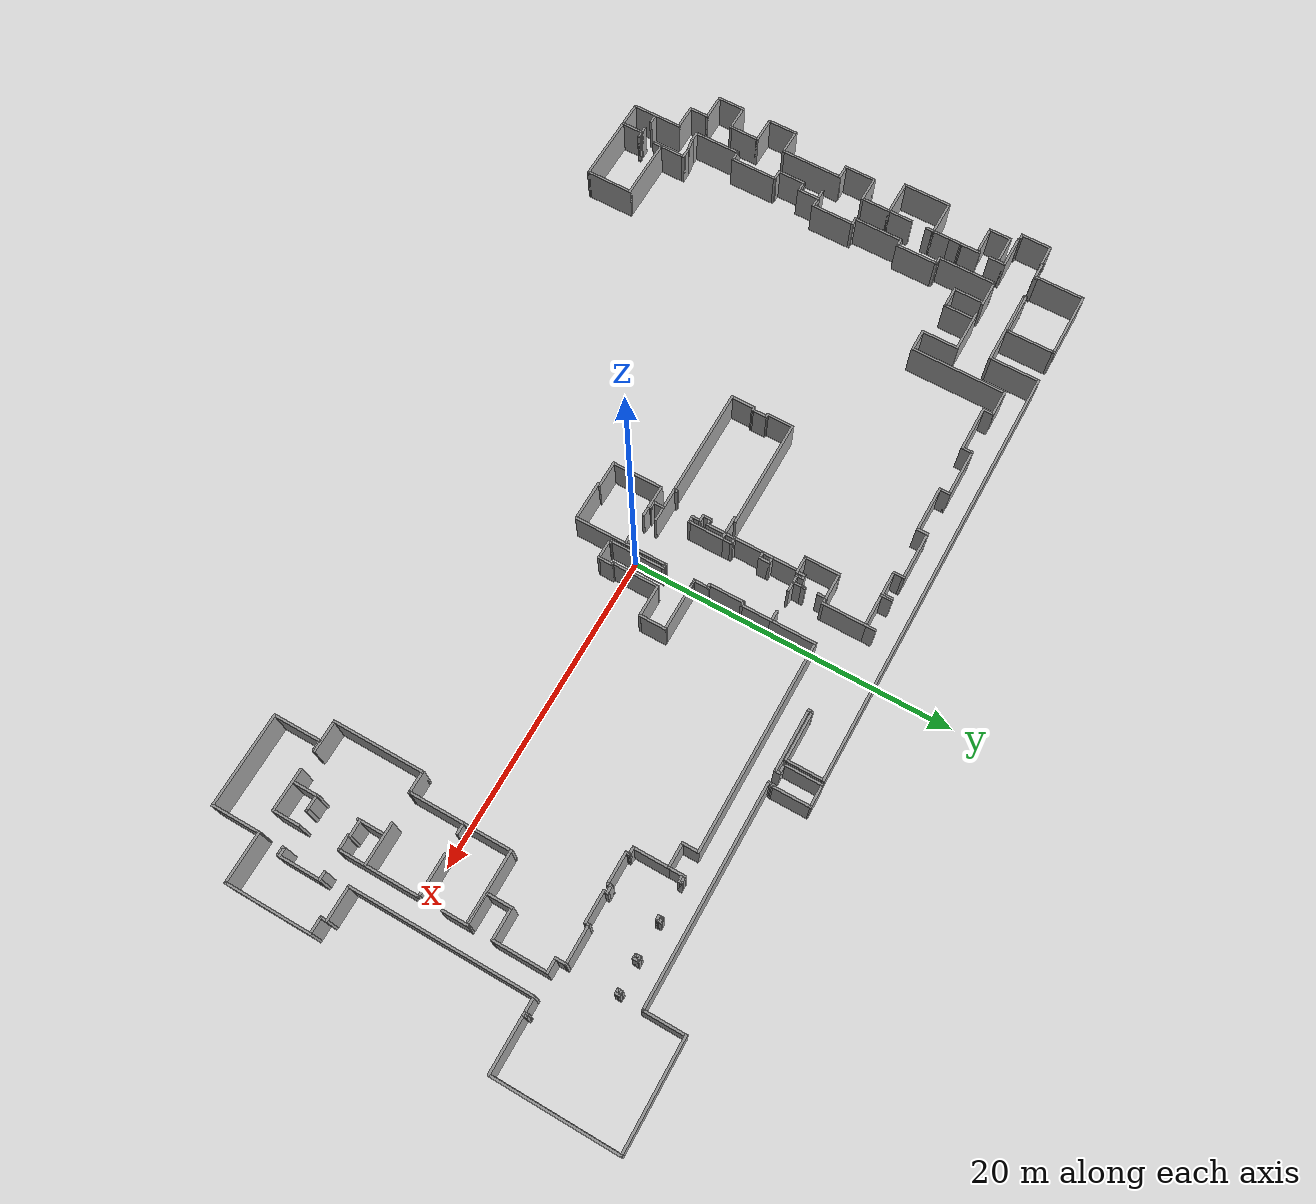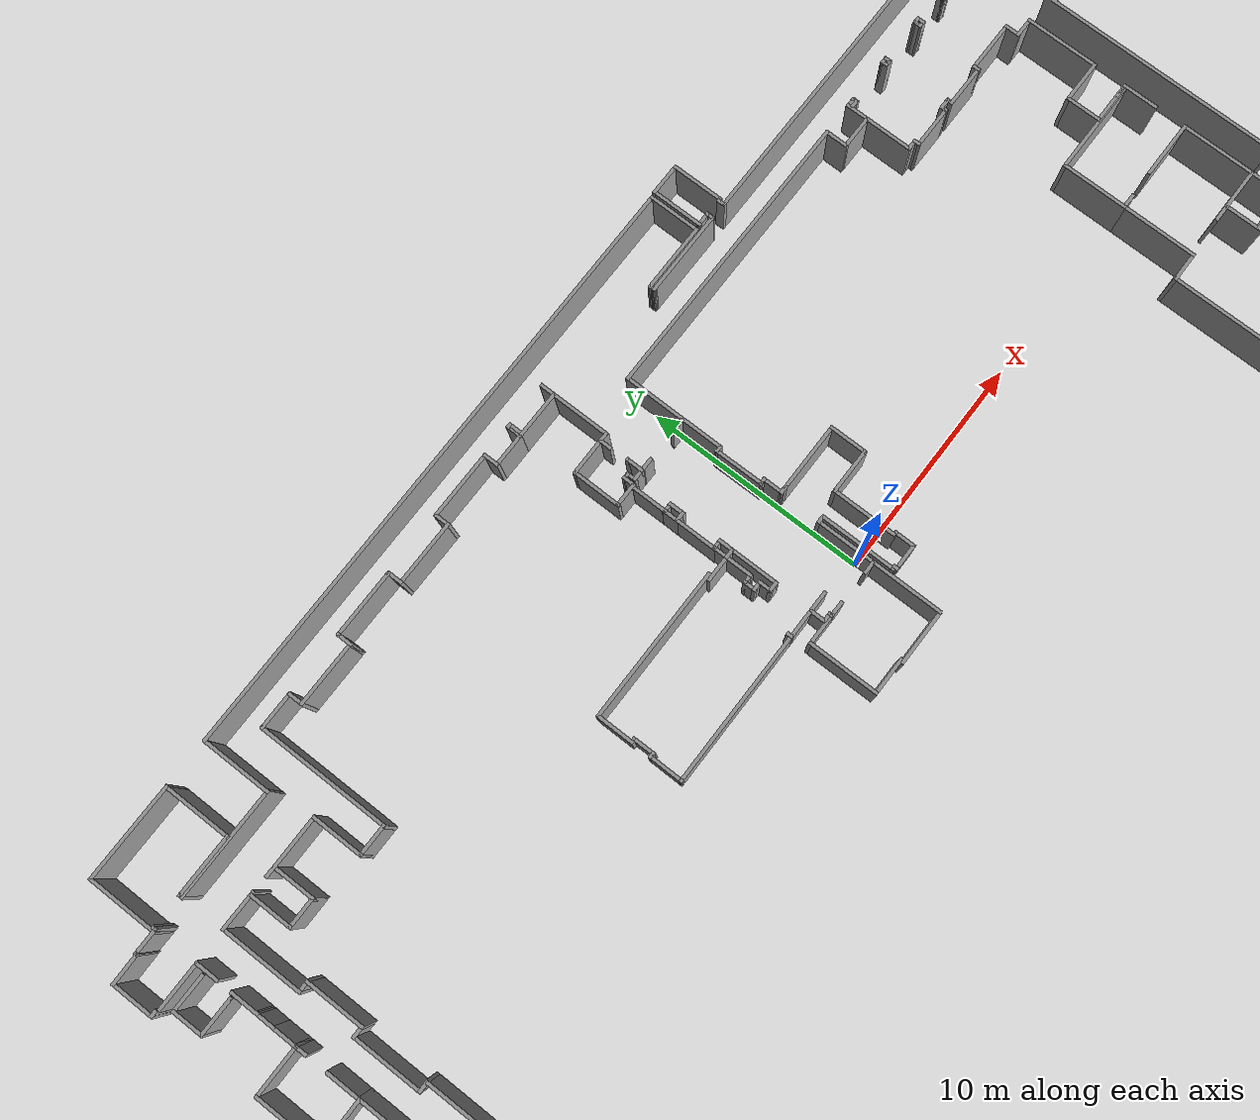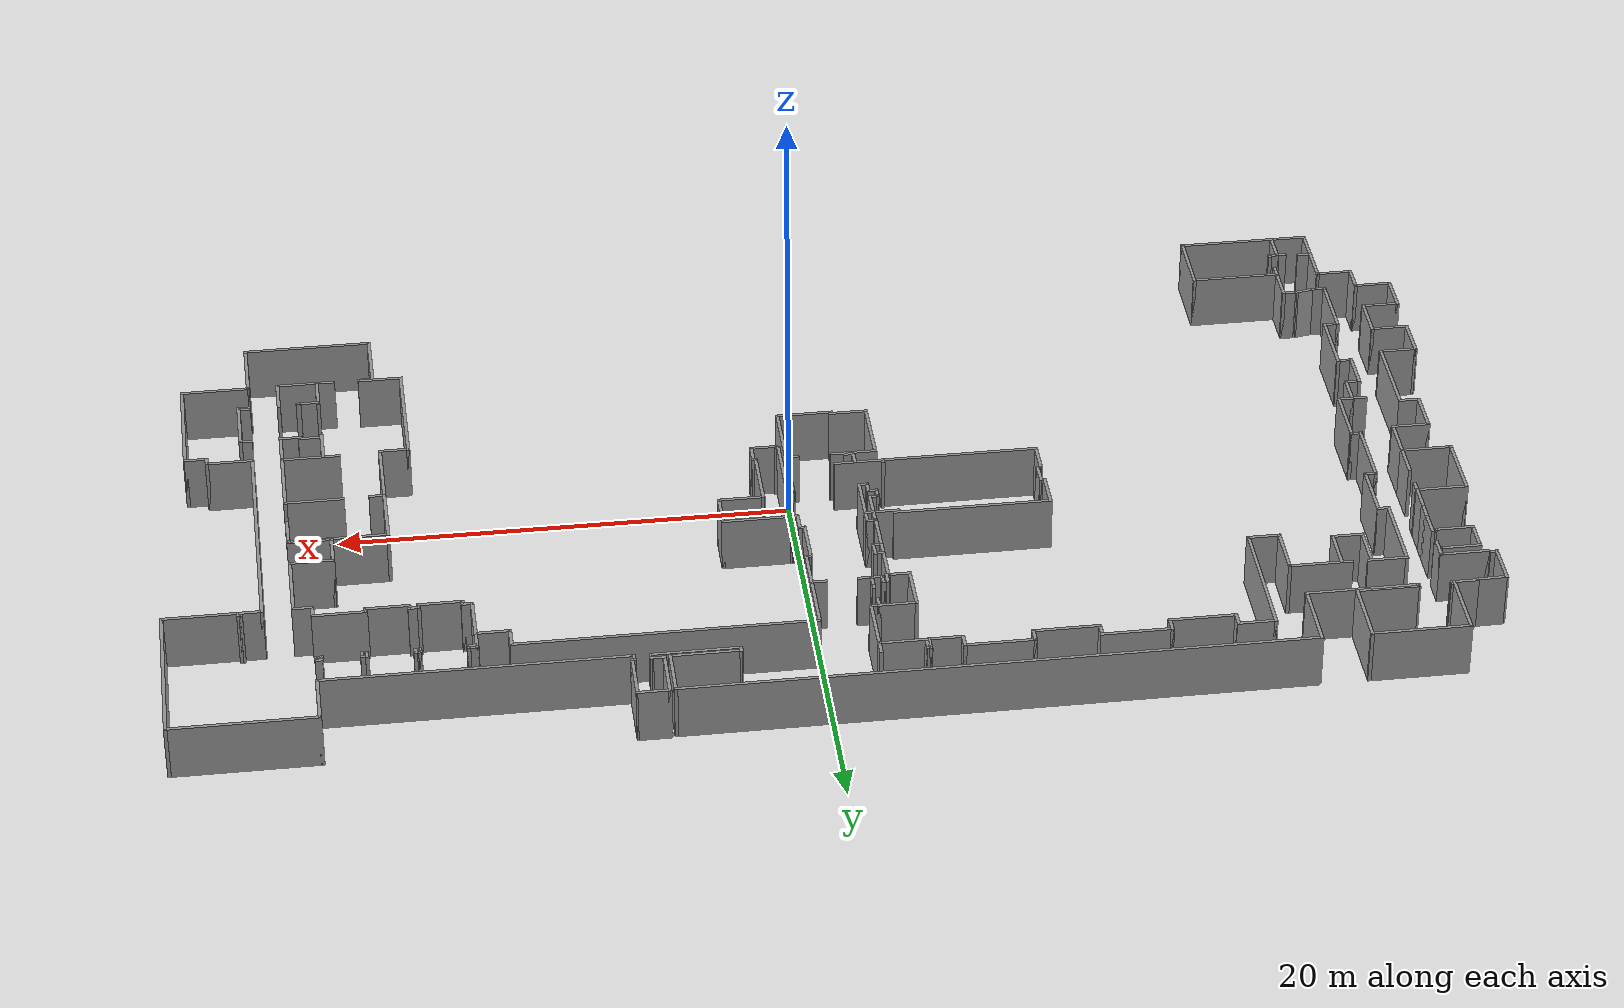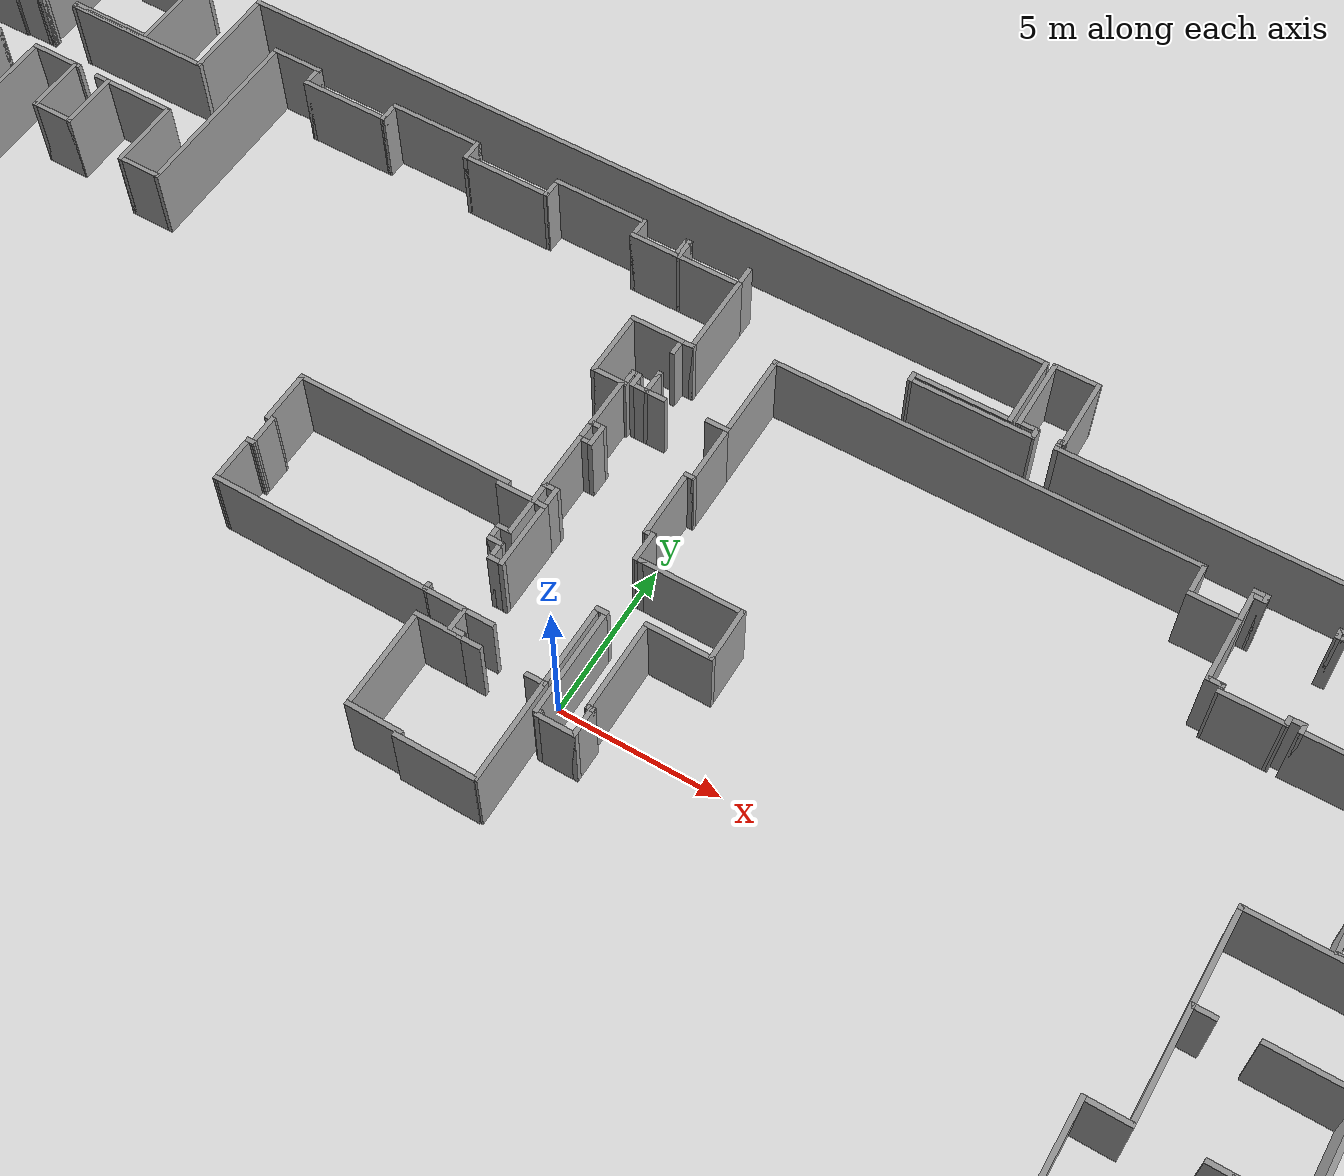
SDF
<?xml version='1.0'?>
<sdf version='1.7'>
  <model name='NursingHome'>
    <pose>-0.88842 0.073115 0 0 -0 0</pose>
    <link name='Wall_100'>
      <collision name='Wall_100_Collision'>
        <geometry>
          <box>
            <size>27.5 0.15 2.5</size>
          </box>
        </geometry>
        <pose>0 0 1.25 0 -0 0</pose>
      </collision>
      <visual name='Wall_100_Visual'>
        <pose>0 0 1.25 0 -0 0</pose>
        <geometry>
          <box>
            <size>27.5 0.15 2.5</size>
          </box>
        </geometry>
        <material>
          <script>
            <uri>file://media/materials/scripts/gazebo.material</uri>
            <name>Gazebo/Grey</name>
          </script>
          <ambient>1 1 1 1</ambient>
        </material>
        <meta>
          <layer>0</layer>
        </meta>
      </visual>
      <pose>-6.18972 15.1854 0 0 -0 3.14159</pose>
    </link>
    <link name='Wall_101'>
      <collision name='Wall_101_Collision'>
        <geometry>
          <box>
            <size>3.25 0.15 2.5</size>
          </box>
        </geometry>
        <pose>0 0 1.25 0 -0 0</pose>
      </collision>
      <visual name='Wall_101_Visual'>
        <pose>0 0 1.25 0 -0 0</pose>
        <geometry>
          <box>
            <size>3.25 0.15 2.5</size>
          </box>
        </geometry>
        <material>
          <script>
            <uri>file://media/materials/scripts/gazebo.material</uri>
            <name>Gazebo/Grey</name>
          </script>
          <ambient>1 1 1 1</ambient>
        </material>
        <meta>
          <layer>0</layer>
        </meta>
      </visual>
      <pose>-19.8647 13.6354 0 0 -0 -1.5708</pose>
    </link>
    <link name='Wall_103'>
      <collision name='Wall_103_Collision'>
        <geometry>
          <box>
            <size>5 0.15 2.5</size>
          </box>
        </geometry>
        <pose>0 0 1.25 0 -0 0</pose>
      </collision>
      <visual name='Wall_103_Visual'>
        <pose>0 0 1.25 0 -0 0</pose>
        <geometry>
          <box>
            <size>5 0.15 2.5</size>
          </box>
        </geometry>
        <material>
          <script>
            <uri>file://media/materials/scripts/gazebo.material</uri>
            <name>Gazebo/Grey</name>
          </script>
          <ambient>1 1 1 1</ambient>
        </material>
        <meta>
          <layer>0</layer>
        </meta>
      </visual>
      <pose>-22.2897 12.0854 0 0 -0 3.14159</pose>
    </link>
    <link name='Wall_105'>
      <collision name='Wall_105_Collision'>
        <geometry>
          <box>
            <size>0.25 0.15 2.5</size>
          </box>
        </geometry>
        <pose>0 0 1.25 0 -0 0</pose>
      </collision>
      <visual name='Wall_105_Visual'>
        <pose>0 0 1.25 0 -0 0</pose>
        <geometry>
          <box>
            <size>0.25 0.15 2.5</size>
          </box>
        </geometry>
        <material>
          <script>
            <uri>file://media/materials/scripts/gazebo.material</uri>
            <name>Gazebo/Grey</name>
          </script>
          <ambient>1 1 1 1</ambient>
        </material>
        <meta>
          <layer>0</layer>
        </meta>
      </visual>
      <pose>-24.7147 12.1354 0 0 -0 1.5708</pose>
    </link>
    <link name='Wall_108'>
      <collision name='Wall_108_Collision'>
        <geometry>
          <box>
            <size>2.75 0.15 2.5</size>
          </box>
        </geometry>
        <pose>0 0 1.25 0 -0 0</pose>
      </collision>
      <visual name='Wall_108_Visual'>
        <pose>0 0 1.25 0 -0 0</pose>
        <geometry>
          <box>
            <size>2.75 0.15 2.5</size>
          </box>
        </geometry>
        <material>
          <script>
            <uri>file://media/materials/scripts/gazebo.material</uri>
            <name>Gazebo/Grey</name>
          </script>
          <ambient>1 1 1 1</ambient>
        </material>
        <meta>
          <layer>0</layer>
        </meta>
      </visual>
      <pose>-23.3314 12.1881 0 0 -0 3.14159</pose>
    </link>
    <link name='Wall_11'>
      <collision name='Wall_11_Collision'>
        <geometry>
          <box>
            <size>0.199602 0.15 2.5</size>
          </box>
        </geometry>
        <pose>0 0 1.25 0 -0 0</pose>
      </collision>
      <visual name='Wall_11_Visual'>
        <pose>0 0 1.25 0 -0 0</pose>
        <geometry>
          <box>
            <size>0.199602 0.15 2.5</size>
          </box>
        </geometry>
        <material>
          <script>
            <uri>file://media/materials/scripts/gazebo.material</uri>
            <name>Gazebo/Grey</name>
          </script>
          <ambient>1 1 1 1</ambient>
        </material>
        <meta>
          <layer>0</layer>
        </meta>
      </visual>
      <pose>24.333 -9.06025 0 0 -0 1.33682</pose>
    </link>
    <link name='Wall_113'>
      <collision name='Wall_113_Collision'>
        <geometry>
          <box>
            <size>3.15 0.15 2.5</size>
          </box>
        </geometry>
        <pose>0 0 1.25 0 -0 0</pose>
      </collision>
      <visual name='Wall_113_Visual'>
        <pose>0 0 1.25 0 -0 0</pose>
        <geometry>
          <box>
            <size>3.15 0.15 2.5</size>
          </box>
        </geometry>
        <material>
          <script>
            <uri>file://media/materials/scripts/gazebo.material</uri>
            <name>Gazebo/Grey</name>
          </script>
          <ambient>1 1 1 1</ambient>
        </material>
        <meta>
          <layer>0</layer>
        </meta>
      </visual>
      <pose>-22.0314 13.6881 0 0 -0 1.5708</pose>
    </link>
    <link name='Wall_115'>
      <collision name='Wall_115_Collision'>
        <geometry>
          <box>
            <size>4.4 0.15 2.5</size>
          </box>
        </geometry>
        <pose>0 0 1.25 0 -0 0</pose>
      </collision>
      <visual name='Wall_115_Visual'>
        <pose>0 0 1.25 0 -0 0</pose>
        <geometry>
          <box>
            <size>4.4 0.15 2.5</size>
          </box>
        </geometry>
        <material>
          <script>
            <uri>file://media/materials/scripts/gazebo.material</uri>
            <name>Gazebo/Grey</name>
          </script>
          <ambient>1 1 1 1</ambient>
        </material>
        <meta>
          <layer>0</layer>
        </meta>
      </visual>
      <pose>-24.1564 15.1881 0 0 -0 3.14159</pose>
    </link>
    <link name='Wall_117'>
      <collision name='Wall_117_Collision'>
        <geometry>
          <box>
            <size>3.25 0.15 2.5</size>
          </box>
        </geometry>
        <pose>0 0 1.25 0 -0 0</pose>
      </collision>
      <visual name='Wall_117_Visual'>
        <pose>0 0 1.25 0 -0 0</pose>
        <geometry>
          <box>
            <size>3.25 0.15 2.5</size>
          </box>
        </geometry>
        <material>
          <script>
            <uri>file://media/materials/scripts/gazebo.material</uri>
            <name>Gazebo/Grey</name>
          </script>
          <ambient>1 1 1 1</ambient>
        </material>
        <meta>
          <layer>0</layer>
        </meta>
      </visual>
      <pose>-26.2814 13.6381 0 0 -0 -1.5708</pose>
    </link>
    <link name='Wall_118'>
      <collision name='Wall_118_Collision'>
        <geometry>
          <box>
            <size>0.25 0.15 2.5</size>
          </box>
        </geometry>
        <pose>0 0 1.25 0 -0 0</pose>
      </collision>
      <visual name='Wall_118_Visual'>
        <pose>0 0 1.25 0 -0 0</pose>
        <geometry>
          <box>
            <size>0.25 0.15 2.5</size>
          </box>
        </geometry>
        <material>
          <script>
            <uri>file://media/materials/scripts/gazebo.material</uri>
            <name>Gazebo/Grey</name>
          </script>
          <ambient>1 1 1 1</ambient>
        </material>
        <meta>
          <layer>0</layer>
        </meta>
      </visual>
      <pose>-26.2314 12.0881 0 0 -0 0</pose>
    </link>
    <link name='Wall_119'>
      <collision name='Wall_119_Collision'>
        <geometry>
          <box>
            <size>0.25 0.15 2.5</size>
          </box>
        </geometry>
        <pose>0 0 1.25 0 -0 0</pose>
      </collision>
      <visual name='Wall_119_Visual'>
        <pose>0 0 1.25 0 -0 0</pose>
        <geometry>
          <box>
            <size>0.25 0.15 2.5</size>
          </box>
        </geometry>
        <material>
          <script>
            <uri>file://media/materials/scripts/gazebo.material</uri>
            <name>Gazebo/Grey</name>
          </script>
          <ambient>1 1 1 1</ambient>
        </material>
        <meta>
          <layer>0</layer>
        </meta>
      </visual>
      <pose>-26.1814 12.1381 0 0 -0 1.5708</pose>
    </link>
    <link name='Wall_12'>
      <collision name='Wall_12_Collision'>
        <geometry>
          <box>
            <size>3.1 0.15 2.5</size>
          </box>
        </geometry>
        <pose>0 0 1.25 0 -0 0</pose>
      </collision>
      <visual name='Wall_12_Visual'>
        <pose>0 0 1.25 0 -0 0</pose>
        <geometry>
          <box>
            <size>3.1 0.15 2.5</size>
          </box>
        </geometry>
        <material>
          <script>
            <uri>file://media/materials/scripts/gazebo.material</uri>
            <name>Gazebo/Grey</name>
          </script>
          <ambient>1 1 1 1</ambient>
        </material>
        <meta>
          <layer>0</layer>
        </meta>
      </visual>
      <pose>25.8138 -9.03613 0 0 -0 0</pose>
    </link>
    <link name='Wall_121'>
      <collision name='Wall_121_Collision'>
        <geometry>
          <box>
            <size>1.25 0.15 2.5</size>
          </box>
        </geometry>
        <pose>0 0 1.25 0 -0 0</pose>
      </collision>
      <visual name='Wall_121_Visual'>
        <pose>0 0 1.25 0 -0 0</pose>
        <geometry>
          <box>
            <size>1.25 0.15 2.5</size>
          </box>
        </geometry>
        <material>
          <script>
            <uri>file://media/materials/scripts/gazebo.material</uri>
            <name>Gazebo/Grey</name>
          </script>
          <ambient>1 1 1 1</ambient>
        </material>
        <meta>
          <layer>0</layer>
        </meta>
      </visual>
      <pose>-26.7314 12.0881 0 0 -0 3.14159</pose>
    </link>
    <link name='Wall_124'>
      <collision name='Wall_124_Collision'>
        <geometry>
          <box>
            <size>0.2 0.15 2.5</size>
          </box>
        </geometry>
        <pose>0 0 1.25 0 -0 0</pose>
      </collision>
      <visual name='Wall_124_Visual'>
        <pose>0 0 1.25 0 -0 0</pose>
        <geometry>
          <box>
            <size>0.2 0.15 2.5</size>
          </box>
        </geometry>
        <material>
          <script>
            <uri>file://media/materials/scripts/gazebo.material</uri>
            <name>Gazebo/Grey</name>
          </script>
          <ambient>1 1 1 1</ambient>
        </material>
        <meta>
          <layer>0</layer>
        </meta>
      </visual>
      <pose>-27.2814 12.0631 0 0 -0 -1.5708</pose>
    </link>
    <link name='Wall_127'>
      <collision name='Wall_127_Collision'>
        <geometry>
          <box>
            <size>1.45645 0.15 2.5</size>
          </box>
        </geometry>
        <pose>0 0 1.25 0 -0 0</pose>
      </collision>
      <visual name='Wall_127_Visual'>
        <pose>0 0 1.25 0 -0 0</pose>
        <geometry>
          <box>
            <size>1.45645 0.15 2.5</size>
          </box>
        </geometry>
        <material>
          <script>
            <uri>file://media/materials/scripts/gazebo.material</uri>
            <name>Gazebo/Grey</name>
          </script>
          <ambient>1 1 1 1</ambient>
        </material>
        <meta>
          <layer>0</layer>
        </meta>
      </visual>
      <pose>-27.9346 12.0294 0 0 -0 0.013298</pose>
    </link>
    <link name='Wall_129'>
      <collision name='Wall_129_Collision'>
        <geometry>
          <box>
            <size>2 0.15 2.5</size>
          </box>
        </geometry>
        <pose>0 0 1.25 0 -0 0</pose>
      </collision>
      <visual name='Wall_129_Visual'>
        <pose>0 0 1.25 0 -0 0</pose>
        <geometry>
          <box>
            <size>2 0.15 2.5</size>
          </box>
        </geometry>
        <material>
          <script>
            <uri>file://media/materials/scripts/gazebo.material</uri>
            <name>Gazebo/Grey</name>
          </script>
          <ambient>1 1 1 1</ambient>
        </material>
        <meta>
          <layer>0</layer>
        </meta>
      </visual>
      <pose>-28.5878 11.0957 0 0 -0 -1.5708</pose>
    </link>
    <link name='Wall_131'>
      <collision name='Wall_131_Collision'>
        <geometry>
          <box>
            <size>0.35 0.15 2.5</size>
          </box>
        </geometry>
        <pose>0 0 1.25 0 -0 0</pose>
      </collision>
      <visual name='Wall_131_Visual'>
        <pose>0 0 1.25 0 -0 0</pose>
        <geometry>
          <box>
            <size>0.35 0.15 2.5</size>
          </box>
        </geometry>
        <material>
          <script>
            <uri>file://media/materials/scripts/gazebo.material</uri>
            <name>Gazebo/Grey</name>
          </script>
          <ambient>1 1 1 1</ambient>
        </material>
        <meta>
          <layer>0</layer>
        </meta>
      </visual>
      <pose>-28.4878 10.1707 0 0 -0 0</pose>
    </link>
    <link name='Wall_137'>
      <collision name='Wall_137_Collision'>
        <geometry>
          <box>
            <size>0.15 0.15 2.5</size>
          </box>
        </geometry>
        <pose>0 0 1.25 0 -0 0</pose>
      </collision>
      <visual name='Wall_137_Visual'>
        <pose>0 0 1.25 0 -0 0</pose>
        <geometry>
          <box>
            <size>0.15 0.15 2.5</size>
          </box>
        </geometry>
        <material>
          <script>
            <uri>file://media/materials/scripts/gazebo.material</uri>
            <name>Gazebo/Grey</name>
          </script>
          <ambient>1 1 1 1</ambient>
        </material>
        <meta>
          <layer>0</layer>
        </meta>
      </visual>
      <pose>-28.2223 10.0904 0 0 -0 0</pose>
    </link>
    <link name='Wall_140'>
      <collision name='Wall_140_Collision'>
        <geometry>
          <box>
            <size>2.2 0.15 2.5</size>
          </box>
        </geometry>
        <pose>0 0 1.25 0 -0 0</pose>
      </collision>
      <visual name='Wall_140_Visual'>
        <pose>0 0 1.25 0 -0 0</pose>
        <geometry>
          <box>
            <size>2.2 0.15 2.5</size>
          </box>
        </geometry>
        <material>
          <script>
            <uri>file://media/materials/scripts/gazebo.material</uri>
            <name>Gazebo/Grey</name>
          </script>
          <ambient>1 1 1 1</ambient>
        </material>
        <meta>
          <layer>0</layer>
        </meta>
      </visual>
      <pose>-27.1973 10.0904 0 0 -0 0</pose>
    </link>
    <link name='Wall_142'>
      <collision name='Wall_142_Collision'>
        <geometry>
          <box>
            <size>1.1 0.15 2.5</size>
          </box>
        </geometry>
        <pose>0 0 1.25 0 -0 0</pose>
      </collision>
      <visual name='Wall_142_Visual'>
        <pose>0 0 1.25 0 -0 0</pose>
        <geometry>
          <box>
            <size>1.1 0.15 2.5</size>
          </box>
        </geometry>
        <material>
          <script>
            <uri>file://media/materials/scripts/gazebo.material</uri>
            <name>Gazebo/Grey</name>
          </script>
          <ambient>1 1 1 1</ambient>
        </material>
        <meta>
          <layer>0</layer>
        </meta>
      </visual>
      <pose>-26.1723 9.61538 0 0 -0 -1.5708</pose>
    </link>
    <link name='Wall_144'>
      <collision name='Wall_144_Collision'>
        <geometry>
          <box>
            <size>1.75 0.15 2.5</size>
          </box>
        </geometry>
        <pose>0 0 1.25 0 -0 0</pose>
      </collision>
      <visual name='Wall_144_Visual'>
        <pose>0 0 1.25 0 -0 0</pose>
        <geometry>
          <box>
            <size>1.75 0.15 2.5</size>
          </box>
        </geometry>
        <material>
          <script>
            <uri>file://media/materials/scripts/gazebo.material</uri>
            <name>Gazebo/Grey</name>
          </script>
          <ambient>1 1 1 1</ambient>
        </material>
        <meta>
          <layer>0</layer>
        </meta>
      </visual>
      <pose>-27.1777 9.64726 0 0 -0 3.14159</pose>
    </link>
    <link name='Wall_145'>
      <collision name='Wall_145_Collision'>
        <geometry>
          <box>
            <size>1.5 0.15 2.5</size>
          </box>
        </geometry>
        <pose>0 0 1.25 0 -0 0</pose>
      </collision>
      <visual name='Wall_145_Visual'>
        <pose>0 0 1.25 0 -0 0</pose>
        <geometry>
          <box>
            <size>1.5 0.15 2.5</size>
          </box>
        </geometry>
        <material>
          <script>
            <uri>file://media/materials/scripts/gazebo.material</uri>
            <name>Gazebo/Grey</name>
          </script>
          <ambient>1 1 1 1</ambient>
        </material>
        <meta>
          <layer>0</layer>
        </meta>
      </visual>
      <pose>-27.9777 8.97226 0 0 -0 -1.5708</pose>
    </link>
    <link name='Wall_146'>
      <collision name='Wall_146_Collision'>
        <geometry>
          <box>
            <size>1.75 0.15 2.5</size>
          </box>
        </geometry>
        <pose>0 0 1.25 0 -0 0</pose>
      </collision>
      <visual name='Wall_146_Visual'>
        <pose>0 0 1.25 0 -0 0</pose>
        <geometry>
          <box>
            <size>1.75 0.15 2.5</size>
          </box>
        </geometry>
        <material>
          <script>
            <uri>file://media/materials/scripts/gazebo.material</uri>
            <name>Gazebo/Grey</name>
          </script>
          <ambient>1 1 1 1</ambient>
        </material>
        <meta>
          <layer>0</layer>
        </meta>
      </visual>
      <pose>-27.1777 8.29726 0 0 -0 0</pose>
    </link>
    <link name='Wall_149'>
      <collision name='Wall_149_Collision'>
        <geometry>
          <box>
            <size>1.35 0.15 2.5</size>
          </box>
        </geometry>
        <pose>0 0 1.25 0 -0 0</pose>
      </collision>
      <visual name='Wall_149_Visual'>
        <pose>0 0 1.25 0 -0 0</pose>
        <geometry>
          <box>
            <size>1.35 0.15 2.5</size>
          </box>
        </geometry>
        <material>
          <script>
            <uri>file://media/materials/scripts/gazebo.material</uri>
            <name>Gazebo/Grey</name>
          </script>
          <ambient>1 1 1 1</ambient>
        </material>
        <meta>
          <layer>0</layer>
        </meta>
      </visual>
      <pose>-26.181 7.79245 0 0 -0 1.5708</pose>
    </link>
    <link name='Wall_151'>
      <collision name='Wall_151_Collision'>
        <geometry>
          <box>
            <size>0.16 0.15 2.5</size>
          </box>
        </geometry>
        <pose>0 0 1.25 0 -0 0</pose>
      </collision>
      <visual name='Wall_151_Visual'>
        <pose>0 0 1.25 0 -0 0</pose>
        <geometry>
          <box>
            <size>0.16 0.15 2.5</size>
          </box>
        </geometry>
        <material>
          <script>
            <uri>file://media/materials/scripts/gazebo.material</uri>
            <name>Gazebo/Grey</name>
          </script>
          <ambient>1 1 1 1</ambient>
        </material>
        <meta>
          <layer>0</layer>
        </meta>
      </visual>
      <pose>-26.3727 8.29726 0 0 -0 0</pose>
    </link>
    <link name='Wall_153'>
      <collision name='Wall_153_Collision'>
        <geometry>
          <box>
            <size>1.25 0.15 2.5</size>
          </box>
        </geometry>
        <pose>0 0 1.25 0 -0 0</pose>
      </collision>
      <visual name='Wall_153_Visual'>
        <pose>0 0 1.25 0 -0 0</pose>
        <geometry>
          <box>
            <size>1.25 0.15 2.5</size>
          </box>
        </geometry>
        <material>
          <script>
            <uri>file://media/materials/scripts/gazebo.material</uri>
            <name>Gazebo/Grey</name>
          </script>
          <ambient>1 1 1 1</ambient>
        </material>
        <meta>
          <layer>0</layer>
        </meta>
      </visual>
      <pose>-26.1947 5.87 0 0 -0 -1.5708</pose>
    </link>
    <link name='Wall_154'>
      <collision name='Wall_154_Collision'>
        <geometry>
          <box>
            <size>2.35 0.15 2.5</size>
          </box>
        </geometry>
        <pose>0 0 1.25 0 -0 0</pose>
      </collision>
      <visual name='Wall_154_Visual'>
        <pose>0 0 1.25 0 -0 0</pose>
        <geometry>
          <box>
            <size>2.35 0.15 2.5</size>
          </box>
        </geometry>
        <material>
          <script>
            <uri>file://media/materials/scripts/gazebo.material</uri>
            <name>Gazebo/Grey</name>
          </script>
          <ambient>1 1 1 1</ambient>
        </material>
        <meta>
          <layer>0</layer>
        </meta>
      </visual>
      <pose>-27.2947 5.32 0 0 -0 3.14159</pose>
    </link>
    <link name='Wall_156'>
      <collision name='Wall_156_Collision'>
        <geometry>
          <box>
            <size>3.15 0.15 2.5</size>
          </box>
        </geometry>
        <pose>0 0 1.25 0 -0 0</pose>
      </collision>
      <visual name='Wall_156_Visual'>
        <pose>0 0 1.25 0 -0 0</pose>
        <geometry>
          <box>
            <size>3.15 0.15 2.5</size>
          </box>
        </geometry>
        <material>
          <script>
            <uri>file://media/materials/scripts/gazebo.material</uri>
            <name>Gazebo/Grey</name>
          </script>
          <ambient>1 1 1 1</ambient>
        </material>
        <meta>
          <layer>0</layer>
        </meta>
      </visual>
      <pose>-28.3947 3.82 0 0 -0 -1.5708</pose>
    </link>
    <link name='Wall_158'>
      <collision name='Wall_158_Collision'>
        <geometry>
          <box>
            <size>2.35 0.15 2.5</size>
          </box>
        </geometry>
        <pose>0 0 1.25 0 -0 0</pose>
      </collision>
      <visual name='Wall_158_Visual'>
        <pose>0 0 1.25 0 -0 0</pose>
        <geometry>
          <box>
            <size>2.35 0.15 2.5</size>
          </box>
        </geometry>
        <material>
          <script>
            <uri>file://media/materials/scripts/gazebo.material</uri>
            <name>Gazebo/Grey</name>
          </script>
          <ambient>1 1 1 1</ambient>
        </material>
        <meta>
          <layer>0</layer>
        </meta>
      </visual>
      <pose>-27.2947 2.32 0 0 -0 0</pose>
    </link>
    <link name='Wall_161'>
      <collision name='Wall_161_Collision'>
        <geometry>
          <box>
            <size>0.6 0.15 2.5</size>
          </box>
        </geometry>
        <pose>0 0 1.25 0 -0 0</pose>
      </collision>
      <visual name='Wall_161_Visual'>
        <pose>0 0 1.25 0 -0 0</pose>
        <geometry>
          <box>
            <size>0.6 0.15 2.5</size>
          </box>
        </geometry>
        <material>
          <script>
            <uri>file://media/materials/scripts/gazebo.material</uri>
            <name>Gazebo/Grey</name>
          </script>
          <ambient>1 1 1 1</ambient>
        </material>
        <meta>
          <layer>0</layer>
        </meta>
      </visual>
      <pose>-26.1947 5.095 0 0 -0 -1.5708</pose>
    </link>
    <link name='Wall_163'>
      <collision name='Wall_163_Collision'>
        <geometry>
          <box>
            <size>1.65 0.15 2.5</size>
          </box>
        </geometry>
        <pose>0 0 1.25 0 -0 0</pose>
      </collision>
      <visual name='Wall_163_Visual'>
        <pose>0 0 1.25 0 -0 0</pose>
        <geometry>
          <box>
            <size>1.65 0.15 2.5</size>
          </box>
        </geometry>
        <material>
          <script>
            <uri>file://media/materials/scripts/gazebo.material</uri>
            <name>Gazebo/Grey</name>
          </script>
          <ambient>1 1 1 1</ambient>
        </material>
        <meta>
          <layer>0</layer>
        </meta>
      </visual>
      <pose>-26.1947 3.07 0 0 -0 1.5708</pose>
    </link>
    <link name='Wall_167'>
      <collision name='Wall_167_Collision'>
        <geometry>
          <box>
            <size>0.922568 0.15 2.5</size>
          </box>
        </geometry>
        <pose>0 0 1.25 0 -0 0</pose>
      </collision>
      <visual name='Wall_167_Visual'>
        <pose>0 0 1.25 0 -0 0</pose>
        <geometry>
          <box>
            <size>0.922568 0.15 2.5</size>
          </box>
        </geometry>
        <material>
          <script>
            <uri>file://media/materials/scripts/gazebo.material</uri>
            <name>Gazebo/Grey</name>
          </script>
          <ambient>1 1 1 1</ambient>
        </material>
        <meta>
          <layer>0</layer>
        </meta>
      </visual>
      <pose>-26.1879 6.80622 0 0 -0 1.55301</pose>
    </link>
    <link name='Wall_169'>
      <collision name='Wall_169_Collision'>
        <geometry>
          <box>
            <size>2 0.15 2.5</size>
          </box>
        </geometry>
        <pose>0 0 1.25 0 -0 0</pose>
      </collision>
      <visual name='Wall_169_Visual'>
        <pose>0 0 1.25 0 -0 0</pose>
        <geometry>
          <box>
            <size>2 0.15 2.5</size>
          </box>
        </geometry>
        <material>
          <script>
            <uri>file://media/materials/scripts/gazebo.material</uri>
            <name>Gazebo/Grey</name>
          </script>
          <ambient>1 1 1 1</ambient>
        </material>
        <meta>
          <layer>0</layer>
        </meta>
      </visual>
      <pose>-26.1947 1.395 0 0 -0 -1.5708</pose>
    </link>
    <link name='Wall_17'>
      <collision name='Wall_17_Collision'>
        <geometry>
          <box>
            <size>5.4 0.15 2.5</size>
          </box>
        </geometry>
        <pose>0 0 1.25 0 -0 0</pose>
      </collision>
      <visual name='Wall_17_Visual'>
        <pose>0 0 1.25 0 -0 0</pose>
        <geometry>
          <box>
            <size>5.4 0.15 2.5</size>
          </box>
        </geometry>
        <material>
          <script>
            <uri>file://media/materials/scripts/gazebo.material</uri>
            <name>Gazebo/Grey</name>
          </script>
          <ambient>1 1 1 1</ambient>
        </material>
        <meta>
          <layer>0</layer>
        </meta>
      </visual>
      <pose>27.2888 -6.41113 0 0 -0 1.5708</pose>
    </link>
    <link name='Wall_170'>
      <collision name='Wall_170_Collision'>
        <geometry>
          <box>
            <size>1.75 0.15 2.5</size>
          </box>
        </geometry>
        <pose>0 0 1.25 0 -0 0</pose>
      </collision>
      <visual name='Wall_170_Visual'>
        <pose>0 0 1.25 0 -0 0</pose>
        <geometry>
          <box>
            <size>1.75 0.15 2.5</size>
          </box>
        </geometry>
        <material>
          <script>
            <uri>file://media/materials/scripts/gazebo.material</uri>
            <name>Gazebo/Grey</name>
          </script>
          <ambient>1 1 1 1</ambient>
        </material>
        <meta>
          <layer>0</layer>
        </meta>
      </visual>
      <pose>-26.9947 0.47 0 0 -0 3.14159</pose>
    </link>
    <link name='Wall_171'>
      <collision name='Wall_171_Collision'>
        <geometry>
          <box>
            <size>2.1 0.15 2.5</size>
          </box>
        </geometry>
        <pose>0 0 1.25 0 -0 0</pose>
      </collision>
      <visual name='Wall_171_Visual'>
        <pose>0 0 1.25 0 -0 0</pose>
        <geometry>
          <box>
            <size>2.1 0.15 2.5</size>
          </box>
        </geometry>
        <material>
          <script>
            <uri>file://media/materials/scripts/gazebo.material</uri>
            <name>Gazebo/Grey</name>
          </script>
          <ambient>1 1 1 1</ambient>
        </material>
        <meta>
          <layer>0</layer>
        </meta>
      </visual>
      <pose>-27.7947 -0.505 0 0 -0 -1.5708</pose>
    </link>
    <link name='Wall_173'>
      <collision name='Wall_173_Collision'>
        <geometry>
          <box>
            <size>1 0.15 2.5</size>
          </box>
        </geometry>
        <pose>0 0 1.25 0 -0 0</pose>
      </collision>
      <visual name='Wall_173_Visual'>
        <pose>0 0 1.25 0 -0 0</pose>
        <geometry>
          <box>
            <size>1 0.15 2.5</size>
          </box>
        </geometry>
        <material>
          <script>
            <uri>file://media/materials/scripts/gazebo.material</uri>
            <name>Gazebo/Grey</name>
          </script>
          <ambient>1 1 1 1</ambient>
        </material>
        <meta>
          <layer>0</layer>
        </meta>
      </visual>
      <pose>-27.3697 -1.48 0 0 -0 0</pose>
    </link>
    <link name='Wall_175'>
      <collision name='Wall_175_Collision'>
        <geometry>
          <box>
            <size>4.1 0.15 2.5</size>
          </box>
        </geometry>
        <pose>0 0 1.25 0 -0 0</pose>
      </collision>
      <visual name='Wall_175_Visual'>
        <pose>0 0 1.25 0 -0 0</pose>
        <geometry>
          <box>
            <size>4.1 0.15 2.5</size>
          </box>
        </geometry>
        <material>
          <script>
            <uri>file://media/materials/scripts/gazebo.material</uri>
            <name>Gazebo/Grey</name>
          </script>
          <ambient>1 1 1 1</ambient>
        </material>
        <meta>
          <layer>0</layer>
        </meta>
      </visual>
      <pose>-26.9447 -3.455 0 0 -0 -1.5708</pose>
    </link>
    <link name='Wall_177'>
      <collision name='Wall_177_Collision'>
        <geometry>
          <box>
            <size>1.75 0.15 2.5</size>
          </box>
        </geometry>
        <pose>0 0 1.25 0 -0 0</pose>
      </collision>
      <visual name='Wall_177_Visual'>
        <pose>0 0 1.25 0 -0 0</pose>
        <geometry>
          <box>
            <size>1.75 0.15 2.5</size>
          </box>
        </geometry>
        <material>
          <script>
            <uri>file://media/materials/scripts/gazebo.material</uri>
            <name>Gazebo/Grey</name>
          </script>
          <ambient>1 1 1 1</ambient>
        </material>
        <meta>
          <layer>0</layer>
        </meta>
      </visual>
      <pose>-27.7447 -5.43 0 0 -0 3.14159</pose>
    </link>
    <link name='Wall_179'>
      <collision name='Wall_179_Collision'>
        <geometry>
          <box>
            <size>2 0.15 2.5</size>
          </box>
        </geometry>
        <pose>0 0 1.25 0 -0 0</pose>
      </collision>
      <visual name='Wall_179_Visual'>
        <pose>0 0 1.25 0 -0 0</pose>
        <geometry>
          <box>
            <size>2 0.15 2.5</size>
          </box>
        </geometry>
        <material>
          <script>
            <uri>file://media/materials/scripts/gazebo.material</uri>
            <name>Gazebo/Grey</name>
          </script>
          <ambient>1 1 1 1</ambient>
        </material>
        <meta>
          <layer>0</layer>
        </meta>
      </visual>
      <pose>-28.5447 -6.355 0 0 -0 -1.5708</pose>
    </link>
    <link name='Wall_180'>
      <collision name='Wall_180_Collision'>
        <geometry>
          <box>
            <size>1.75 0.15 2.5</size>
          </box>
        </geometry>
        <pose>0 0 1.25 0 -0 0</pose>
      </collision>
      <visual name='Wall_180_Visual'>
        <pose>0 0 1.25 0 -0 0</pose>
        <geometry>
          <box>
            <size>1.75 0.15 2.5</size>
          </box>
        </geometry>
        <material>
          <script>
            <uri>file://media/materials/scripts/gazebo.material</uri>
            <name>Gazebo/Grey</name>
          </script>
          <ambient>1 1 1 1</ambient>
        </material>
        <meta>
          <layer>0</layer>
        </meta>
      </visual>
      <pose>-27.7447 -7.28 0 0 -0 0</pose>
    </link>
    <link name='Wall_183'>
      <collision name='Wall_183_Collision'>
        <geometry>
          <box>
            <size>2.05 0.15 2.5</size>
          </box>
        </geometry>
        <pose>0 0 1.25 0 -0 0</pose>
      </collision>
      <visual name='Wall_183_Visual'>
        <pose>0 0 1.25 0 -0 0</pose>
        <geometry>
          <box>
            <size>2.05 0.15 2.5</size>
          </box>
        </geometry>
        <material>
          <script>
            <uri>file://media/materials/scripts/gazebo.material</uri>
            <name>Gazebo/Grey</name>
          </script>
          <ambient>1 1 1 1</ambient>
        </material>
        <meta>
          <layer>0</layer>
        </meta>
      </visual>
      <pose>-26.9447 -8.23 0 0 -0 -1.5708</pose>
    </link>
    <link name='Wall_185'>
      <collision name='Wall_185_Collision'>
        <geometry>
          <box>
            <size>1.75 0.15 2.5</size>
          </box>
        </geometry>
        <pose>0 0 1.25 0 -0 0</pose>
      </collision>
      <visual name='Wall_185_Visual'>
        <pose>0 0 1.25 0 -0 0</pose>
        <geometry>
          <box>
            <size>1.75 0.15 2.5</size>
          </box>
        </geometry>
        <material>
          <script>
            <uri>file://media/materials/scripts/gazebo.material</uri>
            <name>Gazebo/Grey</name>
          </script>
          <ambient>1 1 1 1</ambient>
        </material>
        <meta>
          <layer>0</layer>
        </meta>
      </visual>
      <pose>-27.7447 -9.18 0 0 -0 3.14159</pose>
    </link>
    <link name='Wall_186'>
      <collision name='Wall_186_Collision'>
        <geometry>
          <box>
            <size>1.85 0.15 2.5</size>
          </box>
        </geometry>
        <pose>0 0 1.25 0 -0 0</pose>
      </collision>
      <visual name='Wall_186_Visual'>
        <pose>0 0 1.25 0 -0 0</pose>
        <geometry>
          <box>
            <size>1.85 0.15 2.5</size>
          </box>
        </geometry>
        <material>
          <script>
            <uri>file://media/materials/scripts/gazebo.material</uri>
            <name>Gazebo/Grey</name>
          </script>
          <ambient>1 1 1 1</ambient>
        </material>
        <meta>
          <layer>0</layer>
        </meta>
      </visual>
      <pose>-28.5447 -10.03 0 0 -0 -1.5708</pose>
    </link>
    <link name='Wall_188'>
      <collision name='Wall_188_Collision'>
        <geometry>
          <box>
            <size>1.75 0.15 2.5</size>
          </box>
        </geometry>
        <pose>0 0 1.25 0 -0 0</pose>
      </collision>
      <visual name='Wall_188_Visual'>
        <pose>0 0 1.25 0 -0 0</pose>
        <geometry>
          <box>
            <size>1.75 0.15 2.5</size>
          </box>
        </geometry>
        <material>
          <script>
            <uri>file://media/materials/scripts/gazebo.material</uri>
            <name>Gazebo/Grey</name>
          </script>
          <ambient>1 1 1 1</ambient>
        </material>
        <meta>
          <layer>0</layer>
        </meta>
      </visual>
      <pose>-27.7447 -10.88 0 0 -0 0</pose>
    </link>
    <link name='Wall_19'>
      <collision name='Wall_19_Collision'>
        <geometry>
          <box>
            <size>1.1 0.15 2.5</size>
          </box>
        </geometry>
        <pose>0 0 1.25 0 -0 0</pose>
      </collision>
      <visual name='Wall_19_Visual'>
        <pose>0 0 1.25 0 -0 0</pose>
        <geometry>
          <box>
            <size>1.1 0.15 2.5</size>
          </box>
        </geometry>
        <material>
          <script>
            <uri>file://media/materials/scripts/gazebo.material</uri>
            <name>Gazebo/Grey</name>
          </script>
          <ambient>1 1 1 1</ambient>
        </material>
        <meta>
          <layer>0</layer>
        </meta>
      </visual>
      <pose>26.8138 -3.78613 0 0 -0 3.14159</pose>
    </link>
    <link name='Wall_190'>
      <collision name='Wall_190_Collision'>
        <geometry>
          <box>
            <size>1.35 0.15 2.5</size>
          </box>
        </geometry>
        <pose>0 0 1.25 0 -0 0</pose>
      </collision>
      <visual name='Wall_190_Visual'>
        <pose>0 0 1.25 0 -0 0</pose>
        <geometry>
          <box>
            <size>1.35 0.15 2.5</size>
          </box>
        </geometry>
        <material>
          <script>
            <uri>file://media/materials/scripts/gazebo.material</uri>
            <name>Gazebo/Grey</name>
          </script>
          <ambient>1 1 1 1</ambient>
        </material>
        <meta>
          <layer>0</layer>
        </meta>
      </visual>
      <pose>-26.9447 -11.48 0 0 -0 -1.5708</pose>
    </link>
    <link name='Wall_192'>
      <collision name='Wall_192_Collision'>
        <geometry>
          <box>
            <size>1.7 0.15 2.5</size>
          </box>
        </geometry>
        <pose>0 0 1.25 0 -0 0</pose>
      </collision>
      <visual name='Wall_192_Visual'>
        <pose>0 0 1.25 0 -0 0</pose>
        <geometry>
          <box>
            <size>1.7 0.15 2.5</size>
          </box>
        </geometry>
        <material>
          <script>
            <uri>file://media/materials/scripts/gazebo.material</uri>
            <name>Gazebo/Grey</name>
          </script>
          <ambient>1 1 1 1</ambient>
        </material>
        <meta>
          <layer>0</layer>
        </meta>
      </visual>
      <pose>-26.1697 -12.08 0 0 -0 0</pose>
    </link>
    <link name='Wall_195'>
      <collision name='Wall_195_Collision'>
        <geometry>
          <box>
            <size>3.3 0.15 2.5</size>
          </box>
        </geometry>
        <pose>0 0 1.25 0 -0 0</pose>
      </collision>
      <visual name='Wall_195_Visual'>
        <pose>0 0 1.25 0 -0 0</pose>
        <geometry>
          <box>
            <size>3.3 0.15 2.5</size>
          </box>
        </geometry>
        <material>
          <script>
            <uri>file://media/materials/scripts/gazebo.material</uri>
            <name>Gazebo/Grey</name>
          </script>
          <ambient>1 1 1 1</ambient>
        </material>
        <meta>
          <layer>0</layer>
        </meta>
      </visual>
      <pose>-25.3947 -13.655 0 0 -0 -1.5708</pose>
    </link>
    <link name='Wall_197'>
      <collision name='Wall_197_Collision'>
        <geometry>
          <box>
            <size>0.65 0.15 2.5</size>
          </box>
        </geometry>
        <pose>0 0 1.25 0 -0 0</pose>
      </collision>
      <visual name='Wall_197_Visual'>
        <pose>0 0 1.25 0 -0 0</pose>
        <geometry>
          <box>
            <size>0.65 0.15 2.5</size>
          </box>
        </geometry>
        <material>
          <script>
            <uri>file://media/materials/scripts/gazebo.material</uri>
            <name>Gazebo/Grey</name>
          </script>
          <ambient>1 1 1 1</ambient>
        </material>
        <meta>
          <layer>0</layer>
        </meta>
      </visual>
      <pose>-25.1037 -13.7746 0 0 -0 0</pose>
    </link>
    <link name='Wall_199'>
      <collision name='Wall_199_Collision'>
        <geometry>
          <box>
            <size>1.7 0.15 2.5</size>
          </box>
        </geometry>
        <pose>0 0 1.25 0 -0 0</pose>
      </collision>
      <visual name='Wall_199_Visual'>
        <pose>0 0 1.25 0 -0 0</pose>
        <geometry>
          <box>
            <size>1.7 0.15 2.5</size>
          </box>
        </geometry>
        <material>
          <script>
            <uri>file://media/materials/scripts/gazebo.material</uri>
            <name>Gazebo/Grey</name>
          </script>
          <ambient>1 1 1 1</ambient>
        </material>
        <meta>
          <layer>0</layer>
        </meta>
      </visual>
      <pose>-24.6197 -15.23 0 0 -0 0</pose>
    </link>
    <link name='Wall_201'>
      <collision name='Wall_201_Collision'>
        <geometry>
          <box>
            <size>1.5 0.15 2.5</size>
          </box>
        </geometry>
        <pose>0 0 1.25 0 -0 0</pose>
      </collision>
      <visual name='Wall_201_Visual'>
        <pose>0 0 1.25 0 -0 0</pose>
        <geometry>
          <box>
            <size>1.5 0.15 2.5</size>
          </box>
        </geometry>
        <material>
          <script>
            <uri>file://media/materials/scripts/gazebo.material</uri>
            <name>Gazebo/Grey</name>
          </script>
          <ambient>1 1 1 1</ambient>
        </material>
        <meta>
          <layer>0</layer>
        </meta>
      </visual>
      <pose>-23.8447 -14.555 0 0 -0 1.5708</pose>
    </link>
    <link name='Wall_202'>
      <collision name='Wall_202_Collision'>
        <geometry>
          <box>
            <size>0.5 0.15 2.5</size>
          </box>
        </geometry>
        <pose>0 0 1.25 0 -0 0</pose>
      </collision>
      <visual name='Wall_202_Visual'>
        <pose>0 0 1.25 0 -0 0</pose>
        <geometry>
          <box>
            <size>0.5 0.15 2.5</size>
          </box>
        </geometry>
        <material>
          <script>
            <uri>file://media/materials/scripts/gazebo.material</uri>
            <name>Gazebo/Grey</name>
          </script>
          <ambient>1 1 1 1</ambient>
        </material>
        <meta>
          <layer>0</layer>
        </meta>
      </visual>
      <pose>-24.0197 -13.88 0 0 -0 3.14159</pose>
    </link>
    <link name='Wall_204'>
      <collision name='Wall_204_Collision'>
        <geometry>
          <box>
            <size>0.5 0.15 2.5</size>
          </box>
        </geometry>
        <pose>0 0 1.25 0 -0 0</pose>
      </collision>
      <visual name='Wall_204_Visual'>
        <pose>0 0 1.25 0 -0 0</pose>
        <geometry>
          <box>
            <size>0.5 0.15 2.5</size>
          </box>
        </geometry>
        <material>
          <script>
            <uri>file://media/materials/scripts/gazebo.material</uri>
            <name>Gazebo/Grey</name>
          </script>
          <ambient>1 1 1 1</ambient>
        </material>
        <meta>
          <layer>0</layer>
        </meta>
      </visual>
      <pose>-23.6697 -13.88 0 0 -0 0</pose>
    </link>
    <link name='Wall_205'>
      <collision name='Wall_205_Collision'>
        <geometry>
          <box>
            <size>0.2 0.15 2.5</size>
          </box>
        </geometry>
        <pose>0 0 1.25 0 -0 0</pose>
      </collision>
      <visual name='Wall_205_Visual'>
        <pose>0 0 1.25 0 -0 0</pose>
        <geometry>
          <box>
            <size>0.2 0.15 2.5</size>
          </box>
        </geometry>
        <material>
          <script>
            <uri>file://media/materials/scripts/gazebo.material</uri>
            <name>Gazebo/Grey</name>
          </script>
          <ambient>1 1 1 1</ambient>
        </material>
        <meta>
          <layer>0</layer>
        </meta>
      </visual>
      <pose>-23.4947 -13.855 0 0 -0 1.5708</pose>
    </link>
    <link name='Wall_208'>
      <collision name='Wall_208_Collision'>
        <geometry>
          <box>
            <size>0.65 0.15 2.5</size>
          </box>
        </geometry>
        <pose>0 0 1.25 0 -0 0</pose>
      </collision>
      <visual name='Wall_208_Visual'>
        <pose>0 0 1.25 0 -0 0</pose>
        <geometry>
          <box>
            <size>0.65 0.15 2.5</size>
          </box>
        </geometry>
        <material>
          <script>
            <uri>file://media/materials/scripts/gazebo.material</uri>
            <name>Gazebo/Grey</name>
          </script>
          <ambient>1 1 1 1</ambient>
        </material>
        <meta>
          <layer>0</layer>
        </meta>
      </visual>
      <pose>-23.5128 -12.5376 0 0 -0 1.5708</pose>
    </link>
    <link name='Wall_21'>
      <collision name='Wall_21_Collision'>
        <geometry>
          <box>
            <size>0.5115 0.15 2.5</size>
          </box>
        </geometry>
        <pose>0 0 1.25 0 -0 0</pose>
      </collision>
      <visual name='Wall_21_Visual'>
        <pose>0 0 1.25 0 -0 0</pose>
        <geometry>
          <box>
            <size>0.5115 0.15 2.5</size>
          </box>
        </geometry>
        <material>
          <script>
            <uri>file://media/materials/scripts/gazebo.material</uri>
            <name>Gazebo/Grey</name>
          </script>
          <ambient>1 1 1 1</ambient>
        </material>
        <meta>
          <layer>0</layer>
        </meta>
      </visual>
      <pose>26.3388 -3.60538 0 0 -0 1.5708</pose>
    </link>
    <link name='Wall_210'>
      <collision name='Wall_210_Collision'>
        <geometry>
          <box>
            <size>4.05 0.15 2.5</size>
          </box>
        </geometry>
        <pose>0 0 1.25 0 -0 0</pose>
      </collision>
      <visual name='Wall_210_Visual'>
        <pose>0 0 1.25 0 -0 0</pose>
        <geometry>
          <box>
            <size>4.05 0.15 2.5</size>
          </box>
        </geometry>
        <material>
          <script>
            <uri>file://media/materials/scripts/gazebo.material</uri>
            <name>Gazebo/Grey</name>
          </script>
          <ambient>1 1 1 1</ambient>
        </material>
        <meta>
          <layer>0</layer>
        </meta>
      </visual>
      <pose>-21.5628 -12.2876 0 0 -0 0</pose>
    </link>
    <link name='Wall_213'>
      <collision name='Wall_213_Collision'>
        <geometry>
          <box>
            <size>3.1 0.15 2.5</size>
          </box>
        </geometry>
        <pose>0 0 1.25 0 -0 0</pose>
      </collision>
      <visual name='Wall_213_Visual'>
        <pose>0 0 1.25 0 -0 0</pose>
        <geometry>
          <box>
            <size>3.1 0.15 2.5</size>
          </box>
        </geometry>
        <material>
          <script>
            <uri>file://media/materials/scripts/gazebo.material</uri>
            <name>Gazebo/Grey</name>
          </script>
          <ambient>1 1 1 1</ambient>
        </material>
        <meta>
          <layer>0</layer>
        </meta>
      </visual>
      <pose>-19.6128 -13.7626 0 0 -0 -1.5708</pose>
    </link>
    <link name='Wall_215'>
      <collision name='Wall_215_Collision'>
        <geometry>
          <box>
            <size>4.38192 0.15 2.5</size>
          </box>
        </geometry>
        <pose>0 0 1.25 0 -0 0</pose>
      </collision>
      <visual name='Wall_215_Visual'>
        <pose>0 0 1.25 0 -0 0</pose>
        <geometry>
          <box>
            <size>4.38192 0.15 2.5</size>
          </box>
        </geometry>
        <material>
          <script>
            <uri>file://media/materials/scripts/gazebo.material</uri>
            <name>Gazebo/Grey</name>
          </script>
          <ambient>1 1 1 1</ambient>
        </material>
        <meta>
          <layer>0</layer>
        </meta>
      </visual>
      <pose>-21.7288 -15.2338 0 0 -0 3.13979</pose>
    </link>
    <link name='Wall_218'>
      <collision name='Wall_218_Collision'>
        <geometry>
          <box>
            <size>1.75 0.15 2.5</size>
          </box>
        </geometry>
        <pose>0 0 1.25 0 -0 0</pose>
      </collision>
      <visual name='Wall_218_Visual'>
        <pose>0 0 1.25 0 -0 0</pose>
        <geometry>
          <box>
            <size>1.75 0.15 2.5</size>
          </box>
        </geometry>
        <material>
          <script>
            <uri>file://media/materials/scripts/gazebo.material</uri>
            <name>Gazebo/Grey</name>
          </script>
          <ambient>1 1 1 1</ambient>
        </material>
        <meta>
          <layer>0</layer>
        </meta>
      </visual>
      <pose>-23.5128 -11.4876 0 0 -0 1.5708</pose>
    </link>
    <link name='Wall_22'>
      <collision name='Wall_22_Collision'>
        <geometry>
          <box>
            <size>2.15 0.15 2.5</size>
          </box>
        </geometry>
        <pose>0 0 1.25 0 -0 0</pose>
      </collision>
      <visual name='Wall_22_Visual'>
        <pose>0 0 1.25 0 -0 0</pose>
        <geometry>
          <box>
            <size>2.15 0.15 2.5</size>
          </box>
        </geometry>
        <material>
          <script>
            <uri>file://media/materials/scripts/gazebo.material</uri>
            <name>Gazebo/Grey</name>
          </script>
          <ambient>1 1 1 1</ambient>
        </material>
        <meta>
          <layer>0</layer>
        </meta>
      </visual>
      <pose>25.3388 -3.42463 0 0 -0 3.14159</pose>
    </link>
    <link name='Wall_220'>
      <collision name='Wall_220_Collision'>
        <geometry>
          <box>
            <size>0.75 0.15 2.5</size>
          </box>
        </geometry>
        <pose>0 0 1.25 0 -0 0</pose>
      </collision>
      <visual name='Wall_220_Visual'>
        <pose>0 0 1.25 0 -0 0</pose>
        <geometry>
          <box>
            <size>0.75 0.15 2.5</size>
          </box>
        </geometry>
        <material>
          <script>
            <uri>file://media/materials/scripts/gazebo.material</uri>
            <name>Gazebo/Grey</name>
          </script>
          <ambient>1 1 1 1</ambient>
        </material>
        <meta>
          <layer>0</layer>
        </meta>
      </visual>
      <pose>-23.8128 -10.6876 0 0 -0 3.14159</pose>
    </link>
    <link name='Wall_222'>
      <collision name='Wall_222_Collision'>
        <geometry>
          <box>
            <size>0.7 0.15 2.5</size>
          </box>
        </geometry>
        <pose>0 0 1.25 0 -0 0</pose>
      </collision>
      <visual name='Wall_222_Visual'>
        <pose>0 0 1.25 0 -0 0</pose>
        <geometry>
          <box>
            <size>0.7 0.15 2.5</size>
          </box>
        </geometry>
        <material>
          <script>
            <uri>file://media/materials/scripts/gazebo.material</uri>
            <name>Gazebo/Grey</name>
          </script>
          <ambient>1 1 1 1</ambient>
        </material>
        <meta>
          <layer>0</layer>
        </meta>
      </visual>
      <pose>-25.1789 -10.8318 0 0 -0 3.14159</pose>
    </link>
    <link name='Wall_224'>
      <collision name='Wall_224_Collision'>
        <geometry>
          <box>
            <size>0.954078 0.15 2.5</size>
          </box>
        </geometry>
        <pose>0 0 1.25 0 -0 0</pose>
      </collision>
      <visual name='Wall_224_Visual'>
        <pose>0 0 1.25 0 -0 0</pose>
        <geometry>
          <box>
            <size>0.954078 0.15 2.5</size>
          </box>
        </geometry>
        <material>
          <script>
            <uri>file://media/materials/scripts/gazebo.material</uri>
            <name>Gazebo/Grey</name>
          </script>
          <ambient>1 1 1 1</ambient>
        </material>
        <meta>
          <layer>0</layer>
        </meta>
      </visual>
      <pose>-24.5084 -10.7597 0 0 -0 0.180228</pose>
    </link>
    <link name='Wall_226'>
      <collision name='Wall_226_Collision'>
        <geometry>
          <box>
            <size>3.1 0.15 2.5</size>
          </box>
        </geometry>
        <pose>0 0 1.25 0 -0 0</pose>
      </collision>
      <visual name='Wall_226_Visual'>
        <pose>0 0 1.25 0 -0 0</pose>
        <geometry>
          <box>
            <size>3.1 0.15 2.5</size>
          </box>
        </geometry>
        <material>
          <script>
            <uri>file://media/materials/scripts/gazebo.material</uri>
            <name>Gazebo/Grey</name>
          </script>
          <ambient>1 1 1 1</ambient>
        </material>
        <meta>
          <layer>0</layer>
        </meta>
      </visual>
      <pose>-25.4539 -9.35676 0 0 -0 1.5708</pose>
    </link>
    <link name='Wall_228'>
      <collision name='Wall_228_Collision'>
        <geometry>
          <box>
            <size>0.75 0.15 2.5</size>
          </box>
        </geometry>
        <pose>0 0 1.25 0 -0 0</pose>
      </collision>
      <visual name='Wall_228_Visual'>
        <pose>0 0 1.25 0 -0 0</pose>
        <geometry>
          <box>
            <size>0.75 0.15 2.5</size>
          </box>
        </geometry>
        <material>
          <script>
            <uri>file://media/materials/scripts/gazebo.material</uri>
            <name>Gazebo/Grey</name>
          </script>
          <ambient>1 1 1 1</ambient>
        </material>
        <meta>
          <layer>0</layer>
        </meta>
      </visual>
      <pose>-25.1539 -7.88176 0 0 -0 0</pose>
    </link>
    <link name='Wall_229'>
      <collision name='Wall_229_Collision'>
        <geometry>
          <box>
            <size>3.1 0.15 2.5</size>
          </box>
        </geometry>
        <pose>0 0 1.25 0 -0 0</pose>
      </collision>
      <visual name='Wall_229_Visual'>
        <pose>0 0 1.25 0 -0 0</pose>
        <geometry>
          <box>
            <size>3.1 0.15 2.5</size>
          </box>
        </geometry>
        <material>
          <script>
            <uri>file://media/materials/scripts/gazebo.material</uri>
            <name>Gazebo/Grey</name>
          </script>
          <ambient>1 1 1 1</ambient>
        </material>
        <meta>
          <layer>0</layer>
        </meta>
      </visual>
      <pose>-24.8539 -6.40676 0 0 -0 1.5708</pose>
    </link>
    <link name='Wall_231'>
      <collision name='Wall_231_Collision'>
        <geometry>
          <box>
            <size>0.75 0.15 2.5</size>
          </box>
        </geometry>
        <pose>0 0 1.25 0 -0 0</pose>
      </collision>
      <visual name='Wall_231_Visual'>
        <pose>0 0 1.25 0 -0 0</pose>
        <geometry>
          <box>
            <size>0.75 0.15 2.5</size>
          </box>
        </geometry>
        <material>
          <script>
            <uri>file://media/materials/scripts/gazebo.material</uri>
            <name>Gazebo/Grey</name>
          </script>
          <ambient>1 1 1 1</ambient>
        </material>
        <meta>
          <layer>0</layer>
        </meta>
      </visual>
      <pose>-25.1539 -4.93176 0 0 -0 3.14159</pose>
    </link>
    <link name='Wall_233'>
      <collision name='Wall_233_Collision'>
        <geometry>
          <box>
            <size>1.85 0.15 2.5</size>
          </box>
        </geometry>
        <pose>0 0 1.25 0 -0 0</pose>
      </collision>
      <visual name='Wall_233_Visual'>
        <pose>0 0 1.25 0 -0 0</pose>
        <geometry>
          <box>
            <size>1.85 0.15 2.5</size>
          </box>
        </geometry>
        <material>
          <script>
            <uri>file://media/materials/scripts/gazebo.material</uri>
            <name>Gazebo/Grey</name>
          </script>
          <ambient>1 1 1 1</ambient>
        </material>
        <meta>
          <layer>0</layer>
        </meta>
      </visual>
      <pose>-25.4539 -4.08176 0 0 -0 1.5708</pose>
    </link>
    <link name='Wall_235'>
      <collision name='Wall_235_Collision'>
        <geometry>
          <box>
            <size>0.75 0.15 2.5</size>
          </box>
        </geometry>
        <pose>0 0 1.25 0 -0 0</pose>
      </collision>
      <visual name='Wall_235_Visual'>
        <pose>0 0 1.25 0 -0 0</pose>
        <geometry>
          <box>
            <size>0.75 0.15 2.5</size>
          </box>
        </geometry>
        <material>
          <script>
            <uri>file://media/materials/scripts/gazebo.material</uri>
            <name>Gazebo/Grey</name>
          </script>
          <ambient>1 1 1 1</ambient>
        </material>
        <meta>
          <layer>0</layer>
        </meta>
      </visual>
      <pose>-25.1539 -3.23176 0 0 -0 0</pose>
    </link>
    <link name='Wall_237'>
      <collision name='Wall_237_Collision'>
        <geometry>
          <box>
            <size>1.45 0.15 2.5</size>
          </box>
        </geometry>
        <pose>0 0 1.25 0 -0 0</pose>
      </collision>
      <visual name='Wall_237_Visual'>
        <pose>0 0 1.25 0 -0 0</pose>
        <geometry>
          <box>
            <size>1.45 0.15 2.5</size>
          </box>
        </geometry>
        <material>
          <script>
            <uri>file://media/materials/scripts/gazebo.material</uri>
            <name>Gazebo/Grey</name>
          </script>
          <ambient>1 1 1 1</ambient>
        </material>
        <meta>
          <layer>0</layer>
        </meta>
      </visual>
      <pose>-24.8539 -2.58176 0 0 -0 1.5708</pose>
    </link>
    <link name='Wall_239'>
      <collision name='Wall_239_Collision'>
        <geometry>
          <box>
            <size>0.75 0.15 2.5</size>
          </box>
        </geometry>
        <pose>0 0 1.25 0 -0 0</pose>
      </collision>
      <visual name='Wall_239_Visual'>
        <pose>0 0 1.25 0 -0 0</pose>
        <geometry>
          <box>
            <size>0.75 0.15 2.5</size>
          </box>
        </geometry>
        <material>
          <script>
            <uri>file://media/materials/scripts/gazebo.material</uri>
            <name>Gazebo/Grey</name>
          </script>
          <ambient>1 1 1 1</ambient>
        </material>
        <meta>
          <layer>0</layer>
        </meta>
      </visual>
      <pose>-25.1539 -1.93176 0 0 -0 3.14159</pose>
    </link>
    <link name='Wall_241'>
      <collision name='Wall_241_Collision'>
        <geometry>
          <box>
            <size>0.75 0.15 2.5</size>
          </box>
        </geometry>
        <pose>0 0 1.25 0 -0 0</pose>
      </collision>
      <visual name='Wall_241_Visual'>
        <pose>0 0 1.25 0 -0 0</pose>
        <geometry>
          <box>
            <size>0.75 0.15 2.5</size>
          </box>
        </geometry>
        <material>
          <script>
            <uri>file://media/materials/scripts/gazebo.material</uri>
            <name>Gazebo/Grey</name>
          </script>
          <ambient>1 1 1 1</ambient>
        </material>
        <meta>
          <layer>0</layer>
        </meta>
      </visual>
      <pose>-24.5539 -1.93176 0 0 -0 0</pose>
    </link>
    <link name='Wall_242'>
      <collision name='Wall_242_Collision'>
        <geometry>
          <box>
            <size>2.85 0.15 2.5</size>
          </box>
        </geometry>
        <pose>0 0 1.25 0 -0 0</pose>
      </collision>
      <visual name='Wall_242_Visual'>
        <pose>0 0 1.25 0 -0 0</pose>
        <geometry>
          <box>
            <size>2.85 0.15 2.5</size>
          </box>
        </geometry>
        <material>
          <script>
            <uri>file://media/materials/scripts/gazebo.material</uri>
            <name>Gazebo/Grey</name>
          </script>
          <ambient>1 1 1 1</ambient>
        </material>
        <meta>
          <layer>0</layer>
        </meta>
      </visual>
      <pose>-24.2539 -0.581756 0 0 -0 1.5708</pose>
    </link>
    <link name='Wall_244'>
      <collision name='Wall_244_Collision'>
        <geometry>
          <box>
            <size>0.55 0.15 2.5</size>
          </box>
        </geometry>
        <pose>0 0 1.25 0 -0 0</pose>
      </collision>
      <visual name='Wall_244_Visual'>
        <pose>0 0 1.25 0 -0 0</pose>
        <geometry>
          <box>
            <size>0.55 0.15 2.5</size>
          </box>
        </geometry>
        <material>
          <script>
            <uri>file://media/materials/scripts/gazebo.material</uri>
            <name>Gazebo/Grey</name>
          </script>
          <ambient>1 1 1 1</ambient>
        </material>
        <meta>
          <layer>0</layer>
        </meta>
      </visual>
      <pose>-24.4539 0.768244 0 0 -0 3.14159</pose>
    </link>
    <link name='Wall_246'>
      <collision name='Wall_246_Collision'>
        <geometry>
          <box>
            <size>3.25 0.15 2.5</size>
          </box>
        </geometry>
        <pose>0 0 1.25 0 -0 0</pose>
      </collision>
      <visual name='Wall_246_Visual'>
        <pose>0 0 1.25 0 -0 0</pose>
        <geometry>
          <box>
            <size>3.25 0.15 2.5</size>
          </box>
        </geometry>
        <material>
          <script>
            <uri>file://media/materials/scripts/gazebo.material</uri>
            <name>Gazebo/Grey</name>
          </script>
          <ambient>1 1 1 1</ambient>
        </material>
        <meta>
          <layer>0</layer>
        </meta>
      </visual>
      <pose>-24.6539 2.31824 0 0 -0 1.5708</pose>
    </link>
    <link name='Wall_248'>
      <collision name='Wall_248_Collision'>
        <geometry>
          <box>
            <size>0.6 0.15 2.5</size>
          </box>
        </geometry>
        <pose>0 0 1.25 0 -0 0</pose>
      </collision>
      <visual name='Wall_248_Visual'>
        <pose>0 0 1.25 0 -0 0</pose>
        <geometry>
          <box>
            <size>0.6 0.15 2.5</size>
          </box>
        </geometry>
        <material>
          <script>
            <uri>file://media/materials/scripts/gazebo.material</uri>
            <name>Gazebo/Grey</name>
          </script>
          <ambient>1 1 1 1</ambient>
        </material>
        <meta>
          <layer>0</layer>
        </meta>
      </visual>
      <pose>-24.4289 3.86824 0 0 -0 0</pose>
    </link>
    <link name='Wall_251'>
      <collision name='Wall_251_Collision'>
        <geometry>
          <box>
            <size>2.75 0.15 2.5</size>
          </box>
        </geometry>
        <pose>0 0 1.25 0 -0 0</pose>
      </collision>
      <visual name='Wall_251_Visual'>
        <pose>0 0 1.25 0 -0 0</pose>
        <geometry>
          <box>
            <size>2.75 0.15 2.5</size>
          </box>
        </geometry>
        <material>
          <script>
            <uri>file://media/materials/scripts/gazebo.material</uri>
            <name>Gazebo/Grey</name>
          </script>
          <ambient>1 1 1 1</ambient>
        </material>
        <meta>
          <layer>0</layer>
        </meta>
      </visual>
      <pose>-24.2039 5.16824 0 0 -0 1.5708</pose>
    </link>
    <link name='Wall_253'>
      <collision name='Wall_253_Collision'>
        <geometry>
          <box>
            <size>0.6 0.15 2.5</size>
          </box>
        </geometry>
        <pose>0 0 1.25 0 -0 0</pose>
      </collision>
      <visual name='Wall_253_Visual'>
        <pose>0 0 1.25 0 -0 0</pose>
        <geometry>
          <box>
            <size>0.6 0.15 2.5</size>
          </box>
        </geometry>
        <material>
          <script>
            <uri>file://media/materials/scripts/gazebo.material</uri>
            <name>Gazebo/Grey</name>
          </script>
          <ambient>1 1 1 1</ambient>
        </material>
        <meta>
          <layer>0</layer>
        </meta>
      </visual>
      <pose>-24.4289 6.46824 0 0 -0 3.14159</pose>
    </link>
    <link name='Wall_256'>
      <collision name='Wall_256_Collision'>
        <geometry>
          <box>
            <size>3.8 0.15 2.5</size>
          </box>
        </geometry>
        <pose>0 0 1.25 0 -0 0</pose>
      </collision>
      <visual name='Wall_256_Visual'>
        <pose>0 0 1.25 0 -0 0</pose>
        <geometry>
          <box>
            <size>3.8 0.15 2.5</size>
          </box>
        </geometry>
        <material>
          <script>
            <uri>file://media/materials/scripts/gazebo.material</uri>
            <name>Gazebo/Grey</name>
          </script>
          <ambient>1 1 1 1</ambient>
        </material>
        <meta>
          <layer>0</layer>
        </meta>
      </visual>
      <pose>-24.6539 8.29324 0 0 -0 1.5708</pose>
    </link>
    <link name='Wall_258'>
      <collision name='Wall_258_Collision'>
        <geometry>
          <box>
            <size>1.8 0.15 2.5</size>
          </box>
        </geometry>
        <pose>0 0 1.25 0 -0 0</pose>
      </collision>
      <visual name='Wall_258_Visual'>
        <pose>0 0 1.25 0 -0 0</pose>
        <geometry>
          <box>
            <size>1.8 0.15 2.5</size>
          </box>
        </geometry>
        <material>
          <script>
            <uri>file://media/materials/scripts/gazebo.material</uri>
            <name>Gazebo/Grey</name>
          </script>
          <ambient>1 1 1 1</ambient>
        </material>
        <meta>
          <layer>0</layer>
        </meta>
      </visual>
      <pose>-23.8289 10.1182 0 0 -0 0</pose>
    </link>
    <link name='Wall_26'>
      <collision name='Wall_26_Collision'>
        <geometry>
          <box>
            <size>11.25 0.15 2.5</size>
          </box>
        </geometry>
        <pose>0 0 1.25 0 -0 0</pose>
      </collision>
      <visual name='Wall_26_Visual'>
        <pose>0 0 1.25 0 -0 0</pose>
        <geometry>
          <box>
            <size>11.25 0.15 2.5</size>
          </box>
        </geometry>
        <material>
          <script>
            <uri>file://media/materials/scripts/gazebo.material</uri>
            <name>Gazebo/Grey</name>
          </script>
          <ambient>1 1 1 1</ambient>
        </material>
        <meta>
          <layer>0</layer>
        </meta>
      </visual>
      <pose>24.3388 2.12537 0 0 -0 1.5708</pose>
    </link>
    <link name='Wall_260'>
      <collision name='Wall_260_Collision'>
        <geometry>
          <box>
            <size>2.85 0.15 2.5</size>
          </box>
        </geometry>
        <pose>0 0 1.25 0 -0 0</pose>
      </collision>
      <visual name='Wall_260_Visual'>
        <pose>0 0 1.25 0 -0 0</pose>
        <geometry>
          <box>
            <size>2.85 0.15 2.5</size>
          </box>
        </geometry>
        <material>
          <script>
            <uri>file://media/materials/scripts/gazebo.material</uri>
            <name>Gazebo/Grey</name>
          </script>
          <ambient>1 1 1 1</ambient>
        </material>
        <meta>
          <layer>0</layer>
        </meta>
      </visual>
      <pose>-20.8791 10.0884 0 0 -0 0</pose>
    </link>
    <link name='Wall_262'>
      <collision name='Wall_262_Collision'>
        <geometry>
          <box>
            <size>2 0.15 2.5</size>
          </box>
        </geometry>
        <pose>0 0 1.25 0 -0 0</pose>
      </collision>
      <visual name='Wall_262_Visual'>
        <pose>0 0 1.25 0 -0 0</pose>
        <geometry>
          <box>
            <size>2 0.15 2.5</size>
          </box>
        </geometry>
        <material>
          <script>
            <uri>file://media/materials/scripts/gazebo.material</uri>
            <name>Gazebo/Grey</name>
          </script>
          <ambient>1 1 1 1</ambient>
        </material>
        <meta>
          <layer>0</layer>
        </meta>
      </visual>
      <pose>-23.1091 9.15342 0 0 -0 1.5708</pose>
    </link>
    <link name='Wall_264'>
      <collision name='Wall_264_Collision'>
        <geometry>
          <box>
            <size>1.45 0.15 2.5</size>
          </box>
        </geometry>
        <pose>0 0 1.25 0 -0 0</pose>
      </collision>
      <visual name='Wall_264_Visual'>
        <pose>0 0 1.25 0 -0 0</pose>
        <geometry>
          <box>
            <size>1.45 0.15 2.5</size>
          </box>
        </geometry>
        <material>
          <script>
            <uri>file://media/materials/scripts/gazebo.material</uri>
            <name>Gazebo/Grey</name>
          </script>
          <ambient>1 1 1 1</ambient>
        </material>
        <meta>
          <layer>0</layer>
        </meta>
      </visual>
      <pose>-22.4591 8.22842 0 0 -0 0</pose>
    </link>
    <link name='Wall_266'>
      <collision name='Wall_266_Collision'>
        <geometry>
          <box>
            <size>2 0.15 2.5</size>
          </box>
        </geometry>
        <pose>0 0 1.25 0 -0 0</pose>
      </collision>
      <visual name='Wall_266_Visual'>
        <pose>0 0 1.25 0 -0 0</pose>
        <geometry>
          <box>
            <size>2 0.15 2.5</size>
          </box>
        </geometry>
        <material>
          <script>
            <uri>file://media/materials/scripts/gazebo.material</uri>
            <name>Gazebo/Grey</name>
          </script>
          <ambient>1 1 1 1</ambient>
        </material>
        <meta>
          <layer>0</layer>
        </meta>
      </visual>
      <pose>-21.8091 9.15342 0 0 -0 1.5708</pose>
    </link>
    <link name='Wall_269'>
      <collision name='Wall_269_Collision'>
        <geometry>
          <box>
            <size>2.4 0.15 2.5</size>
          </box>
        </geometry>
        <pose>0 0 1.25 0 -0 0</pose>
      </collision>
      <visual name='Wall_269_Visual'>
        <pose>0 0 1.25 0 -0 0</pose>
        <geometry>
          <box>
            <size>2.4 0.15 2.5</size>
          </box>
        </geometry>
        <material>
          <script>
            <uri>file://media/materials/scripts/gazebo.material</uri>
            <name>Gazebo/Grey</name>
          </script>
          <ambient>1 1 1 1</ambient>
        </material>
        <meta>
          <layer>0</layer>
        </meta>
      </visual>
      <pose>-19.5291 8.96342 0 0 -0 -1.5708</pose>
    </link>
    <link name='Wall_271'>
      <collision name='Wall_271_Collision'>
        <geometry>
          <box>
            <size>1.5 0.15 2.5</size>
          </box>
        </geometry>
        <pose>0 0 1.25 0 -0 0</pose>
      </collision>
      <visual name='Wall_271_Visual'>
        <pose>0 0 1.25 0 -0 0</pose>
        <geometry>
          <box>
            <size>1.5 0.15 2.5</size>
          </box>
        </geometry>
        <material>
          <script>
            <uri>file://media/materials/scripts/gazebo.material</uri>
            <name>Gazebo/Grey</name>
          </script>
          <ambient>1 1 1 1</ambient>
        </material>
        <meta>
          <layer>0</layer>
        </meta>
      </visual>
      <pose>-18.8541 7.83842 0 0 -0 0</pose>
    </link>
    <link name='Wall_273'>
      <collision name='Wall_273_Collision'>
        <geometry>
          <box>
            <size>6.1 0.15 2.5</size>
          </box>
        </geometry>
        <pose>0 0 1.25 0 -0 0</pose>
      </collision>
      <visual name='Wall_273_Visual'>
        <pose>0 0 1.25 0 -0 0</pose>
        <geometry>
          <box>
            <size>6.1 0.15 2.5</size>
          </box>
        </geometry>
        <material>
          <script>
            <uri>file://media/materials/scripts/gazebo.material</uri>
            <name>Gazebo/Grey</name>
          </script>
          <ambient>1 1 1 1</ambient>
        </material>
        <meta>
          <layer>0</layer>
        </meta>
      </visual>
      <pose>-18.1791 10.8134 0 0 -0 1.5708</pose>
    </link>
    <link name='Wall_275'>
      <collision name='Wall_275_Collision'>
        <geometry>
          <box>
            <size>1.75 0.15 2.5</size>
          </box>
        </geometry>
        <pose>0 0 1.25 0 -0 0</pose>
      </collision>
      <visual name='Wall_275_Visual'>
        <pose>0 0 1.25 0 -0 0</pose>
        <geometry>
          <box>
            <size>1.75 0.15 2.5</size>
          </box>
        </geometry>
        <material>
          <script>
            <uri>file://media/materials/scripts/gazebo.material</uri>
            <name>Gazebo/Grey</name>
          </script>
          <ambient>1 1 1 1</ambient>
        </material>
        <meta>
          <layer>0</layer>
        </meta>
      </visual>
      <pose>-17.3791 13.7884 0 0 -0 0</pose>
    </link>
    <link name='Wall_276'>
      <collision name='Wall_276_Collision'>
        <geometry>
          <box>
            <size>0.75 0.15 2.5</size>
          </box>
        </geometry>
        <pose>0 0 1.25 0 -0 0</pose>
      </collision>
      <visual name='Wall_276_Visual'>
        <pose>0 0 1.25 0 -0 0</pose>
        <geometry>
          <box>
            <size>0.75 0.15 2.5</size>
          </box>
        </geometry>
        <material>
          <script>
            <uri>file://media/materials/scripts/gazebo.material</uri>
            <name>Gazebo/Grey</name>
          </script>
          <ambient>1 1 1 1</ambient>
        </material>
        <meta>
          <layer>0</layer>
        </meta>
      </visual>
      <pose>-16.5791 13.4884 0 0 -0 -1.5708</pose>
    </link>
    <link name='Wall_277'>
      <collision name='Wall_277_Collision'>
        <geometry>
          <box>
            <size>3 0.15 2.5</size>
          </box>
        </geometry>
        <pose>0 0 1.25 0 -0 0</pose>
      </collision>
      <visual name='Wall_277_Visual'>
        <pose>0 0 1.25 0 -0 0</pose>
        <geometry>
          <box>
            <size>3 0.15 2.5</size>
          </box>
        </geometry>
        <material>
          <script>
            <uri>file://media/materials/scripts/gazebo.material</uri>
            <name>Gazebo/Grey</name>
          </script>
          <ambient>1 1 1 1</ambient>
        </material>
        <meta>
          <layer>0</layer>
        </meta>
      </visual>
      <pose>-15.1541 13.1884 0 0 -0 0</pose>
    </link>
    <link name='Wall_278'>
      <collision name='Wall_278_Collision'>
        <geometry>
          <box>
            <size>0.75 0.15 2.5</size>
          </box>
        </geometry>
        <pose>0 0 1.25 0 -0 0</pose>
      </collision>
      <visual name='Wall_278_Visual'>
        <pose>0 0 1.25 0 -0 0</pose>
        <geometry>
          <box>
            <size>0.75 0.15 2.5</size>
          </box>
        </geometry>
        <material>
          <script>
            <uri>file://media/materials/scripts/gazebo.material</uri>
            <name>Gazebo/Grey</name>
          </script>
          <ambient>1 1 1 1</ambient>
        </material>
        <meta>
          <layer>0</layer>
        </meta>
      </visual>
      <pose>-13.7291 13.4884 0 0 -0 1.5708</pose>
    </link>
    <link name='Wall_28'>
      <collision name='Wall_28_Collision'>
        <geometry>
          <box>
            <size>1.05 0.15 2.5</size>
          </box>
        </geometry>
        <pose>0 0 1.25 0 -0 0</pose>
      </collision>
      <visual name='Wall_28_Visual'>
        <pose>0 0 1.25 0 -0 0</pose>
        <geometry>
          <box>
            <size>1.05 0.15 2.5</size>
          </box>
        </geometry>
        <material>
          <script>
            <uri>file://media/materials/scripts/gazebo.material</uri>
            <name>Gazebo/Grey</name>
          </script>
          <ambient>1 1 1 1</ambient>
        </material>
        <meta>
          <layer>0</layer>
        </meta>
      </visual>
      <pose>24.7888 7.67537 0 0 -0 0</pose>
    </link>
    <link name='Wall_281'>
      <collision name='Wall_281_Collision'>
        <geometry>
          <box>
            <size>3.15 0.15 2.5</size>
          </box>
        </geometry>
        <pose>0 0 1.25 0 -0 0</pose>
      </collision>
      <visual name='Wall_281_Visual'>
        <pose>0 0 1.25 0 -0 0</pose>
        <geometry>
          <box>
            <size>3.15 0.15 2.5</size>
          </box>
        </geometry>
        <material>
          <script>
            <uri>file://media/materials/scripts/gazebo.material</uri>
            <name>Gazebo/Grey</name>
          </script>
          <ambient>1 1 1 1</ambient>
        </material>
        <meta>
          <layer>0</layer>
        </meta>
      </visual>
      <pose>-12.2291 13.7884 0 0 -0 0</pose>
    </link>
    <link name='Wall_283'>
      <collision name='Wall_283_Collision'>
        <geometry>
          <box>
            <size>0.75 0.15 2.5</size>
          </box>
        </geometry>
        <pose>0 0 1.25 0 -0 0</pose>
      </collision>
      <visual name='Wall_283_Visual'>
        <pose>0 0 1.25 0 -0 0</pose>
        <geometry>
          <box>
            <size>0.75 0.15 2.5</size>
          </box>
        </geometry>
        <material>
          <script>
            <uri>file://media/materials/scripts/gazebo.material</uri>
            <name>Gazebo/Grey</name>
          </script>
          <ambient>1 1 1 1</ambient>
        </material>
        <meta>
          <layer>0</layer>
        </meta>
      </visual>
      <pose>-10.7291 13.4884 0 0 -0 -1.5708</pose>
    </link>
    <link name='Wall_284'>
      <collision name='Wall_284_Collision'>
        <geometry>
          <box>
            <size>3 0.15 2.5</size>
          </box>
        </geometry>
        <pose>0 0 1.25 0 -0 0</pose>
      </collision>
      <visual name='Wall_284_Visual'>
        <pose>0 0 1.25 0 -0 0</pose>
        <geometry>
          <box>
            <size>3 0.15 2.5</size>
          </box>
        </geometry>
        <material>
          <script>
            <uri>file://media/materials/scripts/gazebo.material</uri>
            <name>Gazebo/Grey</name>
          </script>
          <ambient>1 1 1 1</ambient>
        </material>
        <meta>
          <layer>0</layer>
        </meta>
      </visual>
      <pose>-9.30406 13.1884 0 0 -0 0</pose>
    </link>
    <link name='Wall_285'>
      <collision name='Wall_285_Collision'>
        <geometry>
          <box>
            <size>0.75 0.15 2.5</size>
          </box>
        </geometry>
        <pose>0 0 1.25 0 -0 0</pose>
      </collision>
      <visual name='Wall_285_Visual'>
        <pose>0 0 1.25 0 -0 0</pose>
        <geometry>
          <box>
            <size>0.75 0.15 2.5</size>
          </box>
        </geometry>
        <material>
          <script>
            <uri>file://media/materials/scripts/gazebo.material</uri>
            <name>Gazebo/Grey</name>
          </script>
          <ambient>1 1 1 1</ambient>
        </material>
        <meta>
          <layer>0</layer>
        </meta>
      </visual>
      <pose>-7.87906 13.4884 0 0 -0 1.5708</pose>
    </link>
    <link name='Wall_286'>
      <collision name='Wall_286_Collision'>
        <geometry>
          <box>
            <size>3.15 0.15 2.5</size>
          </box>
        </geometry>
        <pose>0 0 1.25 0 -0 0</pose>
      </collision>
      <visual name='Wall_286_Visual'>
        <pose>0 0 1.25 0 -0 0</pose>
        <geometry>
          <box>
            <size>3.15 0.15 2.5</size>
          </box>
        </geometry>
        <material>
          <script>
            <uri>file://media/materials/scripts/gazebo.material</uri>
            <name>Gazebo/Grey</name>
          </script>
          <ambient>1 1 1 1</ambient>
        </material>
        <meta>
          <layer>0</layer>
        </meta>
      </visual>
      <pose>-6.37906 13.7884 0 0 -0 0</pose>
    </link>
    <link name='Wall_288'>
      <collision name='Wall_288_Collision'>
        <geometry>
          <box>
            <size>0.75 0.15 2.5</size>
          </box>
        </geometry>
        <pose>0 0 1.25 0 -0 0</pose>
      </collision>
      <visual name='Wall_288_Visual'>
        <pose>0 0 1.25 0 -0 0</pose>
        <geometry>
          <box>
            <size>0.75 0.15 2.5</size>
          </box>
        </geometry>
        <material>
          <script>
            <uri>file://media/materials/scripts/gazebo.material</uri>
            <name>Gazebo/Grey</name>
          </script>
          <ambient>1 1 1 1</ambient>
        </material>
        <meta>
          <layer>0</layer>
        </meta>
      </visual>
      <pose>-4.87906 13.4884 0 0 -0 -1.5708</pose>
    </link>
    <link name='Wall_289'>
      <collision name='Wall_289_Collision'>
        <geometry>
          <box>
            <size>1.6 0.15 2.5</size>
          </box>
        </geometry>
        <pose>0 0 1.25 0 -0 0</pose>
      </collision>
      <visual name='Wall_289_Visual'>
        <pose>0 0 1.25 0 -0 0</pose>
        <geometry>
          <box>
            <size>1.6 0.15 2.5</size>
          </box>
        </geometry>
        <material>
          <script>
            <uri>file://media/materials/scripts/gazebo.material</uri>
            <name>Gazebo/Grey</name>
          </script>
          <ambient>1 1 1 1</ambient>
        </material>
        <meta>
          <layer>0</layer>
        </meta>
      </visual>
      <pose>-4.15406 13.1884 0 0 -0 0</pose>
    </link>
    <link name='Wall_291'>
      <collision name='Wall_291_Collision'>
        <geometry>
          <box>
            <size>0.75 0.15 2.5</size>
          </box>
        </geometry>
        <pose>0 0 1.25 0 -0 0</pose>
      </collision>
      <visual name='Wall_291_Visual'>
        <pose>0 0 1.25 0 -0 0</pose>
        <geometry>
          <box>
            <size>0.75 0.15 2.5</size>
          </box>
        </geometry>
        <material>
          <script>
            <uri>file://media/materials/scripts/gazebo.material</uri>
            <name>Gazebo/Grey</name>
          </script>
          <ambient>1 1 1 1</ambient>
        </material>
        <meta>
          <layer>0</layer>
        </meta>
      </visual>
      <pose>-3.42906 13.4884 0 0 -0 1.5708</pose>
    </link>
    <link name='Wall_293'>
      <collision name='Wall_293_Collision'>
        <geometry>
          <box>
            <size>0.25 0.15 2.5</size>
          </box>
        </geometry>
        <pose>0 0 1.25 0 -0 0</pose>
      </collision>
      <visual name='Wall_293_Visual'>
        <pose>0 0 1.25 0 -0 0</pose>
        <geometry>
          <box>
            <size>0.25 0.15 2.5</size>
          </box>
        </geometry>
        <material>
          <script>
            <uri>file://media/materials/scripts/gazebo.material</uri>
            <name>Gazebo/Grey</name>
          </script>
          <ambient>1 1 1 1</ambient>
        </material>
        <meta>
          <layer>0</layer>
        </meta>
      </visual>
      <pose>-3.37906 13.7884 0 0 -0 0</pose>
    </link>
    <link name='Wall_294'>
      <collision name='Wall_294_Collision'>
        <geometry>
          <box>
            <size>0.75 0.15 2.5</size>
          </box>
        </geometry>
        <pose>0 0 1.25 0 -0 0</pose>
      </collision>
      <visual name='Wall_294_Visual'>
        <pose>0 0 1.25 0 -0 0</pose>
        <geometry>
          <box>
            <size>0.75 0.15 2.5</size>
          </box>
        </geometry>
        <material>
          <script>
            <uri>file://media/materials/scripts/gazebo.material</uri>
            <name>Gazebo/Grey</name>
          </script>
          <ambient>1 1 1 1</ambient>
        </material>
        <meta>
          <layer>0</layer>
        </meta>
      </visual>
      <pose>-3.32906 13.4884 0 0 -0 -1.5708</pose>
    </link>
    <link name='Wall_295'>
      <collision name='Wall_295_Collision'>
        <geometry>
          <box>
            <size>2.15 0.15 2.5</size>
          </box>
        </geometry>
        <pose>0 0 1.25 0 -0 0</pose>
      </collision>
      <visual name='Wall_295_Visual'>
        <pose>0 0 1.25 0 -0 0</pose>
        <geometry>
          <box>
            <size>2.15 0.15 2.5</size>
          </box>
        </geometry>
        <material>
          <script>
            <uri>file://media/materials/scripts/gazebo.material</uri>
            <name>Gazebo/Grey</name>
          </script>
          <ambient>1 1 1 1</ambient>
        </material>
        <meta>
          <layer>0</layer>
        </meta>
      </visual>
      <pose>-2.32906 13.1884 0 0 -0 0</pose>
    </link>
    <link name='Wall_297'>
      <collision name='Wall_297_Collision'>
        <geometry>
          <box>
            <size>0.75 0.15 2.5</size>
          </box>
        </geometry>
        <pose>0 0 1.25 0 -0 0</pose>
      </collision>
      <visual name='Wall_297_Visual'>
        <pose>0 0 1.25 0 -0 0</pose>
        <geometry>
          <box>
            <size>0.75 0.15 2.5</size>
          </box>
        </geometry>
        <material>
          <script>
            <uri>file://media/materials/scripts/gazebo.material</uri>
            <name>Gazebo/Grey</name>
          </script>
          <ambient>1 1 1 1</ambient>
        </material>
        <meta>
          <layer>0</layer>
        </meta>
      </visual>
      <pose>-1.32906 13.4884 0 0 -0 1.5708</pose>
    </link>
    <link name='Wall_299'>
      <collision name='Wall_299_Collision'>
        <geometry>
          <box>
            <size>2.75 0.15 2.5</size>
          </box>
        </geometry>
        <pose>0 0 1.25 0 -0 0</pose>
      </collision>
      <visual name='Wall_299_Visual'>
        <pose>0 0 1.25 0 -0 0</pose>
        <geometry>
          <box>
            <size>2.75 0.15 2.5</size>
          </box>
        </geometry>
        <material>
          <script>
            <uri>file://media/materials/scripts/gazebo.material</uri>
            <name>Gazebo/Grey</name>
          </script>
          <ambient>1 1 1 1</ambient>
        </material>
        <meta>
          <layer>0</layer>
        </meta>
      </visual>
      <pose>-1.32906 11.8884 0 0 -0 -1.5708</pose>
    </link>
    <link name='Wall_300'>
      <collision name='Wall_300_Collision'>
        <geometry>
          <box>
            <size>0.5 0.15 2.5</size>
          </box>
        </geometry>
        <pose>0 0 1.25 0 -0 0</pose>
      </collision>
      <visual name='Wall_300_Visual'>
        <pose>0 0 1.25 0 -0 0</pose>
        <geometry>
          <box>
            <size>0.5 0.15 2.5</size>
          </box>
        </geometry>
        <material>
          <script>
            <uri>file://media/materials/scripts/gazebo.material</uri>
            <name>Gazebo/Grey</name>
          </script>
          <ambient>1 1 1 1</ambient>
        </material>
        <meta>
          <layer>0</layer>
        </meta>
      </visual>
      <pose>-1.50406 10.5884 0 0 -0 3.14159</pose>
    </link>
    <link name='Wall_301'>
      <collision name='Wall_301_Collision'>
        <geometry>
          <box>
            <size>0.6 0.15 2.5</size>
          </box>
        </geometry>
        <pose>0 0 1.25 0 -0 0</pose>
      </collision>
      <visual name='Wall_301_Visual'>
        <pose>0 0 1.25 0 -0 0</pose>
        <geometry>
          <box>
            <size>0.6 0.15 2.5</size>
          </box>
        </geometry>
        <material>
          <script>
            <uri>file://media/materials/scripts/gazebo.material</uri>
            <name>Gazebo/Grey</name>
          </script>
          <ambient>1 1 1 1</ambient>
        </material>
        <meta>
          <layer>0</layer>
        </meta>
      </visual>
      <pose>-1.67906 10.3634 0 0 -0 -1.5708</pose>
    </link>
    <link name='Wall_303'>
      <collision name='Wall_303_Collision'>
        <geometry>
          <box>
            <size>1.75 0.15 2.5</size>
          </box>
        </geometry>
        <pose>0 0 1.25 0 -0 0</pose>
      </collision>
      <visual name='Wall_303_Visual'>
        <pose>0 0 1.25 0 -0 0</pose>
        <geometry>
          <box>
            <size>1.75 0.15 2.5</size>
          </box>
        </geometry>
        <material>
          <script>
            <uri>file://media/materials/scripts/gazebo.material</uri>
            <name>Gazebo/Grey</name>
          </script>
          <ambient>1 1 1 1</ambient>
        </material>
        <meta>
          <layer>0</layer>
        </meta>
      </visual>
      <pose>-2.47906 10.5884 0 0 -0 3.14159</pose>
    </link>
    <link name='Wall_304'>
      <collision name='Wall_304_Collision'>
        <geometry>
          <box>
            <size>2.25 0.15 2.5</size>
          </box>
        </geometry>
        <pose>0 0 1.25 0 -0 0</pose>
      </collision>
      <visual name='Wall_304_Visual'>
        <pose>0 0 1.25 0 -0 0</pose>
        <geometry>
          <box>
            <size>2.25 0.15 2.5</size>
          </box>
        </geometry>
        <material>
          <script>
            <uri>file://media/materials/scripts/gazebo.material</uri>
            <name>Gazebo/Grey</name>
          </script>
          <ambient>1 1 1 1</ambient>
        </material>
        <meta>
          <layer>0</layer>
        </meta>
      </visual>
      <pose>-3.27906 9.53842 0 0 -0 -1.5708</pose>
    </link>
    <link name='Wall_305'>
      <collision name='Wall_305_Collision'>
        <geometry>
          <box>
            <size>1.15 0.15 2.5</size>
          </box>
        </geometry>
        <pose>0 0 1.25 0 -0 0</pose>
      </collision>
      <visual name='Wall_305_Visual'>
        <pose>0 0 1.25 0 -0 0</pose>
        <geometry>
          <box>
            <size>1.15 0.15 2.5</size>
          </box>
        </geometry>
        <material>
          <script>
            <uri>file://media/materials/scripts/gazebo.material</uri>
            <name>Gazebo/Grey</name>
          </script>
          <ambient>1 1 1 1</ambient>
        </material>
        <meta>
          <layer>0</layer>
        </meta>
      </visual>
      <pose>-2.77906 8.48842 0 0 -0 0</pose>
    </link>
    <link name='Wall_307'>
      <collision name='Wall_307_Collision'>
        <geometry>
          <box>
            <size>0.6 0.15 2.5</size>
          </box>
        </geometry>
        <pose>0 0 1.25 0 -0 0</pose>
      </collision>
      <visual name='Wall_307_Visual'>
        <pose>0 0 1.25 0 -0 0</pose>
        <geometry>
          <box>
            <size>0.6 0.15 2.5</size>
          </box>
        </geometry>
        <material>
          <script>
            <uri>file://media/materials/scripts/gazebo.material</uri>
            <name>Gazebo/Grey</name>
          </script>
          <ambient>1 1 1 1</ambient>
        </material>
        <meta>
          <layer>0</layer>
        </meta>
      </visual>
      <pose>-2.27906 8.71342 0 0 -0 1.5708</pose>
    </link>
    <link name='Wall_309'>
      <collision name='Wall_309_Collision'>
        <geometry>
          <box>
            <size>0.35 0.15 2.5</size>
          </box>
        </geometry>
        <pose>0 0 1.25 0 -0 0</pose>
      </collision>
      <visual name='Wall_309_Visual'>
        <pose>0 0 1.25 0 -0 0</pose>
        <geometry>
          <box>
            <size>0.35 0.15 2.5</size>
          </box>
        </geometry>
        <material>
          <script>
            <uri>file://media/materials/scripts/gazebo.material</uri>
            <name>Gazebo/Grey</name>
          </script>
          <ambient>1 1 1 1</ambient>
        </material>
        <meta>
          <layer>0</layer>
        </meta>
      </visual>
      <pose>-2.17906 8.93842 0 0 -0 0</pose>
    </link>
    <link name='Wall_314'>
      <collision name='Wall_314_Collision'>
        <geometry>
          <box>
            <size>0.5 0.15 2.5</size>
          </box>
        </geometry>
        <pose>0 0 1.25 0 -0 0</pose>
      </collision>
      <visual name='Wall_314_Visual'>
        <pose>0 0 1.25 0 -0 0</pose>
        <geometry>
          <box>
            <size>0.5 0.15 2.5</size>
          </box>
        </geometry>
        <material>
          <script>
            <uri>file://media/materials/scripts/gazebo.material</uri>
            <name>Gazebo/Grey</name>
          </script>
          <ambient>1 1 1 1</ambient>
        </material>
        <meta>
          <layer>0</layer>
        </meta>
      </visual>
      <pose>-2.07906 8.76342 0 0 -0 -1.5708</pose>
    </link>
    <link name='Wall_315'>
      <collision name='Wall_315_Collision'>
        <geometry>
          <box>
            <size>0.6 0.15 2.5</size>
          </box>
        </geometry>
        <pose>0 0 1.25 0 -0 0</pose>
      </collision>
      <visual name='Wall_315_Visual'>
        <pose>0 0 1.25 0 -0 0</pose>
        <geometry>
          <box>
            <size>0.6 0.15 2.5</size>
          </box>
        </geometry>
        <material>
          <script>
            <uri>file://media/materials/scripts/gazebo.material</uri>
            <name>Gazebo/Grey</name>
          </script>
          <ambient>1 1 1 1</ambient>
        </material>
        <meta>
          <layer>0</layer>
        </meta>
      </visual>
      <pose>-1.85406 8.58842 0 0 -0 0</pose>
    </link>
    <link name='Wall_317'>
      <collision name='Wall_317_Collision'>
        <geometry>
          <box>
            <size>0.75 0.15 2.5</size>
          </box>
        </geometry>
        <pose>0 0 1.25 0 -0 0</pose>
      </collision>
      <visual name='Wall_317_Visual'>
        <pose>0 0 1.25 0 -0 0</pose>
        <geometry>
          <box>
            <size>0.75 0.15 2.5</size>
          </box>
        </geometry>
        <material>
          <script>
            <uri>file://media/materials/scripts/gazebo.material</uri>
            <name>Gazebo/Grey</name>
          </script>
          <ambient>1 1 1 1</ambient>
        </material>
        <meta>
          <layer>0</layer>
        </meta>
      </visual>
      <pose>-1.62906 8.88842 0 0 -0 -1.5708</pose>
    </link>
    <link name='Wall_319'>
      <collision name='Wall_319_Collision'>
        <geometry>
          <box>
            <size>0.7 0.15 2.5</size>
          </box>
        </geometry>
        <pose>0 0 1.25 0 -0 0</pose>
      </collision>
      <visual name='Wall_319_Visual'>
        <pose>0 0 1.25 0 -0 0</pose>
        <geometry>
          <box>
            <size>0.7 0.15 2.5</size>
          </box>
        </geometry>
        <material>
          <script>
            <uri>file://media/materials/scripts/gazebo.material</uri>
            <name>Gazebo/Grey</name>
          </script>
          <ambient>1 1 1 1</ambient>
        </material>
        <meta>
          <layer>0</layer>
        </meta>
      </visual>
      <pose>-1.35406 8.58842 0 0 -0 0</pose>
    </link>
    <link name='Wall_321'>
      <collision name='Wall_321_Collision'>
        <geometry>
          <box>
            <size>0.75 0.15 2.5</size>
          </box>
        </geometry>
        <pose>0 0 1.25 0 -0 0</pose>
      </collision>
      <visual name='Wall_321_Visual'>
        <pose>0 0 1.25 0 -0 0</pose>
        <geometry>
          <box>
            <size>0.75 0.15 2.5</size>
          </box>
        </geometry>
        <material>
          <script>
            <uri>file://media/materials/scripts/gazebo.material</uri>
            <name>Gazebo/Grey</name>
          </script>
          <ambient>1 1 1 1</ambient>
        </material>
        <meta>
          <layer>0</layer>
        </meta>
      </visual>
      <pose>0.6629 8.60116 0 0 -0 0</pose>
    </link>
    <link name='Wall_323'>
      <collision name='Wall_323_Collision'>
        <geometry>
          <box>
            <size>2.85 0.15 2.5</size>
          </box>
        </geometry>
        <pose>0 0 1.25 0 -0 0</pose>
      </collision>
      <visual name='Wall_323_Visual'>
        <pose>0 0 1.25 0 -0 0</pose>
        <geometry>
          <box>
            <size>2.85 0.15 2.5</size>
          </box>
        </geometry>
        <material>
          <script>
            <uri>file://media/materials/scripts/gazebo.material</uri>
            <name>Gazebo/Grey</name>
          </script>
          <ambient>1 1 1 1</ambient>
        </material>
        <meta>
          <layer>0</layer>
        </meta>
      </visual>
      <pose>0.9629 9.95116 0 0 -0 1.5708</pose>
    </link>
    <link name='Wall_327'>
      <collision name='Wall_327_Collision'>
        <geometry>
          <box>
            <size>0.5 0.15 2.5</size>
          </box>
        </geometry>
        <pose>0 0 1.25 0 -0 0</pose>
      </collision>
      <visual name='Wall_327_Visual'>
        <pose>0 0 1.25 0 -0 0</pose>
        <geometry>
          <box>
            <size>0.5 0.15 2.5</size>
          </box>
        </geometry>
        <material>
          <script>
            <uri>file://media/materials/scripts/gazebo.material</uri>
            <name>Gazebo/Grey</name>
          </script>
          <ambient>1 1 1 1</ambient>
        </material>
        <meta>
          <layer>0</layer>
        </meta>
      </visual>
      <pose>-2.18796 6.89025 0 0 -0 3.14159</pose>
    </link>
    <link name='Wall_328'>
      <collision name='Wall_328_Collision'>
        <geometry>
          <box>
            <size>0.75 0.15 2.5</size>
          </box>
        </geometry>
        <pose>0 0 1.25 0 -0 0</pose>
      </collision>
      <visual name='Wall_328_Visual'>
        <pose>0 0 1.25 0 -0 0</pose>
        <geometry>
          <box>
            <size>0.75 0.15 2.5</size>
          </box>
        </geometry>
        <material>
          <script>
            <uri>file://media/materials/scripts/gazebo.material</uri>
            <name>Gazebo/Grey</name>
          </script>
          <ambient>1 1 1 1</ambient>
        </material>
        <meta>
          <layer>0</layer>
        </meta>
      </visual>
      <pose>-2.36296 6.59025 0 0 -0 -1.5708</pose>
    </link>
    <link name='Wall_329'>
      <collision name='Wall_329_Collision'>
        <geometry>
          <box>
            <size>0.5 0.15 2.5</size>
          </box>
        </geometry>
        <pose>0 0 1.25 0 -0 0</pose>
      </collision>
      <visual name='Wall_329_Visual'>
        <pose>0 0 1.25 0 -0 0</pose>
        <geometry>
          <box>
            <size>0.5 0.15 2.5</size>
          </box>
        </geometry>
        <material>
          <script>
            <uri>file://media/materials/scripts/gazebo.material</uri>
            <name>Gazebo/Grey</name>
          </script>
          <ambient>1 1 1 1</ambient>
        </material>
        <meta>
          <layer>0</layer>
        </meta>
      </visual>
      <pose>-2.18796 6.29026 0 0 -0 0</pose>
    </link>
    <link name='Wall_330'>
      <collision name='Wall_330_Collision'>
        <geometry>
          <box>
            <size>0.75 0.15 2.5</size>
          </box>
        </geometry>
        <pose>0 0 1.25 0 -0 0</pose>
      </collision>
      <visual name='Wall_330_Visual'>
        <pose>0 0 1.25 0 -0 0</pose>
        <geometry>
          <box>
            <size>0.75 0.15 2.5</size>
          </box>
        </geometry>
        <material>
          <script>
            <uri>file://media/materials/scripts/gazebo.material</uri>
            <name>Gazebo/Grey</name>
          </script>
          <ambient>1 1 1 1</ambient>
        </material>
        <meta>
          <layer>0</layer>
        </meta>
      </visual>
      <pose>-2.01296 6.59025 0 0 -0 1.5708</pose>
    </link>
    <link name='Wall_335'>
      <collision name='Wall_335_Collision'>
        <geometry>
          <box>
            <size>0.75 0.15 2.5</size>
          </box>
        </geometry>
        <pose>0 0 1.25 0 -0 0</pose>
      </collision>
      <visual name='Wall_335_Visual'>
        <pose>0 0 1.25 0 -0 0</pose>
        <geometry>
          <box>
            <size>0.75 0.15 2.5</size>
          </box>
        </geometry>
        <material>
          <script>
            <uri>file://media/materials/scripts/gazebo.material</uri>
            <name>Gazebo/Grey</name>
          </script>
          <ambient>1 1 1 1</ambient>
        </material>
        <meta>
          <layer>0</layer>
        </meta>
      </visual>
      <pose>-2.34255 4.19834 0 0 -0 -1.5708</pose>
    </link>
    <link name='Wall_336'>
      <collision name='Wall_336_Collision'>
        <geometry>
          <box>
            <size>0.5 0.15 2.5</size>
          </box>
        </geometry>
        <pose>0 0 1.25 0 -0 0</pose>
      </collision>
      <visual name='Wall_336_Visual'>
        <pose>0 0 1.25 0 -0 0</pose>
        <geometry>
          <box>
            <size>0.5 0.15 2.5</size>
          </box>
        </geometry>
        <material>
          <script>
            <uri>file://media/materials/scripts/gazebo.material</uri>
            <name>Gazebo/Grey</name>
          </script>
          <ambient>1 1 1 1</ambient>
        </material>
        <meta>
          <layer>0</layer>
        </meta>
      </visual>
      <pose>-2.16755 3.89834 0 0 -0 0</pose>
    </link>
    <link name='Wall_337'>
      <collision name='Wall_337_Collision'>
        <geometry>
          <box>
            <size>0.75 0.15 2.5</size>
          </box>
        </geometry>
        <pose>0 0 1.25 0 -0 0</pose>
      </collision>
      <visual name='Wall_337_Visual'>
        <pose>0 0 1.25 0 -0 0</pose>
        <geometry>
          <box>
            <size>0.75 0.15 2.5</size>
          </box>
        </geometry>
        <material>
          <script>
            <uri>file://media/materials/scripts/gazebo.material</uri>
            <name>Gazebo/Grey</name>
          </script>
          <ambient>1 1 1 1</ambient>
        </material>
        <meta>
          <layer>0</layer>
        </meta>
      </visual>
      <pose>-1.99255 4.19834 0 0 -0 1.5708</pose>
    </link>
    <link name='Wall_338'>
      <collision name='Wall_338_Collision'>
        <geometry>
          <box>
            <size>0.5 0.15 2.5</size>
          </box>
        </geometry>
        <pose>0 0 1.25 0 -0 0</pose>
      </collision>
      <visual name='Wall_338_Visual'>
        <pose>0 0 1.25 0 -0 0</pose>
        <geometry>
          <box>
            <size>0.5 0.15 2.5</size>
          </box>
        </geometry>
        <material>
          <script>
            <uri>file://media/materials/scripts/gazebo.material</uri>
            <name>Gazebo/Grey</name>
          </script>
          <ambient>1 1 1 1</ambient>
        </material>
        <meta>
          <layer>0</layer>
        </meta>
      </visual>
      <pose>-2.16755 4.49834 0 0 -0 3.14159</pose>
    </link>
    <link name='Wall_344'>
      <collision name='Wall_344_Collision'>
        <geometry>
          <box>
            <size>1.75 0.15 2.5</size>
          </box>
        </geometry>
        <pose>0 0 1.25 0 -0 0</pose>
      </collision>
      <visual name='Wall_344_Visual'>
        <pose>0 0 1.25 0 -0 0</pose>
        <geometry>
          <box>
            <size>1.75 0.15 2.5</size>
          </box>
        </geometry>
        <material>
          <script>
            <uri>file://media/materials/scripts/gazebo.material</uri>
            <name>Gazebo/Grey</name>
          </script>
          <ambient>1 1 1 1</ambient>
        </material>
        <meta>
          <layer>0</layer>
        </meta>
      </visual>
      <pose>-2.36296 7.69025 0 0 -0 1.5708</pose>
    </link>
    <link name='Wall_346'>
      <collision name='Wall_346_Collision'>
        <geometry>
          <box>
            <size>1.95 0.15 2.5</size>
          </box>
        </geometry>
        <pose>0 0 1.25 0 -0 0</pose>
      </collision>
      <visual name='Wall_346_Visual'>
        <pose>0 0 1.25 0 -0 0</pose>
        <geometry>
          <box>
            <size>1.95 0.15 2.5</size>
          </box>
        </geometry>
        <material>
          <script>
            <uri>file://media/materials/scripts/gazebo.material</uri>
            <name>Gazebo/Grey</name>
          </script>
          <ambient>1 1 1 1</ambient>
        </material>
        <meta>
          <layer>0</layer>
        </meta>
      </visual>
      <pose>-2.36296 5.39025 0 0 -0 -1.5708</pose>
    </link>
    <link name='Wall_348'>
      <collision name='Wall_348_Collision'>
        <geometry>
          <box>
            <size>2 0.15 2.5</size>
          </box>
        </geometry>
        <pose>0 0 1.25 0 -0 0</pose>
      </collision>
      <visual name='Wall_348_Visual'>
        <pose>0 0 1.25 0 -0 0</pose>
        <geometry>
          <box>
            <size>2 0.15 2.5</size>
          </box>
        </geometry>
        <material>
          <script>
            <uri>file://media/materials/scripts/gazebo.material</uri>
            <name>Gazebo/Grey</name>
          </script>
          <ambient>1 1 1 1</ambient>
        </material>
        <meta>
          <layer>0</layer>
        </meta>
      </visual>
      <pose>0.9629 7.67616 0 0 -0 -1.5708</pose>
    </link>
    <link name='Wall_349'>
      <collision name='Wall_349_Collision'>
        <geometry>
          <box>
            <size>0.35 0.15 2.5</size>
          </box>
        </geometry>
        <pose>0 0 1.25 0 -0 0</pose>
      </collision>
      <visual name='Wall_349_Visual'>
        <pose>0 0 1.25 0 -0 0</pose>
        <geometry>
          <box>
            <size>0.35 0.15 2.5</size>
          </box>
        </geometry>
        <material>
          <script>
            <uri>file://media/materials/scripts/gazebo.material</uri>
            <name>Gazebo/Grey</name>
          </script>
          <ambient>1 1 1 1</ambient>
        </material>
        <meta>
          <layer>0</layer>
        </meta>
      </visual>
      <pose>0.8629 6.75116 0 0 -0 3.14159</pose>
    </link>
    <link name='Wall_35'>
      <collision name='Wall_35_Collision'>
        <geometry>
          <box>
            <size>0.3 0.15 2.5</size>
          </box>
        </geometry>
        <pose>0 0 1.25 0 -0 0</pose>
      </collision>
      <visual name='Wall_35_Visual'>
        <pose>0 0 1.25 0 -0 0</pose>
        <geometry>
          <box>
            <size>0.3 0.15 2.5</size>
          </box>
        </geometry>
        <material>
          <script>
            <uri>file://media/materials/scripts/gazebo.material</uri>
            <name>Gazebo/Grey</name>
          </script>
          <ambient>1 1 1 1</ambient>
        </material>
        <meta>
          <layer>0</layer>
        </meta>
      </visual>
      <pose>25.2388 7.75037 0 0 -0 1.5708</pose>
    </link>
    <link name='Wall_352'>
      <collision name='Wall_352_Collision'>
        <geometry>
          <box>
            <size>1 0.15 2.5</size>
          </box>
        </geometry>
        <pose>0 0 1.25 0 -0 0</pose>
      </collision>
      <visual name='Wall_352_Visual'>
        <pose>0 0 1.25 0 -0 0</pose>
        <geometry>
          <box>
            <size>1 0.15 2.5</size>
          </box>
        </geometry>
        <material>
          <script>
            <uri>file://media/materials/scripts/gazebo.material</uri>
            <name>Gazebo/Grey</name>
          </script>
          <ambient>1 1 1 1</ambient>
        </material>
        <meta>
          <layer>0</layer>
        </meta>
      </visual>
      <pose>0.976851 4.19183 0 0 -0 -1.5708</pose>
    </link>
    <link name='Wall_354'>
      <collision name='Wall_354_Collision'>
        <geometry>
          <box>
            <size>0.35 0.15 2.5</size>
          </box>
        </geometry>
        <pose>0 0 1.25 0 -0 0</pose>
      </collision>
      <visual name='Wall_354_Visual'>
        <pose>0 0 1.25 0 -0 0</pose>
        <geometry>
          <box>
            <size>0.35 0.15 2.5</size>
          </box>
        </geometry>
        <material>
          <script>
            <uri>file://media/materials/scripts/gazebo.material</uri>
            <name>Gazebo/Grey</name>
          </script>
          <ambient>1 1 1 1</ambient>
        </material>
        <meta>
          <layer>0</layer>
        </meta>
      </visual>
      <pose>0.876851 4.61683 0 0 -0 3.14159</pose>
    </link>
    <link name='Wall_355'>
      <collision name='Wall_355_Collision'>
        <geometry>
          <box>
            <size>2.28438 0.15 2.5</size>
          </box>
        </geometry>
        <pose>0 0 1.25 0 -0 0</pose>
      </collision>
      <visual name='Wall_355_Visual'>
        <pose>0 0 1.25 0 -0 0</pose>
        <geometry>
          <box>
            <size>2.28438 0.15 2.5</size>
          </box>
        </geometry>
        <material>
          <script>
            <uri>file://media/materials/scripts/gazebo.material</uri>
            <name>Gazebo/Grey</name>
          </script>
          <ambient>1 1 1 1</ambient>
        </material>
        <meta>
          <layer>0</layer>
        </meta>
      </visual>
      <pose>0.769875 5.684 0 0 -0 1.57733</pose>
    </link>
    <link name='Wall_357'>
      <collision name='Wall_357_Collision'>
        <geometry>
          <box>
            <size>2.25 0.15 2.5</size>
          </box>
        </geometry>
        <pose>0 0 1.25 0 -0 0</pose>
      </collision>
      <visual name='Wall_357_Visual'>
        <pose>0 0 1.25 0 -0 0</pose>
        <geometry>
          <box>
            <size>2.25 0.15 2.5</size>
          </box>
        </geometry>
        <material>
          <script>
            <uri>file://media/materials/scripts/gazebo.material</uri>
            <name>Gazebo/Grey</name>
          </script>
          <ambient>1 1 1 1</ambient>
        </material>
        <meta>
          <layer>0</layer>
        </meta>
      </visual>
      <pose>-1.99255 2.84834 0 0 -0 -1.5708</pose>
    </link>
    <link name='Wall_359'>
      <collision name='Wall_359_Collision'>
        <geometry>
          <box>
            <size>0.5 0.15 2.5</size>
          </box>
        </geometry>
        <pose>0 0 1.25 0 -0 0</pose>
      </collision>
      <visual name='Wall_359_Visual'>
        <pose>0 0 1.25 0 -0 0</pose>
        <geometry>
          <box>
            <size>0.5 0.15 2.5</size>
          </box>
        </geometry>
        <material>
          <script>
            <uri>file://media/materials/scripts/gazebo.material</uri>
            <name>Gazebo/Grey</name>
          </script>
          <ambient>1 1 1 1</ambient>
        </material>
        <meta>
          <layer>0</layer>
        </meta>
      </visual>
      <pose>-2.16755 1.79834 0 0 -0 3.14159</pose>
    </link>
    <link name='Wall_360'>
      <collision name='Wall_360_Collision'>
        <geometry>
          <box>
            <size>0.65 0.15 2.5</size>
          </box>
        </geometry>
        <pose>0 0 1.25 0 -0 0</pose>
      </collision>
      <visual name='Wall_360_Visual'>
        <pose>0 0 1.25 0 -0 0</pose>
        <geometry>
          <box>
            <size>0.65 0.15 2.5</size>
          </box>
        </geometry>
        <material>
          <script>
            <uri>file://media/materials/scripts/gazebo.material</uri>
            <name>Gazebo/Grey</name>
          </script>
          <ambient>1 1 1 1</ambient>
        </material>
        <meta>
          <layer>0</layer>
        </meta>
      </visual>
      <pose>-2.34255 2.04834 0 0 -0 1.5708</pose>
    </link>
    <link name='Wall_362'>
      <collision name='Wall_362_Collision'>
        <geometry>
          <box>
            <size>0.5 0.15 2.5</size>
          </box>
        </geometry>
        <pose>0 0 1.25 0 -0 0</pose>
      </collision>
      <visual name='Wall_362_Visual'>
        <pose>0 0 1.25 0 -0 0</pose>
        <geometry>
          <box>
            <size>0.5 0.15 2.5</size>
          </box>
        </geometry>
        <material>
          <script>
            <uri>file://media/materials/scripts/gazebo.material</uri>
            <name>Gazebo/Grey</name>
          </script>
          <ambient>1 1 1 1</ambient>
        </material>
        <meta>
          <layer>0</layer>
        </meta>
      </visual>
      <pose>-2.51755 2.29834 0 0 -0 3.14159</pose>
    </link>
    <link name='Wall_363'>
      <collision name='Wall_363_Collision'>
        <geometry>
          <box>
            <size>0.6 0.15 2.5</size>
          </box>
        </geometry>
        <pose>0 0 1.25 0 -0 0</pose>
      </collision>
      <visual name='Wall_363_Visual'>
        <pose>0 0 1.25 0 -0 0</pose>
        <geometry>
          <box>
            <size>0.6 0.15 2.5</size>
          </box>
        </geometry>
        <material>
          <script>
            <uri>file://media/materials/scripts/gazebo.material</uri>
            <name>Gazebo/Grey</name>
          </script>
          <ambient>1 1 1 1</ambient>
        </material>
        <meta>
          <layer>0</layer>
        </meta>
      </visual>
      <pose>-2.69255 2.52334 0 0 -0 1.5708</pose>
    </link>
    <link name='Wall_365'>
      <collision name='Wall_365_Collision'>
        <geometry>
          <box>
            <size>0.5 0.15 2.5</size>
          </box>
        </geometry>
        <pose>0 0 1.25 0 -0 0</pose>
      </collision>
      <visual name='Wall_365_Visual'>
        <pose>0 0 1.25 0 -0 0</pose>
        <geometry>
          <box>
            <size>0.5 0.15 2.5</size>
          </box>
        </geometry>
        <material>
          <script>
            <uri>file://media/materials/scripts/gazebo.material</uri>
            <name>Gazebo/Grey</name>
          </script>
          <ambient>1 1 1 1</ambient>
        </material>
        <meta>
          <layer>0</layer>
        </meta>
      </visual>
      <pose>-2.51755 2.74834 0 0 -0 0</pose>
    </link>
    <link name='Wall_366'>
      <collision name='Wall_366_Collision'>
        <geometry>
          <box>
            <size>1.3 0.15 2.5</size>
          </box>
        </geometry>
        <pose>0 0 1.25 0 -0 0</pose>
      </collision>
      <visual name='Wall_366_Visual'>
        <pose>0 0 1.25 0 -0 0</pose>
        <geometry>
          <box>
            <size>1.3 0.15 2.5</size>
          </box>
        </geometry>
        <material>
          <script>
            <uri>file://media/materials/scripts/gazebo.material</uri>
            <name>Gazebo/Grey</name>
          </script>
          <ambient>1 1 1 1</ambient>
        </material>
        <meta>
          <layer>0</layer>
        </meta>
      </visual>
      <pose>-2.34255 3.32334 0 0 -0 1.5708</pose>
    </link>
    <link name='Wall_368'>
      <collision name='Wall_368_Collision'>
        <geometry>
          <box>
            <size>1.25 0.15 2.5</size>
          </box>
        </geometry>
        <pose>0 0 1.25 0 -0 0</pose>
      </collision>
      <visual name='Wall_368_Visual'>
        <pose>0 0 1.25 0 -0 0</pose>
        <geometry>
          <box>
            <size>1.25 0.15 2.5</size>
          </box>
        </geometry>
        <material>
          <script>
            <uri>file://media/materials/scripts/gazebo.material</uri>
            <name>Gazebo/Grey</name>
          </script>
          <ambient>1 1 1 1</ambient>
        </material>
        <meta>
          <layer>0</layer>
        </meta>
      </visual>
      <pose>-2.89255 3.89834 0 0 -0 3.14159</pose>
    </link>
    <link name='Wall_375'>
      <collision name='Wall_375_Collision'>
        <geometry>
          <box>
            <size>7 0.15 2.5</size>
          </box>
        </geometry>
        <pose>0 0 1.25 0 -0 0</pose>
      </collision>
      <visual name='Wall_375_Visual'>
        <pose>0 0 1.25 0 -0 0</pose>
        <geometry>
          <box>
            <size>7 0.15 2.5</size>
          </box>
        </geometry>
        <material>
          <script>
            <uri>file://media/materials/scripts/gazebo.material</uri>
            <name>Gazebo/Grey</name>
          </script>
          <ambient>1 1 1 1</ambient>
        </material>
        <meta>
          <layer>0</layer>
        </meta>
      </visual>
      <pose>-6.70209 4.04173 0 0 -0 0</pose>
    </link>
    <link name='Wall_377'>
      <collision name='Wall_377_Collision'>
        <geometry>
          <box>
            <size>1.75 0.15 2.5</size>
          </box>
        </geometry>
        <pose>0 0 1.25 0 -0 0</pose>
      </collision>
      <visual name='Wall_377_Visual'>
        <pose>0 0 1.25 0 -0 0</pose>
        <geometry>
          <box>
            <size>1.75 0.15 2.5</size>
          </box>
        </geometry>
        <material>
          <script>
            <uri>file://media/materials/scripts/gazebo.material</uri>
            <name>Gazebo/Grey</name>
          </script>
          <ambient>1 1 1 1</ambient>
        </material>
        <meta>
          <layer>0</layer>
        </meta>
      </visual>
      <pose>-10.1271 3.24173 0 0 -0 -1.5708</pose>
    </link>
    <link name='Wall_378'>
      <collision name='Wall_378_Collision'>
        <geometry>
          <box>
            <size>0.3 0.15 2.5</size>
          </box>
        </geometry>
        <pose>0 0 1.25 0 -0 0</pose>
      </collision>
      <visual name='Wall_378_Visual'>
        <pose>0 0 1.25 0 -0 0</pose>
        <geometry>
          <box>
            <size>0.3 0.15 2.5</size>
          </box>
        </geometry>
        <material>
          <script>
            <uri>file://media/materials/scripts/gazebo.material</uri>
            <name>Gazebo/Grey</name>
          </script>
          <ambient>1 1 1 1</ambient>
        </material>
        <meta>
          <layer>0</layer>
        </meta>
      </visual>
      <pose>-10.0521 2.44173 0 0 -0 0</pose>
    </link>
    <link name='Wall_38'>
      <collision name='Wall_38_Collision'>
        <geometry>
          <box>
            <size>0.25 0.15 2.5</size>
          </box>
        </geometry>
        <pose>0 0 1.25 0 -0 0</pose>
      </collision>
      <visual name='Wall_38_Visual'>
        <pose>0 0 1.25 0 -0 0</pose>
        <geometry>
          <box>
            <size>0.25 0.15 2.5</size>
          </box>
        </geometry>
        <material>
          <script>
            <uri>file://media/materials/scripts/gazebo.material</uri>
            <name>Gazebo/Grey</name>
          </script>
          <ambient>1 1 1 1</ambient>
        </material>
        <meta>
          <layer>0</layer>
        </meta>
      </visual>
      <pose>25.2888 7.67537 0 0 -0 0</pose>
    </link>
    <link name='Wall_383'>
      <collision name='Wall_383_Collision'>
        <geometry>
          <box>
            <size>7 0.15 2.5</size>
          </box>
        </geometry>
        <pose>0 0 1.25 0 -0 0</pose>
      </collision>
      <visual name='Wall_383_Visual'>
        <pose>0 0 1.25 0 -0 0</pose>
        <geometry>
          <box>
            <size>7 0.15 2.5</size>
          </box>
        </geometry>
        <material>
          <script>
            <uri>file://media/materials/scripts/gazebo.material</uri>
            <name>Gazebo/Grey</name>
          </script>
          <ambient>1 1 1 1</ambient>
        </material>
        <meta>
          <layer>0</layer>
        </meta>
      </visual>
      <pose>-6.70209 0.091733 0 0 -0 0</pose>
    </link>
    <link name='Wall_384'>
      <collision name='Wall_384_Collision'>
        <geometry>
          <box>
            <size>0.3 0.15 2.5</size>
          </box>
        </geometry>
        <pose>0 0 1.25 0 -0 0</pose>
      </collision>
      <visual name='Wall_384_Visual'>
        <pose>0 0 1.25 0 -0 0</pose>
        <geometry>
          <box>
            <size>0.3 0.15 2.5</size>
          </box>
        </geometry>
        <material>
          <script>
            <uri>file://media/materials/scripts/gazebo.material</uri>
            <name>Gazebo/Grey</name>
          </script>
          <ambient>1 1 1 1</ambient>
        </material>
        <meta>
          <layer>0</layer>
        </meta>
      </visual>
      <pose>-3.27709 0.166733 0 0 -0 1.5708</pose>
    </link>
    <link name='Wall_387'>
      <collision name='Wall_387_Collision'>
        <geometry>
          <box>
            <size>1.6 0.15 2.5</size>
          </box>
        </geometry>
        <pose>0 0 1.25 0 -0 0</pose>
      </collision>
      <visual name='Wall_387_Visual'>
        <pose>0 0 1.25 0 -0 0</pose>
        <geometry>
          <box>
            <size>1.6 0.15 2.5</size>
          </box>
        </geometry>
        <material>
          <script>
            <uri>file://media/materials/scripts/gazebo.material</uri>
            <name>Gazebo/Grey</name>
          </script>
          <ambient>1 1 1 1</ambient>
        </material>
        <meta>
          <layer>0</layer>
        </meta>
      </visual>
      <pose>-10.1238 0.816733 0 0 -0 1.56626</pose>
    </link>
    <link name='Wall_39'>
      <collision name='Wall_39_Collision'>
        <geometry>
          <box>
            <size>0.3 0.15 2.5</size>
          </box>
        </geometry>
        <pose>0 0 1.25 0 -0 0</pose>
      </collision>
      <visual name='Wall_39_Visual'>
        <pose>0 0 1.25 0 -0 0</pose>
        <geometry>
          <box>
            <size>0.3 0.15 2.5</size>
          </box>
        </geometry>
        <material>
          <script>
            <uri>file://media/materials/scripts/gazebo.material</uri>
            <name>Gazebo/Grey</name>
          </script>
          <ambient>1 1 1 1</ambient>
        </material>
        <meta>
          <layer>0</layer>
        </meta>
      </visual>
      <pose>25.3388 7.75037 0 0 -0 1.5708</pose>
    </link>
    <link name='Wall_390'>
      <collision name='Wall_390_Collision'>
        <geometry>
          <box>
            <size>0.3 0.15 2.5</size>
          </box>
        </geometry>
        <pose>0 0 1.25 0 -0 0</pose>
      </collision>
      <visual name='Wall_390_Visual'>
        <pose>0 0 1.25 0 -0 0</pose>
        <geometry>
          <box>
            <size>0.3 0.15 2.5</size>
          </box>
        </geometry>
        <material>
          <script>
            <uri>file://media/materials/scripts/gazebo.material</uri>
            <name>Gazebo/Grey</name>
          </script>
          <ambient>1 1 1 1</ambient>
        </material>
        <meta>
          <layer>0</layer>
        </meta>
      </visual>
      <pose>-10.0455 1.54173 0 0 -0 0</pose>
    </link>
    <link name='Wall_394'>
      <collision name='Wall_394_Collision'>
        <geometry>
          <box>
            <size>1.05002 0.15 2.5</size>
          </box>
        </geometry>
        <pose>0 0 1.25 0 -0 0</pose>
      </collision>
      <visual name='Wall_394_Visual'>
        <pose>0 0 1.25 0 -0 0</pose>
        <geometry>
          <box>
            <size>1.05002 0.15 2.5</size>
          </box>
        </geometry>
        <material>
          <script>
            <uri>file://media/materials/scripts/gazebo.material</uri>
            <name>Gazebo/Grey</name>
          </script>
          <ambient>1 1 1 1</ambient>
        </material>
        <meta>
          <layer>0</layer>
        </meta>
      </visual>
      <pose>-9.9738 1.99173 0 0 -0 1.5781</pose>
    </link>
    <link name='Wall_396'>
      <collision name='Wall_396_Collision'>
        <geometry>
          <box>
            <size>2.25 0.15 2.5</size>
          </box>
        </geometry>
        <pose>0 0 1.25 0 -0 0</pose>
      </collision>
      <visual name='Wall_396_Visual'>
        <pose>0 0 1.25 0 -0 0</pose>
        <geometry>
          <box>
            <size>2.25 0.15 2.5</size>
          </box>
        </geometry>
        <material>
          <script>
            <uri>file://media/materials/scripts/gazebo.material</uri>
            <name>Gazebo/Grey</name>
          </script>
          <ambient>1 1 1 1</ambient>
        </material>
        <meta>
          <layer>0</layer>
        </meta>
      </visual>
      <pose>-2.22709 0.091733 0 0 -0 0</pose>
    </link>
    <link name='Wall_398'>
      <collision name='Wall_398_Collision'>
        <geometry>
          <box>
            <size>3.15 0.15 2.5</size>
          </box>
        </geometry>
        <pose>0 0 1.25 0 -0 0</pose>
      </collision>
      <visual name='Wall_398_Visual'>
        <pose>0 0 1.25 0 -0 0</pose>
        <geometry>
          <box>
            <size>3.15 0.15 2.5</size>
          </box>
        </geometry>
        <material>
          <script>
            <uri>file://media/materials/scripts/gazebo.material</uri>
            <name>Gazebo/Grey</name>
          </script>
          <ambient>1 1 1 1</ambient>
        </material>
        <meta>
          <layer>0</layer>
        </meta>
      </visual>
      <pose>2.73348 3.77104 0 0 -0 0</pose>
    </link>
    <link name='Wall_400'>
      <collision name='Wall_400_Collision'>
        <geometry>
          <box>
            <size>1.75 0.15 2.5</size>
          </box>
        </geometry>
        <pose>0 0 1.25 0 -0 0</pose>
      </collision>
      <visual name='Wall_400_Visual'>
        <pose>0 0 1.25 0 -0 0</pose>
        <geometry>
          <box>
            <size>1.75 0.15 2.5</size>
          </box>
        </geometry>
        <material>
          <script>
            <uri>file://media/materials/scripts/gazebo.material</uri>
            <name>Gazebo/Grey</name>
          </script>
          <ambient>1 1 1 1</ambient>
        </material>
        <meta>
          <layer>0</layer>
        </meta>
      </visual>
      <pose>4.23348 2.97104 0 0 -0 -1.5708</pose>
    </link>
    <link name='Wall_401'>
      <collision name='Wall_401_Collision'>
        <geometry>
          <box>
            <size>2.1 0.15 2.5</size>
          </box>
        </geometry>
        <pose>0 0 1.25 0 -0 0</pose>
      </collision>
      <visual name='Wall_401_Visual'>
        <pose>0 0 1.25 0 -0 0</pose>
        <geometry>
          <box>
            <size>2.1 0.15 2.5</size>
          </box>
        </geometry>
        <material>
          <script>
            <uri>file://media/materials/scripts/gazebo.material</uri>
            <name>Gazebo/Grey</name>
          </script>
          <ambient>1 1 1 1</ambient>
        </material>
        <meta>
          <layer>0</layer>
        </meta>
      </visual>
      <pose>3.25848 2.17104 0 0 -0 3.14159</pose>
    </link>
    <link name='Wall_403'>
      <collision name='Wall_403_Collision'>
        <geometry>
          <box>
            <size>3 0.15 2.5</size>
          </box>
        </geometry>
        <pose>0 0 1.25 0 -0 0</pose>
      </collision>
      <visual name='Wall_403_Visual'>
        <pose>0 0 1.25 0 -0 0</pose>
        <geometry>
          <box>
            <size>3 0.15 2.5</size>
          </box>
        </geometry>
        <material>
          <script>
            <uri>file://media/materials/scripts/gazebo.material</uri>
            <name>Gazebo/Grey</name>
          </script>
          <ambient>1 1 1 1</ambient>
        </material>
        <meta>
          <layer>0</layer>
        </meta>
      </visual>
      <pose>2.28348 0.746044 0 0 -0 -1.5708</pose>
    </link>
    <link name='Wall_404'>
      <collision name='Wall_404_Collision'>
        <geometry>
          <box>
            <size>0.25 0.15 2.5</size>
          </box>
        </geometry>
        <pose>0 0 1.25 0 -0 0</pose>
      </collision>
      <visual name='Wall_404_Visual'>
        <pose>0 0 1.25 0 -0 0</pose>
        <geometry>
          <box>
            <size>0.25 0.15 2.5</size>
          </box>
        </geometry>
        <material>
          <script>
            <uri>file://media/materials/scripts/gazebo.material</uri>
            <name>Gazebo/Grey</name>
          </script>
          <ambient>1 1 1 1</ambient>
        </material>
        <meta>
          <layer>0</layer>
        </meta>
      </visual>
      <pose>2.33348 -0.678956 0 0 -0 0</pose>
    </link>
    <link name='Wall_405'>
      <collision name='Wall_405_Collision'>
        <geometry>
          <box>
            <size>1 0.15 2.5</size>
          </box>
        </geometry>
        <pose>0 0 1.25 0 -0 0</pose>
      </collision>
      <visual name='Wall_405_Visual'>
        <pose>0 0 1.25 0 -0 0</pose>
        <geometry>
          <box>
            <size>1 0.15 2.5</size>
          </box>
        </geometry>
        <material>
          <script>
            <uri>file://media/materials/scripts/gazebo.material</uri>
            <name>Gazebo/Grey</name>
          </script>
          <ambient>1 1 1 1</ambient>
        </material>
        <meta>
          <layer>0</layer>
        </meta>
      </visual>
      <pose>2.38348 -1.10396 0 0 -0 -1.5708</pose>
    </link>
    <link name='Wall_406'>
      <collision name='Wall_406_Collision'>
        <geometry>
          <box>
            <size>1.25 0.15 2.5</size>
          </box>
        </geometry>
        <pose>0 0 1.25 0 -0 0</pose>
      </collision>
      <visual name='Wall_406_Visual'>
        <pose>0 0 1.25 0 -0 0</pose>
        <geometry>
          <box>
            <size>1.25 0.15 2.5</size>
          </box>
        </geometry>
        <material>
          <script>
            <uri>file://media/materials/scripts/gazebo.material</uri>
            <name>Gazebo/Grey</name>
          </script>
          <ambient>1 1 1 1</ambient>
        </material>
        <meta>
          <layer>0</layer>
        </meta>
      </visual>
      <pose>1.83348 -1.52896 0 0 -0 3.14159</pose>
    </link>
    <link name='Wall_407'>
      <collision name='Wall_407_Collision'>
        <geometry>
          <box>
            <size>0.25 0.15 2.5</size>
          </box>
        </geometry>
        <pose>0 0 1.25 0 -0 0</pose>
      </collision>
      <visual name='Wall_407_Visual'>
        <pose>0 0 1.25 0 -0 0</pose>
        <geometry>
          <box>
            <size>0.25 0.15 2.5</size>
          </box>
        </geometry>
        <material>
          <script>
            <uri>file://media/materials/scripts/gazebo.material</uri>
            <name>Gazebo/Grey</name>
          </script>
          <ambient>1 1 1 1</ambient>
        </material>
        <meta>
          <layer>0</layer>
        </meta>
      </visual>
      <pose>1.28348 -1.47896 0 0 -0 1.5708</pose>
    </link>
    <link name='Wall_408'>
      <collision name='Wall_408_Collision'>
        <geometry>
          <box>
            <size>0.25 0.15 2.5</size>
          </box>
        </geometry>
        <pose>0 0 1.25 0 -0 0</pose>
      </collision>
      <visual name='Wall_408_Visual'>
        <pose>0 0 1.25 0 -0 0</pose>
        <geometry>
          <box>
            <size>0.25 0.15 2.5</size>
          </box>
        </geometry>
        <material>
          <script>
            <uri>file://media/materials/scripts/gazebo.material</uri>
            <name>Gazebo/Grey</name>
          </script>
          <ambient>1 1 1 1</ambient>
        </material>
        <meta>
          <layer>0</layer>
        </meta>
      </visual>
      <pose>1.23348 -1.42896 0 0 -0 3.14159</pose>
    </link>
    <link name='Wall_409'>
      <collision name='Wall_409_Collision'>
        <geometry>
          <box>
            <size>3.5 0.15 2.5</size>
          </box>
        </geometry>
        <pose>0 0 1.25 0 -0 0</pose>
      </collision>
      <visual name='Wall_409_Visual'>
        <pose>0 0 1.25 0 -0 0</pose>
        <geometry>
          <box>
            <size>3.5 0.15 2.5</size>
          </box>
        </geometry>
        <material>
          <script>
            <uri>file://media/materials/scripts/gazebo.material</uri>
            <name>Gazebo/Grey</name>
          </script>
          <ambient>1 1 1 1</ambient>
        </material>
        <meta>
          <layer>0</layer>
        </meta>
      </visual>
      <pose>1.18348 0.246044 0 0 -0 1.5708</pose>
    </link>
    <link name='Wall_412'>
      <collision name='Wall_412_Collision'>
        <geometry>
          <box>
            <size>0.4 0.15 2.5</size>
          </box>
        </geometry>
        <pose>0 0 1.25 0 -0 0</pose>
      </collision>
      <visual name='Wall_412_Visual'>
        <pose>0 0 1.25 0 -0 0</pose>
        <geometry>
          <box>
            <size>0.4 0.15 2.5</size>
          </box>
        </geometry>
        <material>
          <script>
            <uri>file://media/materials/scripts/gazebo.material</uri>
            <name>Gazebo/Grey</name>
          </script>
          <ambient>1 1 1 1</ambient>
        </material>
        <meta>
          <layer>0</layer>
        </meta>
      </visual>
      <pose>1.05848 1.92104 0 0 -0 3.14159</pose>
    </link>
    <link name='Wall_416'>
      <collision name='Wall_416_Collision'>
        <geometry>
          <box>
            <size>2.75 0.15 2.5</size>
          </box>
        </geometry>
        <pose>0 0 1.25 0 -0 0</pose>
      </collision>
      <visual name='Wall_416_Visual'>
        <pose>0 0 1.25 0 -0 0</pose>
        <geometry>
          <box>
            <size>2.75 0.15 2.5</size>
          </box>
        </geometry>
        <material>
          <script>
            <uri>file://media/materials/scripts/gazebo.material</uri>
            <name>Gazebo/Grey</name>
          </script>
          <ambient>1 1 1 1</ambient>
        </material>
        <meta>
          <layer>0</layer>
        </meta>
      </visual>
      <pose>0.933484 0.621044 0 0 -0 -1.5708</pose>
    </link>
    <link name='Wall_418'>
      <collision name='Wall_418_Collision'>
        <geometry>
          <box>
            <size>0.75 0.15 2.5</size>
          </box>
        </geometry>
        <pose>0 0 1.25 0 -0 0</pose>
      </collision>
      <visual name='Wall_418_Visual'>
        <pose>0 0 1.25 0 -0 0</pose>
        <geometry>
          <box>
            <size>0.75 0.15 2.5</size>
          </box>
        </geometry>
        <material>
          <script>
            <uri>file://media/materials/scripts/gazebo.material</uri>
            <name>Gazebo/Grey</name>
          </script>
          <ambient>1 1 1 1</ambient>
        </material>
        <meta>
          <layer>0</layer>
        </meta>
      </visual>
      <pose>-2.04158 -0.246219 0 0 -0 -1.5708</pose>
    </link>
    <link name='Wall_419'>
      <collision name='Wall_419_Collision'>
        <geometry>
          <box>
            <size>0.5 0.15 2.5</size>
          </box>
        </geometry>
        <pose>0 0 1.25 0 -0 0</pose>
      </collision>
      <visual name='Wall_419_Visual'>
        <pose>0 0 1.25 0 -0 0</pose>
        <geometry>
          <box>
            <size>0.5 0.15 2.5</size>
          </box>
        </geometry>
        <material>
          <script>
            <uri>file://media/materials/scripts/gazebo.material</uri>
            <name>Gazebo/Grey</name>
          </script>
          <ambient>1 1 1 1</ambient>
        </material>
        <meta>
          <layer>0</layer>
        </meta>
      </visual>
      <pose>-1.86658 -0.546219 0 0 -0 0</pose>
    </link>
    <link name='Wall_42'>
      <collision name='Wall_42_Collision'>
        <geometry>
          <box>
            <size>3.4 0.15 2.5</size>
          </box>
        </geometry>
        <pose>0 0 1.25 0 -0 0</pose>
      </collision>
      <visual name='Wall_42_Visual'>
        <pose>0 0 1.25 0 -0 0</pose>
        <geometry>
          <box>
            <size>3.4 0.15 2.5</size>
          </box>
        </geometry>
        <material>
          <script>
            <uri>file://media/materials/scripts/gazebo.material</uri>
            <name>Gazebo/Grey</name>
          </script>
          <ambient>1 1 1 1</ambient>
        </material>
        <meta>
          <layer>0</layer>
        </meta>
      </visual>
      <pose>26.9638 7.67537 0 0 -0 0</pose>
    </link>
    <link name='Wall_420'>
      <collision name='Wall_420_Collision'>
        <geometry>
          <box>
            <size>0.25 0.15 2.5</size>
          </box>
        </geometry>
        <pose>0 0 1.25 0 -0 0</pose>
      </collision>
      <visual name='Wall_420_Visual'>
        <pose>0 0 1.25 0 -0 0</pose>
        <geometry>
          <box>
            <size>0.25 0.15 2.5</size>
          </box>
        </geometry>
        <material>
          <script>
            <uri>file://media/materials/scripts/gazebo.material</uri>
            <name>Gazebo/Grey</name>
          </script>
          <ambient>1 1 1 1</ambient>
        </material>
        <meta>
          <layer>0</layer>
        </meta>
      </visual>
      <pose>-1.69158 -0.596219 0 0 -0 -1.5708</pose>
    </link>
    <link name='Wall_421'>
      <collision name='Wall_421_Collision'>
        <geometry>
          <box>
            <size>0.75 0.15 2.5</size>
          </box>
        </geometry>
        <pose>0 0 1.25 0 -0 0</pose>
      </collision>
      <visual name='Wall_421_Visual'>
        <pose>0 0 1.25 0 -0 0</pose>
        <geometry>
          <box>
            <size>0.75 0.15 2.5</size>
          </box>
        </geometry>
        <material>
          <script>
            <uri>file://media/materials/scripts/gazebo.material</uri>
            <name>Gazebo/Grey</name>
          </script>
          <ambient>1 1 1 1</ambient>
        </material>
        <meta>
          <layer>0</layer>
        </meta>
      </visual>
      <pose>-1.39158 -0.646219 0 0 -0 0</pose>
    </link>
    <link name='Wall_424'>
      <collision name='Wall_424_Collision'>
        <geometry>
          <box>
            <size>0.65 0.15 2.5</size>
          </box>
        </geometry>
        <pose>0 0 1.25 0 -0 0</pose>
      </collision>
      <visual name='Wall_424_Visual'>
        <pose>0 0 1.25 0 -0 0</pose>
        <geometry>
          <box>
            <size>0.65 0.15 2.5</size>
          </box>
        </geometry>
        <material>
          <script>
            <uri>file://media/materials/scripts/gazebo.material</uri>
            <name>Gazebo/Grey</name>
          </script>
          <ambient>1 1 1 1</ambient>
        </material>
        <meta>
          <layer>0</layer>
        </meta>
      </visual>
      <pose>0.683484 -0.678956 0 0 -0 3.14159</pose>
    </link>
    <link name='Wall_426'>
      <collision name='Wall_426_Collision'>
        <geometry>
          <box>
            <size>1.5 0.15 2.5</size>
          </box>
        </geometry>
        <pose>0 0 1.25 0 -0 0</pose>
      </collision>
      <visual name='Wall_426_Visual'>
        <pose>0 0 1.25 0 -0 0</pose>
        <geometry>
          <box>
            <size>1.5 0.15 2.5</size>
          </box>
        </geometry>
        <material>
          <script>
            <uri>file://media/materials/scripts/gazebo.material</uri>
            <name>Gazebo/Grey</name>
          </script>
          <ambient>1 1 1 1</ambient>
        </material>
        <meta>
          <layer>0</layer>
        </meta>
      </visual>
      <pose>-2.36658 -0.646219 0 0 -0 3.14159</pose>
    </link>
    <link name='Wall_427'>
      <collision name='Wall_427_Collision'>
        <geometry>
          <box>
            <size>3.25 0.15 2.5</size>
          </box>
        </geometry>
        <pose>0 0 1.25 0 -0 0</pose>
      </collision>
      <visual name='Wall_427_Visual'>
        <pose>0 0 1.25 0 -0 0</pose>
        <geometry>
          <box>
            <size>3.25 0.15 2.5</size>
          </box>
        </geometry>
        <material>
          <script>
            <uri>file://media/materials/scripts/gazebo.material</uri>
            <name>Gazebo/Grey</name>
          </script>
          <ambient>1 1 1 1</ambient>
        </material>
        <meta>
          <layer>0</layer>
        </meta>
      </visual>
      <pose>-3.04158 -2.19622 0 0 -0 -1.5708</pose>
    </link>
    <link name='Wall_428'>
      <collision name='Wall_428_Collision'>
        <geometry>
          <box>
            <size>1.75 0.15 2.5</size>
          </box>
        </geometry>
        <pose>0 0 1.25 0 -0 0</pose>
      </collision>
      <visual name='Wall_428_Visual'>
        <pose>0 0 1.25 0 -0 0</pose>
        <geometry>
          <box>
            <size>1.75 0.15 2.5</size>
          </box>
        </geometry>
        <material>
          <script>
            <uri>file://media/materials/scripts/gazebo.material</uri>
            <name>Gazebo/Grey</name>
          </script>
          <ambient>1 1 1 1</ambient>
        </material>
        <meta>
          <layer>0</layer>
        </meta>
      </visual>
      <pose>-2.24158 -3.74622 0 0 -0 0</pose>
    </link>
    <link name='Wall_430'>
      <collision name='Wall_430_Collision'>
        <geometry>
          <box>
            <size>2.5 0.15 2.5</size>
          </box>
        </geometry>
        <pose>0 0 1.25 0 -0 0</pose>
      </collision>
      <visual name='Wall_430_Visual'>
        <pose>0 0 1.25 0 -0 0</pose>
        <geometry>
          <box>
            <size>2.5 0.15 2.5</size>
          </box>
        </geometry>
        <material>
          <script>
            <uri>file://media/materials/scripts/gazebo.material</uri>
            <name>Gazebo/Grey</name>
          </script>
          <ambient>1 1 1 1</ambient>
        </material>
        <meta>
          <layer>0</layer>
        </meta>
      </visual>
      <pose>-0.315642 -3.85915 0 0 -0 3.14159</pose>
    </link>
    <link name='Wall_434'>
      <collision name='Wall_434_Collision'>
        <geometry>
          <box>
            <size>3.3 0.15 2.5</size>
          </box>
        </geometry>
        <pose>0 0 1.25 0 -0 0</pose>
      </collision>
      <visual name='Wall_434_Visual'>
        <pose>0 0 1.25 0 -0 0</pose>
        <geometry>
          <box>
            <size>3.3 0.15 2.5</size>
          </box>
        </geometry>
        <material>
          <script>
            <uri>file://media/materials/scripts/gazebo.material</uri>
            <name>Gazebo/Grey</name>
          </script>
          <ambient>1 1 1 1</ambient>
        </material>
        <meta>
          <layer>0</layer>
        </meta>
      </visual>
      <pose>0.933484 -2.25396 0 0 -0 -1.5708</pose>
    </link>
    <link name='Wall_436'>
      <collision name='Wall_436_Collision'>
        <geometry>
          <box>
            <size>0.406668 0.15 2.5</size>
          </box>
        </geometry>
        <pose>0 0 1.25 0 -0 0</pose>
      </collision>
      <visual name='Wall_436_Visual'>
        <pose>0 0 1.25 0 -0 0</pose>
        <geometry>
          <box>
            <size>0.406668 0.15 2.5</size>
          </box>
        </geometry>
        <material>
          <script>
            <uri>file://media/materials/scripts/gazebo.material</uri>
            <name>Gazebo/Grey</name>
          </script>
          <ambient>1 1 1 1</ambient>
        </material>
        <meta>
          <layer>0</layer>
        </meta>
      </visual>
      <pose>1.10517 3.76894 0 0 -0 0.01642</pose>
    </link>
    <link name='Wall_439'>
      <collision name='Wall_439_Collision'>
        <geometry>
          <box>
            <size>13.2 0.15 2.5</size>
          </box>
        </geometry>
        <pose>0 0 1.25 0 -0 0</pose>
      </collision>
      <visual name='Wall_439_Visual'>
        <pose>0 0 1.25 0 -0 0</pose>
        <geometry>
          <box>
            <size>13.2 0.15 2.5</size>
          </box>
        </geometry>
        <material>
          <script>
            <uri>file://media/materials/scripts/gazebo.material</uri>
            <name>Gazebo/Grey</name>
          </script>
          <ambient>1 1 1 1</ambient>
        </material>
        <meta>
          <layer>0</layer>
        </meta>
      </visual>
      <pose>7.4879 11.3012 0 0 -0 0</pose>
    </link>
    <link name='Wall_441'>
      <collision name='Wall_441_Collision'>
        <geometry>
          <box>
            <size>1.1 0.15 2.5</size>
          </box>
        </geometry>
        <pose>0 0 1.25 0 -0 0</pose>
      </collision>
      <visual name='Wall_441_Visual'>
        <pose>0 0 1.25 0 -0 0</pose>
        <geometry>
          <box>
            <size>1.1 0.15 2.5</size>
          </box>
        </geometry>
        <material>
          <script>
            <uri>file://media/materials/scripts/gazebo.material</uri>
            <name>Gazebo/Grey</name>
          </script>
          <ambient>1 1 1 1</ambient>
        </material>
        <meta>
          <layer>0</layer>
        </meta>
      </visual>
      <pose>14.0129 10.8262 0 0 -0 -1.5708</pose>
    </link>
    <link name='Wall_444'>
      <collision name='Wall_444_Collision'>
        <geometry>
          <box>
            <size>1.6 0.15 2.5</size>
          </box>
        </geometry>
        <pose>0 0 1.25 0 -0 0</pose>
      </collision>
      <visual name='Wall_444_Visual'>
        <pose>0 0 1.25 0 -0 0</pose>
        <geometry>
          <box>
            <size>1.6 0.15 2.5</size>
          </box>
        </geometry>
        <material>
          <script>
            <uri>file://media/materials/scripts/gazebo.material</uri>
            <name>Gazebo/Grey</name>
          </script>
          <ambient>1 1 1 1</ambient>
        </material>
        <meta>
          <layer>0</layer>
        </meta>
      </visual>
      <pose>14.7379 10.3512 0 0 -0 0</pose>
    </link>
    <link name='Wall_446'>
      <collision name='Wall_446_Collision'>
        <geometry>
          <box>
            <size>1.1 0.15 2.5</size>
          </box>
        </geometry>
        <pose>0 0 1.25 0 -0 0</pose>
      </collision>
      <visual name='Wall_446_Visual'>
        <pose>0 0 1.25 0 -0 0</pose>
        <geometry>
          <box>
            <size>1.1 0.15 2.5</size>
          </box>
        </geometry>
        <material>
          <script>
            <uri>file://media/materials/scripts/gazebo.material</uri>
            <name>Gazebo/Grey</name>
          </script>
          <ambient>1 1 1 1</ambient>
        </material>
        <meta>
          <layer>0</layer>
        </meta>
      </visual>
      <pose>15.4629 10.8262 0 0 -0 1.5708</pose>
    </link>
    <link name='Wall_448'>
      <collision name='Wall_448_Collision'>
        <geometry>
          <box>
            <size>0.5 0.15 2.5</size>
          </box>
        </geometry>
        <pose>0 0 1.25 0 -0 0</pose>
      </collision>
      <visual name='Wall_448_Visual'>
        <pose>0 0 1.25 0 -0 0</pose>
        <geometry>
          <box>
            <size>0.5 0.15 2.5</size>
          </box>
        </geometry>
        <material>
          <script>
            <uri>file://media/materials/scripts/gazebo.material</uri>
            <name>Gazebo/Grey</name>
          </script>
          <ambient>1 1 1 1</ambient>
        </material>
        <meta>
          <layer>0</layer>
        </meta>
      </visual>
      <pose>15.6379 11.3012 0 0 -0 0</pose>
    </link>
    <link name='Wall_449'>
      <collision name='Wall_449_Collision'>
        <geometry>
          <box>
            <size>0.3 0.15 2.5</size>
          </box>
        </geometry>
        <pose>0 0 1.25 0 -0 0</pose>
      </collision>
      <visual name='Wall_449_Visual'>
        <pose>0 0 1.25 0 -0 0</pose>
        <geometry>
          <box>
            <size>0.3 0.15 2.5</size>
          </box>
        </geometry>
        <material>
          <script>
            <uri>file://media/materials/scripts/gazebo.material</uri>
            <name>Gazebo/Grey</name>
          </script>
          <ambient>1 1 1 1</ambient>
        </material>
        <meta>
          <layer>0</layer>
        </meta>
      </visual>
      <pose>15.8129 11.2262 0 0 -0 -1.5708</pose>
    </link>
    <link name='Wall_45'>
      <collision name='Wall_45_Collision'>
        <geometry>
          <box>
            <size>7.65 0.15 2.5</size>
          </box>
        </geometry>
        <pose>0 0 1.25 0 -0 0</pose>
      </collision>
      <visual name='Wall_45_Visual'>
        <pose>0 0 1.25 0 -0 0</pose>
        <geometry>
          <box>
            <size>7.65 0.15 2.5</size>
          </box>
        </geometry>
        <material>
          <script>
            <uri>file://media/materials/scripts/gazebo.material</uri>
            <name>Gazebo/Grey</name>
          </script>
          <ambient>1 1 1 1</ambient>
        </material>
        <meta>
          <layer>0</layer>
        </meta>
      </visual>
      <pose>28.5888 11.4254 0 0 -0 1.5708</pose>
    </link>
    <link name='Wall_452'>
      <collision name='Wall_452_Collision'>
        <geometry>
          <box>
            <size>0.4 0.15 2.5</size>
          </box>
        </geometry>
        <pose>0 0 1.25 0 -0 0</pose>
      </collision>
      <visual name='Wall_452_Visual'>
        <pose>0 0 1.25 0 -0 0</pose>
        <geometry>
          <box>
            <size>0.4 0.15 2.5</size>
          </box>
        </geometry>
        <material>
          <script>
            <uri>file://media/materials/scripts/gazebo.material</uri>
            <name>Gazebo/Grey</name>
          </script>
          <ambient>1 1 1 1</ambient>
        </material>
        <meta>
          <layer>0</layer>
        </meta>
      </visual>
      <pose>15.6879 11.1512 0 0 -0 3.14159</pose>
    </link>
    <link name='Wall_454'>
      <collision name='Wall_454_Collision'>
        <geometry>
          <box>
            <size>2.25 0.15 2.5</size>
          </box>
        </geometry>
        <pose>0 0 1.25 0 -0 0</pose>
      </collision>
      <visual name='Wall_454_Visual'>
        <pose>0 0 1.25 0 -0 0</pose>
        <geometry>
          <box>
            <size>2.25 0.15 2.5</size>
          </box>
        </geometry>
        <material>
          <script>
            <uri>file://media/materials/scripts/gazebo.material</uri>
            <name>Gazebo/Grey</name>
          </script>
          <ambient>1 1 1 1</ambient>
        </material>
        <meta>
          <layer>0</layer>
        </meta>
      </visual>
      <pose>15.4629 9.30116 0 0 -0 -1.5708</pose>
    </link>
    <link name='Wall_455'>
      <collision name='Wall_455_Collision'>
        <geometry>
          <box>
            <size>0.55 0.15 2.5</size>
          </box>
        </geometry>
        <pose>0 0 1.25 0 -0 0</pose>
      </collision>
      <visual name='Wall_455_Visual'>
        <pose>0 0 1.25 0 -0 0</pose>
        <geometry>
          <box>
            <size>0.55 0.15 2.5</size>
          </box>
        </geometry>
        <material>
          <script>
            <uri>file://media/materials/scripts/gazebo.material</uri>
            <name>Gazebo/Grey</name>
          </script>
          <ambient>1 1 1 1</ambient>
        </material>
        <meta>
          <layer>0</layer>
        </meta>
      </visual>
      <pose>15.6629 8.25116 0 0 -0 0</pose>
    </link>
    <link name='Wall_458'>
      <collision name='Wall_458_Collision'>
        <geometry>
          <box>
            <size>0.35 0.15 2.5</size>
          </box>
        </geometry>
        <pose>0 0 1.25 0 -0 0</pose>
      </collision>
      <visual name='Wall_458_Visual'>
        <pose>0 0 1.25 0 -0 0</pose>
        <geometry>
          <box>
            <size>0.35 0.15 2.5</size>
          </box>
        </geometry>
        <material>
          <script>
            <uri>file://media/materials/scripts/gazebo.material</uri>
            <name>Gazebo/Grey</name>
          </script>
          <ambient>1 1 1 1</ambient>
        </material>
        <meta>
          <layer>0</layer>
        </meta>
      </visual>
      <pose>15.8629 8.15116 0 0 -0 -1.5708</pose>
    </link>
    <link name='Wall_461'>
      <collision name='Wall_461_Collision'>
        <geometry>
          <box>
            <size>2.00329 0.15 2.5</size>
          </box>
        </geometry>
        <pose>0 0 1.25 0 -0 0</pose>
      </collision>
      <visual name='Wall_461_Visual'>
        <pose>0 0 1.25 0 -0 0</pose>
        <geometry>
          <box>
            <size>2.00329 0.15 2.5</size>
          </box>
        </geometry>
        <material>
          <script>
            <uri>file://media/materials/scripts/gazebo.material</uri>
            <name>Gazebo/Grey</name>
          </script>
          <ambient>1 1 1 1</ambient>
        </material>
        <meta>
          <layer>0</layer>
        </meta>
      </visual>
      <pose>16.7895 8.04952 0 0 -0 -0.001774</pose>
    </link>
    <link name='Wall_464'>
      <collision name='Wall_464_Collision'>
        <geometry>
          <box>
            <size>0.35 0.15 2.5</size>
          </box>
        </geometry>
        <pose>0 0 1.25 0 -0 0</pose>
      </collision>
      <visual name='Wall_464_Visual'>
        <pose>0 0 1.25 0 -0 0</pose>
        <geometry>
          <box>
            <size>0.35 0.15 2.5</size>
          </box>
        </geometry>
        <material>
          <script>
            <uri>file://media/materials/scripts/gazebo.material</uri>
            <name>Gazebo/Grey</name>
          </script>
          <ambient>1 1 1 1</ambient>
        </material>
        <meta>
          <layer>0</layer>
        </meta>
      </visual>
      <pose>17.7162 8.14787 0 0 -0 1.5708</pose>
    </link>
    <link name='Wall_468'>
      <collision name='Wall_468_Collision'>
        <geometry>
          <box>
            <size>0.55 0.15 2.5</size>
          </box>
        </geometry>
        <pose>0 0 1.25 0 -0 0</pose>
      </collision>
      <visual name='Wall_468_Visual'>
        <pose>0 0 1.25 0 -0 0</pose>
        <geometry>
          <box>
            <size>0.55 0.15 2.5</size>
          </box>
        </geometry>
        <material>
          <script>
            <uri>file://media/materials/scripts/gazebo.material</uri>
            <name>Gazebo/Grey</name>
          </script>
          <ambient>1 1 1 1</ambient>
        </material>
        <meta>
          <layer>0</layer>
        </meta>
      </visual>
      <pose>17.9162 8.24787 0 0 -0 0</pose>
    </link>
    <link name='Wall_47'>
      <collision name='Wall_47_Collision'>
        <geometry>
          <box>
            <size>6.5 0.15 2.5</size>
          </box>
        </geometry>
        <pose>0 0 1.25 0 -0 0</pose>
      </collision>
      <visual name='Wall_47_Visual'>
        <pose>0 0 1.25 0 -0 0</pose>
        <geometry>
          <box>
            <size>6.5 0.15 2.5</size>
          </box>
        </geometry>
        <material>
          <script>
            <uri>file://media/materials/scripts/gazebo.material</uri>
            <name>Gazebo/Grey</name>
          </script>
          <ambient>1 1 1 1</ambient>
        </material>
        <meta>
          <layer>0</layer>
        </meta>
      </visual>
      <pose>25.4138 15.1754 0 0 -0 3.14159</pose>
    </link>
    <link name='Wall_470'>
      <collision name='Wall_470_Collision'>
        <geometry>
          <box>
            <size>0.35 0.15 2.5</size>
          </box>
        </geometry>
        <pose>0 0 1.25 0 -0 0</pose>
      </collision>
      <visual name='Wall_470_Visual'>
        <pose>0 0 1.25 0 -0 0</pose>
        <geometry>
          <box>
            <size>0.35 0.15 2.5</size>
          </box>
        </geometry>
        <material>
          <script>
            <uri>file://media/materials/scripts/gazebo.material</uri>
            <name>Gazebo/Grey</name>
          </script>
          <ambient>1 1 1 1</ambient>
        </material>
        <meta>
          <layer>0</layer>
        </meta>
      </visual>
      <pose>18.1162 8.14787 0 0 -0 -1.5708</pose>
    </link>
    <link name='Wall_473'>
      <collision name='Wall_473_Collision'>
        <geometry>
          <box>
            <size>2 0.15 2.5</size>
          </box>
        </geometry>
        <pose>0 0 1.25 0 -0 0</pose>
      </collision>
      <visual name='Wall_473_Visual'>
        <pose>0 0 1.25 0 -0 0</pose>
        <geometry>
          <box>
            <size>2 0.15 2.5</size>
          </box>
        </geometry>
        <material>
          <script>
            <uri>file://media/materials/scripts/gazebo.material</uri>
            <name>Gazebo/Grey</name>
          </script>
          <ambient>1 1 1 1</ambient>
        </material>
        <meta>
          <layer>0</layer>
        </meta>
      </visual>
      <pose>19.0412 8.04787 0 0 -0 0</pose>
    </link>
    <link name='Wall_474'>
      <collision name='Wall_474_Collision'>
        <geometry>
          <box>
            <size>0.35 0.15 2.5</size>
          </box>
        </geometry>
        <pose>0 0 1.25 0 -0 0</pose>
      </collision>
      <visual name='Wall_474_Visual'>
        <pose>0 0 1.25 0 -0 0</pose>
        <geometry>
          <box>
            <size>0.35 0.15 2.5</size>
          </box>
        </geometry>
        <material>
          <script>
            <uri>file://media/materials/scripts/gazebo.material</uri>
            <name>Gazebo/Grey</name>
          </script>
          <ambient>1 1 1 1</ambient>
        </material>
        <meta>
          <layer>0</layer>
        </meta>
      </visual>
      <pose>19.9662 8.14787 0 0 -0 1.5708</pose>
    </link>
    <link name='Wall_477'>
      <collision name='Wall_477_Collision'>
        <geometry>
          <box>
            <size>2.4 0.15 2.5</size>
          </box>
        </geometry>
        <pose>0 0 1.25 0 -0 0</pose>
      </collision>
      <visual name='Wall_477_Visual'>
        <pose>0 0 1.25 0 -0 0</pose>
        <geometry>
          <box>
            <size>2.4 0.15 2.5</size>
          </box>
        </geometry>
        <material>
          <script>
            <uri>file://media/materials/scripts/gazebo.material</uri>
            <name>Gazebo/Grey</name>
          </script>
          <ambient>1 1 1 1</ambient>
        </material>
        <meta>
          <layer>0</layer>
        </meta>
      </visual>
      <pose>21.0912 8.24787 0 0 -0 0</pose>
    </link>
    <link name='Wall_479'>
      <collision name='Wall_479_Collision'>
        <geometry>
          <box>
            <size>0.75 0.15 2.5</size>
          </box>
        </geometry>
        <pose>0 0 1.25 0 -0 0</pose>
      </collision>
      <visual name='Wall_479_Visual'>
        <pose>0 0 1.25 0 -0 0</pose>
        <geometry>
          <box>
            <size>0.75 0.15 2.5</size>
          </box>
        </geometry>
        <material>
          <script>
            <uri>file://media/materials/scripts/gazebo.material</uri>
            <name>Gazebo/Grey</name>
          </script>
          <ambient>1 1 1 1</ambient>
        </material>
        <meta>
          <layer>0</layer>
        </meta>
      </visual>
      <pose>22.2162 7.94787 0 0 -0 -1.5708</pose>
    </link>
    <link name='Wall_48'>
      <collision name='Wall_48_Collision'>
        <geometry>
          <box>
            <size>2.6 0.15 2.5</size>
          </box>
        </geometry>
        <pose>0 0 1.25 0 -0 0</pose>
      </collision>
      <visual name='Wall_48_Visual'>
        <pose>0 0 1.25 0 -0 0</pose>
        <geometry>
          <box>
            <size>2.6 0.15 2.5</size>
          </box>
        </geometry>
        <material>
          <script>
            <uri>file://media/materials/scripts/gazebo.material</uri>
            <name>Gazebo/Grey</name>
          </script>
          <ambient>1 1 1 1</ambient>
        </material>
        <meta>
          <layer>0</layer>
        </meta>
      </visual>
      <pose>22.2388 13.9504 0 0 -0 -1.5708</pose>
    </link>
    <link name='Wall_480'>
      <collision name='Wall_480_Collision'>
        <geometry>
          <box>
            <size>0.95 0.15 2.5</size>
          </box>
        </geometry>
        <pose>0 0 1.25 0 -0 0</pose>
      </collision>
      <visual name='Wall_480_Visual'>
        <pose>0 0 1.25 0 -0 0</pose>
        <geometry>
          <box>
            <size>0.95 0.15 2.5</size>
          </box>
        </geometry>
        <material>
          <script>
            <uri>file://media/materials/scripts/gazebo.material</uri>
            <name>Gazebo/Grey</name>
          </script>
          <ambient>1 1 1 1</ambient>
        </material>
        <meta>
          <layer>0</layer>
        </meta>
      </visual>
      <pose>22.6162 7.64787 0 0 -0 0</pose>
    </link>
    <link name='Wall_484'>
      <collision name='Wall_484_Collision'>
        <geometry>
          <box>
            <size>3.4 0.15 2.5</size>
          </box>
        </geometry>
        <pose>0 0 1.25 0 -0 0</pose>
      </collision>
      <visual name='Wall_484_Visual'>
        <pose>0 0 1.25 0 -0 0</pose>
        <geometry>
          <box>
            <size>3.4 0.15 2.5</size>
          </box>
        </geometry>
        <material>
          <script>
            <uri>file://media/materials/scripts/gazebo.material</uri>
            <name>Gazebo/Grey</name>
          </script>
          <ambient>1 1 1 1</ambient>
        </material>
        <meta>
          <layer>0</layer>
        </meta>
      </visual>
      <pose>23.0162 6.02287 0 0 -0 -1.5708</pose>
    </link>
    <link name='Wall_486'>
      <collision name='Wall_486_Collision'>
        <geometry>
          <box>
            <size>2 0.15 2.5</size>
          </box>
        </geometry>
        <pose>0 0 1.25 0 -0 0</pose>
      </collision>
      <visual name='Wall_486_Visual'>
        <pose>0 0 1.25 0 -0 0</pose>
        <geometry>
          <box>
            <size>2 0.15 2.5</size>
          </box>
        </geometry>
        <material>
          <script>
            <uri>file://media/materials/scripts/gazebo.material</uri>
            <name>Gazebo/Grey</name>
          </script>
          <ambient>1 1 1 1</ambient>
        </material>
        <meta>
          <layer>0</layer>
        </meta>
      </visual>
      <pose>22.0912 4.39787 0 0 -0 3.14159</pose>
    </link>
    <link name='Wall_488'>
      <collision name='Wall_488_Collision'>
        <geometry>
          <box>
            <size>1.65 0.15 2.5</size>
          </box>
        </geometry>
        <pose>0 0 1.25 0 -0 0</pose>
      </collision>
      <visual name='Wall_488_Visual'>
        <pose>0 0 1.25 0 -0 0</pose>
        <geometry>
          <box>
            <size>1.65 0.15 2.5</size>
          </box>
        </geometry>
        <material>
          <script>
            <uri>file://media/materials/scripts/gazebo.material</uri>
            <name>Gazebo/Grey</name>
          </script>
          <ambient>1 1 1 1</ambient>
        </material>
        <meta>
          <layer>0</layer>
        </meta>
      </visual>
      <pose>21.1662 3.64787 0 0 -0 -1.5708</pose>
    </link>
    <link name='Wall_490'>
      <collision name='Wall_490_Collision'>
        <geometry>
          <box>
            <size>2 0.15 2.5</size>
          </box>
        </geometry>
        <pose>0 0 1.25 0 -0 0</pose>
      </collision>
      <visual name='Wall_490_Visual'>
        <pose>0 0 1.25 0 -0 0</pose>
        <geometry>
          <box>
            <size>2 0.15 2.5</size>
          </box>
        </geometry>
        <material>
          <script>
            <uri>file://media/materials/scripts/gazebo.material</uri>
            <name>Gazebo/Grey</name>
          </script>
          <ambient>1 1 1 1</ambient>
        </material>
        <meta>
          <layer>0</layer>
        </meta>
      </visual>
      <pose>22.0912 2.89787 0 0 -0 0</pose>
    </link>
    <link name='Wall_492'>
      <collision name='Wall_492_Collision'>
        <geometry>
          <box>
            <size>1.65 0.15 2.5</size>
          </box>
        </geometry>
        <pose>0 0 1.25 0 -0 0</pose>
      </collision>
      <visual name='Wall_492_Visual'>
        <pose>0 0 1.25 0 -0 0</pose>
        <geometry>
          <box>
            <size>1.65 0.15 2.5</size>
          </box>
        </geometry>
        <material>
          <script>
            <uri>file://media/materials/scripts/gazebo.material</uri>
            <name>Gazebo/Grey</name>
          </script>
          <ambient>1 1 1 1</ambient>
        </material>
        <meta>
          <layer>0</layer>
        </meta>
      </visual>
      <pose>23.0162 2.14787 0 0 -0 -1.5708</pose>
    </link>
    <link name='Wall_495'>
      <collision name='Wall_495_Collision'>
        <geometry>
          <box>
            <size>3.05 0.15 2.5</size>
          </box>
        </geometry>
        <pose>0 0 1.25 0 -0 0</pose>
      </collision>
      <visual name='Wall_495_Visual'>
        <pose>0 0 1.25 0 -0 0</pose>
        <geometry>
          <box>
            <size>3.05 0.15 2.5</size>
          </box>
        </geometry>
        <material>
          <script>
            <uri>file://media/materials/scripts/gazebo.material</uri>
            <name>Gazebo/Grey</name>
          </script>
          <ambient>1 1 1 1</ambient>
        </material>
        <meta>
          <layer>0</layer>
        </meta>
      </visual>
      <pose>18.7091 1.38815 0 0 -0 -1.5708</pose>
    </link>
    <link name='Wall_497'>
      <collision name='Wall_497_Collision'>
        <geometry>
          <box>
            <size>0.75 0.15 2.5</size>
          </box>
        </geometry>
        <pose>0 0 1.25 0 -0 0</pose>
      </collision>
      <visual name='Wall_497_Visual'>
        <pose>0 0 1.25 0 -0 0</pose>
        <geometry>
          <box>
            <size>0.75 0.15 2.5</size>
          </box>
        </geometry>
        <material>
          <script>
            <uri>file://media/materials/scripts/gazebo.material</uri>
            <name>Gazebo/Grey</name>
          </script>
          <ambient>1 1 1 1</ambient>
        </material>
        <meta>
          <layer>0</layer>
        </meta>
      </visual>
      <pose>19.0091 -0.061852 0 0 -0 0</pose>
    </link>
    <link name='Wall_5'>
      <collision name='Wall_5_Collision'>
        <geometry>
          <box>
            <size>3.05464 0.15 2.5</size>
          </box>
        </geometry>
        <pose>0 0 1.25 0 -0 0</pose>
      </collision>
      <visual name='Wall_5_Visual'>
        <pose>0 0 1.25 0 -0 0</pose>
        <geometry>
          <box>
            <size>3.05464 0.15 2.5</size>
          </box>
        </geometry>
        <material>
          <script>
            <uri>file://media/materials/scripts/gazebo.material</uri>
            <name>Gazebo/Grey</name>
          </script>
          <ambient>1 1 1 1</ambient>
        </material>
        <meta>
          <layer>0</layer>
        </meta>
      </visual>
      <pose>18.7316 -10.5336 0 0 -0 1.57573</pose>
    </link>
    <link name='Wall_50'>
      <collision name='Wall_50_Collision'>
        <geometry>
          <box>
            <size>13.3811 0.15 2.5</size>
          </box>
        </geometry>
        <pose>0 0 1.25 0 -0 0</pose>
      </collision>
      <visual name='Wall_50_Visual'>
        <pose>0 0 1.25 0 -0 0</pose>
        <geometry>
          <box>
            <size>13.3811 0.15 2.5</size>
          </box>
        </geometry>
        <material>
          <script>
            <uri>file://media/materials/scripts/gazebo.material</uri>
            <name>Gazebo/Grey</name>
          </script>
          <ambient>1 1 1 1</ambient>
        </material>
        <meta>
          <layer>0</layer>
        </meta>
      </visual>
      <pose>15.6232 12.7254 0 0 -0 3.14159</pose>
    </link>
    <link name='Wall_500'>
      <collision name='Wall_500_Collision'>
        <geometry>
          <box>
            <size>4.4 0.15 2.5</size>
          </box>
        </geometry>
        <pose>0 0 1.25 0 -0 0</pose>
      </collision>
      <visual name='Wall_500_Visual'>
        <pose>0 0 1.25 0 -0 0</pose>
        <geometry>
          <box>
            <size>4.4 0.15 2.5</size>
          </box>
        </geometry>
        <material>
          <script>
            <uri>file://media/materials/scripts/gazebo.material</uri>
            <name>Gazebo/Grey</name>
          </script>
          <ambient>1 1 1 1</ambient>
        </material>
        <meta>
          <layer>0</layer>
        </meta>
      </visual>
      <pose>20.8341 2.83815 0 0 -0 0</pose>
    </link>
    <link name='Wall_502'>
      <collision name='Wall_502_Collision'>
        <geometry>
          <box>
            <size>2.65 0.15 2.5</size>
          </box>
        </geometry>
        <pose>0 0 1.25 0 -0 0</pose>
      </collision>
      <visual name='Wall_502_Visual'>
        <pose>0 0 1.25 0 -0 0</pose>
        <geometry>
          <box>
            <size>2.65 0.15 2.5</size>
          </box>
        </geometry>
        <material>
          <script>
            <uri>file://media/materials/scripts/gazebo.material</uri>
            <name>Gazebo/Grey</name>
          </script>
          <ambient>1 1 1 1</ambient>
        </material>
        <meta>
          <layer>0</layer>
        </meta>
      </visual>
      <pose>21.782 -0.034062 0 0 -0 0</pose>
    </link>
    <link name='Wall_504'>
      <collision name='Wall_504_Collision'>
        <geometry>
          <box>
            <size>0.16 0.15 2.5</size>
          </box>
        </geometry>
        <pose>0 0 1.25 0 -0 0</pose>
      </collision>
      <visual name='Wall_504_Visual'>
        <pose>0 0 1.25 0 -0 0</pose>
        <geometry>
          <box>
            <size>0.16 0.15 2.5</size>
          </box>
        </geometry>
        <material>
          <script>
            <uri>file://media/materials/scripts/gazebo.material</uri>
            <name>Gazebo/Grey</name>
          </script>
          <ambient>1 1 1 1</ambient>
        </material>
        <meta>
          <layer>0</layer>
        </meta>
      </visual>
      <pose>23.032 -0.029062 0 0 -0 1.5708</pose>
    </link>
    <link name='Wall_507'>
      <collision name='Wall_507_Collision'>
        <geometry>
          <box>
            <size>5.05 0.15 2.5</size>
          </box>
        </geometry>
        <pose>0 0 1.25 0 -0 0</pose>
      </collision>
      <visual name='Wall_507_Visual'>
        <pose>0 0 1.25 0 -0 0</pose>
        <geometry>
          <box>
            <size>5.05 0.15 2.5</size>
          </box>
        </geometry>
        <material>
          <script>
            <uri>file://media/materials/scripts/gazebo.material</uri>
            <name>Gazebo/Grey</name>
          </script>
          <ambient>1 1 1 1</ambient>
        </material>
        <meta>
          <layer>0</layer>
        </meta>
      </visual>
      <pose>23.032 -2.48406 0 0 -0 -1.5708</pose>
    </link>
    <link name='Wall_509'>
      <collision name='Wall_509_Collision'>
        <geometry>
          <box>
            <size>3.5 0.15 2.5</size>
          </box>
        </geometry>
        <pose>0 0 1.25 0 -0 0</pose>
      </collision>
      <visual name='Wall_509_Visual'>
        <pose>0 0 1.25 0 -0 0</pose>
        <geometry>
          <box>
            <size>3.5 0.15 2.5</size>
          </box>
        </geometry>
        <material>
          <script>
            <uri>file://media/materials/scripts/gazebo.material</uri>
            <name>Gazebo/Grey</name>
          </script>
          <ambient>1 1 1 1</ambient>
        </material>
        <meta>
          <layer>0</layer>
        </meta>
      </visual>
      <pose>18.7091 -1.73685 0 0 -0 -1.5708</pose>
    </link>
    <link name='Wall_511'>
      <collision name='Wall_511_Collision'>
        <geometry>
          <box>
            <size>2.6 0.15 2.5</size>
          </box>
        </geometry>
        <pose>0 0 1.25 0 -0 0</pose>
      </collision>
      <visual name='Wall_511_Visual'>
        <pose>0 0 1.25 0 -0 0</pose>
        <geometry>
          <box>
            <size>2.6 0.15 2.5</size>
          </box>
        </geometry>
        <material>
          <script>
            <uri>file://media/materials/scripts/gazebo.material</uri>
            <name>Gazebo/Grey</name>
          </script>
          <ambient>1 1 1 1</ambient>
        </material>
        <meta>
          <layer>0</layer>
        </meta>
      </visual>
      <pose>21.7735 -3.30814 0 0 -0 3.14159</pose>
    </link>
    <link name='Wall_513'>
      <collision name='Wall_513_Collision'>
        <geometry>
          <box>
            <size>1.4 0.15 2.5</size>
          </box>
        </geometry>
        <pose>0 0 1.25 0 -0 0</pose>
      </collision>
      <visual name='Wall_513_Visual'>
        <pose>0 0 1.25 0 -0 0</pose>
        <geometry>
          <box>
            <size>1.4 0.15 2.5</size>
          </box>
        </geometry>
        <material>
          <script>
            <uri>file://media/materials/scripts/gazebo.material</uri>
            <name>Gazebo/Grey</name>
          </script>
          <ambient>1 1 1 1</ambient>
        </material>
        <meta>
          <layer>0</layer>
        </meta>
      </visual>
      <pose>18.0841 -3.41185 0 0 -0 3.14159</pose>
    </link>
    <link name='Wall_516'>
      <collision name='Wall_516_Collision'>
        <geometry>
          <box>
            <size>5.75 0.15 2.5</size>
          </box>
        </geometry>
        <pose>0 0 1.25 0 -0 0</pose>
      </collision>
      <visual name='Wall_516_Visual'>
        <pose>0 0 1.25 0 -0 0</pose>
        <geometry>
          <box>
            <size>5.75 0.15 2.5</size>
          </box>
        </geometry>
        <material>
          <script>
            <uri>file://media/materials/scripts/gazebo.material</uri>
            <name>Gazebo/Grey</name>
          </script>
          <ambient>1 1 1 1</ambient>
        </material>
        <meta>
          <layer>0</layer>
        </meta>
      </visual>
      <pose>17.4591 -6.21185 0 0 -0 -1.5708</pose>
    </link>
    <link name='Wall_52'>
      <collision name='Wall_52_Collision'>
        <geometry>
          <box>
            <size>0.4 0.15 2.5</size>
          </box>
        </geometry>
        <pose>0 0 1.25 0 -0 0</pose>
      </collision>
      <visual name='Wall_52_Visual'>
        <pose>0 0 1.25 0 -0 0</pose>
        <geometry>
          <box>
            <size>0.4 0.15 2.5</size>
          </box>
        </geometry>
        <material>
          <script>
            <uri>file://media/materials/scripts/gazebo.material</uri>
            <name>Gazebo/Grey</name>
          </script>
          <ambient>1 1 1 1</ambient>
        </material>
        <meta>
          <layer>0</layer>
        </meta>
      </visual>
      <pose>9.00388 12.8504 0 0 -0 1.5708</pose>
    </link>
    <link name='Wall_520'>
      <collision name='Wall_520_Collision'>
        <geometry>
          <box>
            <size>2 0.15 2.5</size>
          </box>
        </geometry>
        <pose>0 0 1.25 0 -0 0</pose>
      </collision>
      <visual name='Wall_520_Visual'>
        <pose>0 0 1.25 0 -0 0</pose>
        <geometry>
          <box>
            <size>2 0.15 2.5</size>
          </box>
        </geometry>
        <material>
          <script>
            <uri>file://media/materials/scripts/gazebo.material</uri>
            <name>Gazebo/Grey</name>
          </script>
          <ambient>1 1 1 1</ambient>
        </material>
        <meta>
          <layer>0</layer>
        </meta>
      </visual>
      <pose>18.3841 -9.01185 0 0 -0 0</pose>
    </link>
    <link name='Wall_521'>
      <collision name='Wall_521_Collision'>
        <geometry>
          <box>
            <size>0.2 0.15 2.5</size>
          </box>
        </geometry>
        <pose>0 0 1.25 0 -0 0</pose>
      </collision>
      <visual name='Wall_521_Visual'>
        <pose>0 0 1.25 0 -0 0</pose>
        <geometry>
          <box>
            <size>0.2 0.15 2.5</size>
          </box>
        </geometry>
        <material>
          <script>
            <uri>file://media/materials/scripts/gazebo.material</uri>
            <name>Gazebo/Grey</name>
          </script>
          <ambient>1 1 1 1</ambient>
        </material>
        <meta>
          <layer>0</layer>
        </meta>
      </visual>
      <pose>19.3091 -9.03685 0 0 -0 -1.5708</pose>
    </link>
    <link name='Wall_523'>
      <collision name='Wall_523_Collision'>
        <geometry>
          <box>
            <size>0.7 0.15 2.5</size>
          </box>
        </geometry>
        <pose>0 0 1.25 0 -0 0</pose>
      </collision>
      <visual name='Wall_523_Visual'>
        <pose>0 0 1.25 0 -0 0</pose>
        <geometry>
          <box>
            <size>0.7 0.15 2.5</size>
          </box>
        </geometry>
        <material>
          <script>
            <uri>file://media/materials/scripts/gazebo.material</uri>
            <name>Gazebo/Grey</name>
          </script>
          <ambient>1 1 1 1</ambient>
        </material>
        <meta>
          <layer>0</layer>
        </meta>
      </visual>
      <pose>18.9994 -9.08112 0 0 -0 0</pose>
    </link>
    <link name='Wall_526'>
      <collision name='Wall_526_Collision'>
        <geometry>
          <box>
            <size>2.65 0.15 2.5</size>
          </box>
        </geometry>
        <pose>0 0 1.25 0 -0 0</pose>
      </collision>
      <visual name='Wall_526_Visual'>
        <pose>0 0 1.25 0 -0 0</pose>
        <geometry>
          <box>
            <size>2.65 0.15 2.5</size>
          </box>
        </geometry>
        <material>
          <script>
            <uri>file://media/materials/scripts/gazebo.material</uri>
            <name>Gazebo/Grey</name>
          </script>
          <ambient>1 1 1 1</ambient>
        </material>
        <meta>
          <layer>0</layer>
        </meta>
      </visual>
      <pose>21.7601 -9.07703 0 0 -0 0</pose>
    </link>
    <link name='Wall_528'>
      <collision name='Wall_528_Collision'>
        <geometry>
          <box>
            <size>1.75 0.15 2.5</size>
          </box>
        </geometry>
        <pose>0 0 1.25 0 -0 0</pose>
      </collision>
      <visual name='Wall_528_Visual'>
        <pose>0 0 1.25 0 -0 0</pose>
        <geometry>
          <box>
            <size>1.75 0.15 2.5</size>
          </box>
        </geometry>
        <material>
          <script>
            <uri>file://media/materials/scripts/gazebo.material</uri>
            <name>Gazebo/Grey</name>
          </script>
          <ambient>1 1 1 1</ambient>
        </material>
        <meta>
          <layer>0</layer>
        </meta>
      </visual>
      <pose>23.0101 -8.27703 0 0 -0 1.5708</pose>
    </link>
    <link name='Wall_530'>
      <collision name='Wall_530_Collision'>
        <geometry>
          <box>
            <size>1 0.15 2.5</size>
          </box>
        </geometry>
        <pose>0 0 1.25 0 -0 0</pose>
      </collision>
      <visual name='Wall_530_Visual'>
        <pose>0 0 1.25 0 -0 0</pose>
        <geometry>
          <box>
            <size>1 0.15 2.5</size>
          </box>
        </geometry>
        <material>
          <script>
            <uri>file://media/materials/scripts/gazebo.material</uri>
            <name>Gazebo/Grey</name>
          </script>
          <ambient>1 1 1 1</ambient>
        </material>
        <meta>
          <layer>0</layer>
        </meta>
      </visual>
      <pose>21.6674 -7.54911 0 0 -0 3.14159</pose>
    </link>
    <link name='Wall_532'>
      <collision name='Wall_532_Collision'>
        <geometry>
          <box>
            <size>1.6 0.15 2.5</size>
          </box>
        </geometry>
        <pose>0 0 1.25 0 -0 0</pose>
      </collision>
      <visual name='Wall_532_Visual'>
        <pose>0 0 1.25 0 -0 0</pose>
        <geometry>
          <box>
            <size>1.6 0.15 2.5</size>
          </box>
        </geometry>
        <material>
          <script>
            <uri>file://media/materials/scripts/gazebo.material</uri>
            <name>Gazebo/Grey</name>
          </script>
          <ambient>1 1 1 1</ambient>
        </material>
        <meta>
          <layer>0</layer>
        </meta>
      </visual>
      <pose>21.2424 -8.27412 0 0 -0 -1.5708</pose>
    </link>
    <link name='Wall_534'>
      <collision name='Wall_534_Collision'>
        <geometry>
          <box>
            <size>0.22 0.15 2.5</size>
          </box>
        </geometry>
        <pose>0 0 1.25 0 -0 0</pose>
      </collision>
      <visual name='Wall_534_Visual'>
        <pose>0 0 1.25 0 -0 0</pose>
        <geometry>
          <box>
            <size>0.22 0.15 2.5</size>
          </box>
        </geometry>
        <material>
          <script>
            <uri>file://media/materials/scripts/gazebo.material</uri>
            <name>Gazebo/Grey</name>
          </script>
          <ambient>1 1 1 1</ambient>
        </material>
        <meta>
          <layer>0</layer>
        </meta>
      </visual>
      <pose>21.2424 -7.51412 0 0 -0 1.5708</pose>
    </link>
    <link name='Wall_536'>
      <collision name='Wall_536_Collision'>
        <geometry>
          <box>
            <size>1.75 0.15 2.5</size>
          </box>
        </geometry>
        <pose>0 0 1.25 0 -0 0</pose>
      </collision>
      <visual name='Wall_536_Visual'>
        <pose>0 0 1.25 0 -0 0</pose>
        <geometry>
          <box>
            <size>1.75 0.15 2.5</size>
          </box>
        </geometry>
        <material>
          <script>
            <uri>file://media/materials/scripts/gazebo.material</uri>
            <name>Gazebo/Grey</name>
          </script>
          <ambient>1 1 1 1</ambient>
        </material>
        <meta>
          <layer>0</layer>
        </meta>
      </visual>
      <pose>21.2224 -4.1543 0 0 -0 -1.5708</pose>
    </link>
    <link name='Wall_538'>
      <collision name='Wall_538_Collision'>
        <geometry>
          <box>
            <size>1 0.15 2.5</size>
          </box>
        </geometry>
        <pose>0 0 1.25 0 -0 0</pose>
      </collision>
      <visual name='Wall_538_Visual'>
        <pose>0 0 1.25 0 -0 0</pose>
        <geometry>
          <box>
            <size>1 0.15 2.5</size>
          </box>
        </geometry>
        <material>
          <script>
            <uri>file://media/materials/scripts/gazebo.material</uri>
            <name>Gazebo/Grey</name>
          </script>
          <ambient>1 1 1 1</ambient>
        </material>
        <meta>
          <layer>0</layer>
        </meta>
      </visual>
      <pose>22.607 -4.93406 0 0 -0 3.14159</pose>
    </link>
    <link name='Wall_539'>
      <collision name='Wall_539_Collision'>
        <geometry>
          <box>
            <size>0.25 0.15 2.5</size>
          </box>
        </geometry>
        <pose>0 0 1.25 0 -0 0</pose>
      </collision>
      <visual name='Wall_539_Visual'>
        <pose>0 0 1.25 0 -0 0</pose>
        <geometry>
          <box>
            <size>0.25 0.15 2.5</size>
          </box>
        </geometry>
        <material>
          <script>
            <uri>file://media/materials/scripts/gazebo.material</uri>
            <name>Gazebo/Grey</name>
          </script>
          <ambient>1 1 1 1</ambient>
        </material>
        <meta>
          <layer>0</layer>
        </meta>
      </visual>
      <pose>22.182 -4.88406 0 0 -0 1.5708</pose>
    </link>
    <link name='Wall_540'>
      <collision name='Wall_540_Collision'>
        <geometry>
          <box>
            <size>1.1 0.15 2.5</size>
          </box>
        </geometry>
        <pose>0 0 1.25 0 -0 0</pose>
      </collision>
      <visual name='Wall_540_Visual'>
        <pose>0 0 1.25 0 -0 0</pose>
        <geometry>
          <box>
            <size>1.1 0.15 2.5</size>
          </box>
        </geometry>
        <material>
          <script>
            <uri>file://media/materials/scripts/gazebo.material</uri>
            <name>Gazebo/Grey</name>
          </script>
          <ambient>1 1 1 1</ambient>
        </material>
        <meta>
          <layer>0</layer>
        </meta>
      </visual>
      <pose>21.707 -4.83406 0 0 -0 3.14159</pose>
    </link>
    <link name='Wall_542'>
      <collision name='Wall_542_Collision'>
        <geometry>
          <box>
            <size>0.6 0.15 2.5</size>
          </box>
        </geometry>
        <pose>0 0 1.25 0 -0 0</pose>
      </collision>
      <visual name='Wall_542_Visual'>
        <pose>0 0 1.25 0 -0 0</pose>
        <geometry>
          <box>
            <size>0.6 0.15 2.5</size>
          </box>
        </geometry>
        <material>
          <script>
            <uri>file://media/materials/scripts/gazebo.material</uri>
            <name>Gazebo/Grey</name>
          </script>
          <ambient>1 1 1 1</ambient>
        </material>
        <meta>
          <layer>0</layer>
        </meta>
      </visual>
      <pose>24.5823 -7.41971 0 0 -0 3.14159</pose>
    </link>
    <link name='Wall_544'>
      <collision name='Wall_544_Collision'>
        <geometry>
          <box>
            <size>0.25 0.15 2.5</size>
          </box>
        </geometry>
        <pose>0 0 1.25 0 -0 0</pose>
      </collision>
      <visual name='Wall_544_Visual'>
        <pose>0 0 1.25 0 -0 0</pose>
        <geometry>
          <box>
            <size>0.25 0.15 2.5</size>
          </box>
        </geometry>
        <material>
          <script>
            <uri>file://media/materials/scripts/gazebo.material</uri>
            <name>Gazebo/Grey</name>
          </script>
          <ambient>1 1 1 1</ambient>
        </material>
        <meta>
          <layer>0</layer>
        </meta>
      </visual>
      <pose>24.3573 -7.46991 0 0 -0 -1.56921</pose>
    </link>
    <link name='Wall_55'>
      <collision name='Wall_55_Collision'>
        <geometry>
          <box>
            <size>0.231096 0.15 2.5</size>
          </box>
        </geometry>
        <pose>0 0 1.25 0 -0 0</pose>
      </collision>
      <visual name='Wall_55_Visual'>
        <pose>0 0 1.25 0 -0 0</pose>
        <geometry>
          <box>
            <size>0.231096 0.15 2.5</size>
          </box>
        </geometry>
        <material>
          <script>
            <uri>file://media/materials/scripts/gazebo.material</uri>
            <name>Gazebo/Grey</name>
          </script>
          <ambient>1 1 1 1</ambient>
        </material>
        <meta>
          <layer>0</layer>
        </meta>
      </visual>
      <pose>9.04821 12.9754 0 0 -0 0</pose>
    </link>
    <link name='Wall_554'>
      <collision name='Wall_554_Collision'>
        <geometry>
          <box>
            <size>0.6 0.15 2.5</size>
          </box>
        </geometry>
        <pose>0 0 1.25 0 -0 0</pose>
      </collision>
      <visual name='Wall_554_Visual'>
        <pose>0 0 1.25 0 -0 0</pose>
        <geometry>
          <box>
            <size>0.6 0.15 2.5</size>
          </box>
        </geometry>
        <material>
          <script>
            <uri>file://media/materials/scripts/gazebo.material</uri>
            <name>Gazebo/Grey</name>
          </script>
          <ambient>1 1 1 1</ambient>
        </material>
        <meta>
          <layer>0</layer>
        </meta>
      </visual>
      <pose>24.5824 -7.52011 0 0 -0 0</pose>
    </link>
    <link name='Wall_557'>
      <collision name='Wall_557_Collision'>
        <geometry>
          <box>
            <size>2.75 0.15 2.5</size>
          </box>
        </geometry>
        <pose>0 0 1.25 0 -0 0</pose>
      </collision>
      <visual name='Wall_557_Visual'>
        <pose>0 0 1.25 0 -0 0</pose>
        <geometry>
          <box>
            <size>2.75 0.15 2.5</size>
          </box>
        </geometry>
        <material>
          <script>
            <uri>file://media/materials/scripts/gazebo.material</uri>
            <name>Gazebo/Grey</name>
          </script>
          <ambient>1 1 1 1</ambient>
        </material>
        <meta>
          <layer>0</layer>
        </meta>
      </visual>
      <pose>24.8074 -6.22011 0 0 -0 1.5708</pose>
    </link>
    <link name='Wall_558'>
      <collision name='Wall_558_Collision'>
        <geometry>
          <box>
            <size>0.6 0.15 2.5</size>
          </box>
        </geometry>
        <pose>0 0 1.25 0 -0 0</pose>
      </collision>
      <visual name='Wall_558_Visual'>
        <pose>0 0 1.25 0 -0 0</pose>
        <geometry>
          <box>
            <size>0.6 0.15 2.5</size>
          </box>
        </geometry>
        <material>
          <script>
            <uri>file://media/materials/scripts/gazebo.material</uri>
            <name>Gazebo/Grey</name>
          </script>
          <ambient>1 1 1 1</ambient>
        </material>
        <meta>
          <layer>0</layer>
        </meta>
      </visual>
      <pose>24.5824 -4.92012 0 0 -0 3.14159</pose>
    </link>
    <link name='Wall_560'>
      <collision name='Wall_560_Collision'>
        <geometry>
          <box>
            <size>0.35 0.15 2.5</size>
          </box>
        </geometry>
        <pose>0 0 1.25 0 -0 0</pose>
      </collision>
      <visual name='Wall_560_Visual'>
        <pose>0 0 1.25 0 -0 0</pose>
        <geometry>
          <box>
            <size>0.35 0.15 2.5</size>
          </box>
        </geometry>
        <material>
          <script>
            <uri>file://media/materials/scripts/gazebo.material</uri>
            <name>Gazebo/Grey</name>
          </script>
          <ambient>1 1 1 1</ambient>
        </material>
        <meta>
          <layer>0</layer>
        </meta>
      </visual>
      <pose>17.9534 11.3279 0 0 -0 0</pose>
    </link>
    <link name='Wall_562'>
      <collision name='Wall_562_Collision'>
        <geometry>
          <box>
            <size>0.35 0.15 2.5</size>
          </box>
        </geometry>
        <pose>0 0 1.25 0 -0 0</pose>
      </collision>
      <visual name='Wall_562_Visual'>
        <pose>0 0 1.25 0 -0 0</pose>
        <geometry>
          <box>
            <size>0.35 0.15 2.5</size>
          </box>
        </geometry>
        <material>
          <script>
            <uri>file://media/materials/scripts/gazebo.material</uri>
            <name>Gazebo/Grey</name>
          </script>
          <ambient>1 1 1 1</ambient>
        </material>
        <meta>
          <layer>0</layer>
        </meta>
      </visual>
      <pose>17.8534 11.2279 0 0 -0 -1.5708</pose>
    </link>
    <link name='Wall_566'>
      <collision name='Wall_566_Collision'>
        <geometry>
          <box>
            <size>0.35 0.15 2.5</size>
          </box>
        </geometry>
        <pose>0 0 1.25 0 -0 0</pose>
      </collision>
      <visual name='Wall_566_Visual'>
        <pose>0 0 1.25 0 -0 0</pose>
        <geometry>
          <box>
            <size>0.35 0.15 2.5</size>
          </box>
        </geometry>
        <material>
          <script>
            <uri>file://media/materials/scripts/gazebo.material</uri>
            <name>Gazebo/Grey</name>
          </script>
          <ambient>1 1 1 1</ambient>
        </material>
        <meta>
          <layer>0</layer>
        </meta>
      </visual>
      <pose>17.9534 11.1279 0 0 -0 0</pose>
    </link>
    <link name='Wall_572'>
      <collision name='Wall_572_Collision'>
        <geometry>
          <box>
            <size>0.35 0.15 2.5</size>
          </box>
        </geometry>
        <pose>0 0 1.25 0 -0 0</pose>
      </collision>
      <visual name='Wall_572_Visual'>
        <pose>0 0 1.25 0 -0 0</pose>
        <geometry>
          <box>
            <size>0.35 0.15 2.5</size>
          </box>
        </geometry>
        <material>
          <script>
            <uri>file://media/materials/scripts/gazebo.material</uri>
            <name>Gazebo/Grey</name>
          </script>
          <ambient>1 1 1 1</ambient>
        </material>
        <meta>
          <layer>0</layer>
        </meta>
      </visual>
      <pose>18.0534 11.2279 0 0 -0 1.5708</pose>
    </link>
    <link name='Wall_587'>
      <collision name='Wall_587_Collision'>
        <geometry>
          <box>
            <size>0.35 0.15 2.5</size>
          </box>
        </geometry>
        <pose>0 0 1.25 0 -0 0</pose>
      </collision>
      <visual name='Wall_587_Visual'>
        <pose>0 0 1.25 0 -0 0</pose>
        <geometry>
          <box>
            <size>0.35 0.15 2.5</size>
          </box>
        </geometry>
        <material>
          <script>
            <uri>file://media/materials/scripts/gazebo.material</uri>
            <name>Gazebo/Grey</name>
          </script>
          <ambient>1 1 1 1</ambient>
        </material>
        <meta>
          <layer>0</layer>
        </meta>
      </visual>
      <pose>20.1824 11.0649 0 0 -0 3.14159</pose>
    </link>
    <link name='Wall_589'>
      <collision name='Wall_589_Collision'>
        <geometry>
          <box>
            <size>0.35 0.15 2.5</size>
          </box>
        </geometry>
        <pose>0 0 1.25 0 -0 0</pose>
      </collision>
      <visual name='Wall_589_Visual'>
        <pose>0 0 1.25 0 -0 0</pose>
        <geometry>
          <box>
            <size>0.35 0.15 2.5</size>
          </box>
        </geometry>
        <material>
          <script>
            <uri>file://media/materials/scripts/gazebo.material</uri>
            <name>Gazebo/Grey</name>
          </script>
          <ambient>1 1 1 1</ambient>
        </material>
        <meta>
          <layer>0</layer>
        </meta>
      </visual>
      <pose>20.2824 11.1649 0 0 -0 1.5708</pose>
    </link>
    <link name='Wall_594'>
      <collision name='Wall_594_Collision'>
        <geometry>
          <box>
            <size>0.407187 0.15 2.5</size>
          </box>
        </geometry>
        <pose>0 0 1.25 0 -0 0</pose>
      </collision>
      <visual name='Wall_594_Visual'>
        <pose>0 0 1.25 0 -0 0</pose>
        <geometry>
          <box>
            <size>0.407187 0.15 2.5</size>
          </box>
        </geometry>
        <material>
          <script>
            <uri>file://media/materials/scripts/gazebo.material</uri>
            <name>Gazebo/Grey</name>
          </script>
          <ambient>1 1 1 1</ambient>
        </material>
        <meta>
          <layer>0</layer>
        </meta>
      </visual>
      <pose>20.0812 11.1935 0 0 -0 1.58046</pose>
    </link>
    <link name='Wall_597'>
      <collision name='Wall_597_Collision'>
        <geometry>
          <box>
            <size>0.35 0.15 2.5</size>
          </box>
        </geometry>
        <pose>0 0 1.25 0 -0 0</pose>
      </collision>
      <visual name='Wall_597_Visual'>
        <pose>0 0 1.25 0 -0 0</pose>
        <geometry>
          <box>
            <size>0.35 0.15 2.5</size>
          </box>
        </geometry>
        <material>
          <script>
            <uri>file://media/materials/scripts/gazebo.material</uri>
            <name>Gazebo/Grey</name>
          </script>
          <ambient>1 1 1 1</ambient>
        </material>
        <meta>
          <layer>0</layer>
        </meta>
      </visual>
      <pose>20.1799 11.3196 0 0 -0 0</pose>
    </link>
    <link name='Wall_599'>
      <collision name='Wall_599_Collision'>
        <geometry>
          <box>
            <size>0.35 0.15 2.5</size>
          </box>
        </geometry>
        <pose>0 0 1.25 0 -0 0</pose>
      </collision>
      <visual name='Wall_599_Visual'>
        <pose>0 0 1.25 0 -0 0</pose>
        <geometry>
          <box>
            <size>0.35 0.15 2.5</size>
          </box>
        </geometry>
        <material>
          <script>
            <uri>file://media/materials/scripts/gazebo.material</uri>
            <name>Gazebo/Grey</name>
          </script>
          <ambient>1 1 1 1</ambient>
        </material>
        <meta>
          <layer>0</layer>
        </meta>
      </visual>
      <pose>22.0884 11.1469 0 0 -0 0</pose>
    </link>
    <link name='Wall_601'>
      <collision name='Wall_601_Collision'>
        <geometry>
          <box>
            <size>0.35 0.15 2.5</size>
          </box>
        </geometry>
        <pose>0 0 1.25 0 -0 0</pose>
      </collision>
      <visual name='Wall_601_Visual'>
        <pose>0 0 1.25 0 -0 0</pose>
        <geometry>
          <box>
            <size>0.35 0.15 2.5</size>
          </box>
        </geometry>
        <material>
          <script>
            <uri>file://media/materials/scripts/gazebo.material</uri>
            <name>Gazebo/Grey</name>
          </script>
          <ambient>1 1 1 1</ambient>
        </material>
        <meta>
          <layer>0</layer>
        </meta>
      </visual>
      <pose>21.9884 11.2469 0 0 -0 1.5708</pose>
    </link>
    <link name='Wall_604'>
      <collision name='Wall_604_Collision'>
        <geometry>
          <box>
            <size>0.35 0.15 2.5</size>
          </box>
        </geometry>
        <pose>0 0 1.25 0 -0 0</pose>
      </collision>
      <visual name='Wall_604_Visual'>
        <pose>0 0 1.25 0 -0 0</pose>
        <geometry>
          <box>
            <size>0.35 0.15 2.5</size>
          </box>
        </geometry>
        <material>
          <script>
            <uri>file://media/materials/scripts/gazebo.material</uri>
            <name>Gazebo/Grey</name>
          </script>
          <ambient>1 1 1 1</ambient>
        </material>
        <meta>
          <layer>0</layer>
        </meta>
      </visual>
      <pose>22.0884 11.3469 0 0 -0 0</pose>
    </link>
    <link name='Wall_607'>
      <collision name='Wall_607_Collision'>
        <geometry>
          <box>
            <size>0.35 0.15 2.5</size>
          </box>
        </geometry>
        <pose>0 0 1.25 0 -0 0</pose>
      </collision>
      <visual name='Wall_607_Visual'>
        <pose>0 0 1.25 0 -0 0</pose>
        <geometry>
          <box>
            <size>0.35 0.15 2.5</size>
          </box>
        </geometry>
        <material>
          <script>
            <uri>file://media/materials/scripts/gazebo.material</uri>
            <name>Gazebo/Grey</name>
          </script>
          <ambient>1 1 1 1</ambient>
        </material>
        <meta>
          <layer>0</layer>
        </meta>
      </visual>
      <pose>22.1884 11.2469 0 0 -0 -1.5708</pose>
    </link>
    <link name='Wall_609'>
      <collision name='Wall_609_Collision'>
        <geometry>
          <box>
            <size>0.22 0.15 2.5</size>
          </box>
        </geometry>
        <pose>0 0 1.25 0 -0 0</pose>
      </collision>
      <visual name='Wall_609_Visual'>
        <pose>0 0 1.25 0 -0 0</pose>
        <geometry>
          <box>
            <size>0.22 0.15 2.5</size>
          </box>
        </geometry>
        <material>
          <script>
            <uri>file://media/materials/scripts/gazebo.material</uri>
            <name>Gazebo/Grey</name>
          </script>
          <ambient>1 1 1 1</ambient>
        </material>
        <meta>
          <layer>0</layer>
        </meta>
      </visual>
      <pose>22.1274 -7.54911 0 0 -0 0</pose>
    </link>
    <link name='Wall_611'>
      <collision name='Wall_611_Collision'>
        <geometry>
          <box>
            <size>0.25 0.15 2.5</size>
          </box>
        </geometry>
        <pose>0 0 1.25 0 -0 0</pose>
      </collision>
      <visual name='Wall_611_Visual'>
        <pose>0 0 1.25 0 -0 0</pose>
        <geometry>
          <box>
            <size>0.25 0.15 2.5</size>
          </box>
        </geometry>
        <material>
          <script>
            <uri>file://media/materials/scripts/gazebo.material</uri>
            <name>Gazebo/Grey</name>
          </script>
          <ambient>1 1 1 1</ambient>
        </material>
        <meta>
          <layer>0</layer>
        </meta>
      </visual>
      <pose>-1.62906 9.23842 0 0 -0 1.5708</pose>
    </link>
    <link name='Wall_7'>
      <collision name='Wall_7_Collision'>
        <geometry>
          <box>
            <size>3.05177 0.15 2.5</size>
          </box>
        </geometry>
        <pose>0 0 1.25 0 -0 0</pose>
      </collision>
      <visual name='Wall_7_Visual'>
        <pose>0 0 1.25 0 -0 0</pose>
        <geometry>
          <box>
            <size>3.05177 0.15 2.5</size>
          </box>
        </geometry>
        <material>
          <script>
            <uri>file://media/materials/scripts/gazebo.material</uri>
            <name>Gazebo/Grey</name>
          </script>
          <ambient>1 1 1 1</ambient>
        </material>
        <meta>
          <layer>0</layer>
        </meta>
      </visual>
      <pose>24.333 -10.5353 0 0 -0 -1.56683</pose>
    </link>
    <link name='Wall_71'>
      <collision name='Wall_71_Collision'>
        <geometry>
          <box>
            <size>2.41221 0.15 2.5</size>
          </box>
        </geometry>
        <pose>0 0 1.25 0 -0 0</pose>
      </collision>
      <visual name='Wall_71_Visual'>
        <pose>0 0 1.25 0 -0 0</pose>
        <geometry>
          <box>
            <size>2.41221 0.15 2.5</size>
          </box>
        </geometry>
        <material>
          <script>
            <uri>file://media/materials/scripts/gazebo.material</uri>
            <name>Gazebo/Grey</name>
          </script>
          <ambient>1 1 1 1</ambient>
        </material>
        <meta>
          <layer>0</layer>
        </meta>
      </visual>
      <pose>9.08597 14.1065 0 0 -0 -1.56834</pose>
    </link>
    <link name='Wall_73'>
      <collision name='Wall_73_Collision'>
        <geometry>
          <box>
            <size>1.5 0.15 2.5</size>
          </box>
        </geometry>
        <pose>0 0 1.25 0 -0 0</pose>
      </collision>
      <visual name='Wall_73_Visual'>
        <pose>0 0 1.25 0 -0 0</pose>
        <geometry>
          <box>
            <size>1.5 0.15 2.5</size>
          </box>
        </geometry>
        <material>
          <script>
            <uri>file://media/materials/scripts/gazebo.material</uri>
            <name>Gazebo/Grey</name>
          </script>
          <ambient>1 1 1 1</ambient>
        </material>
        <meta>
          <layer>0</layer>
        </meta>
      </visual>
      <pose>8.40819 15.2376 0 0 -0 3.14159</pose>
    </link>
    <link name='Wall_74'>
      <collision name='Wall_74_Collision'>
        <geometry>
          <box>
            <size>2.4 0.15 2.5</size>
          </box>
        </geometry>
        <pose>0 0 1.25 0 -0 0</pose>
      </collision>
      <visual name='Wall_74_Visual'>
        <pose>0 0 1.25 0 -0 0</pose>
        <geometry>
          <box>
            <size>2.4 0.15 2.5</size>
          </box>
        </geometry>
        <material>
          <script>
            <uri>file://media/materials/scripts/gazebo.material</uri>
            <name>Gazebo/Grey</name>
          </script>
          <ambient>1 1 1 1</ambient>
        </material>
        <meta>
          <layer>0</layer>
        </meta>
      </visual>
      <pose>7.73319 14.1126 0 0 -0 -1.5708</pose>
    </link>
    <link name='Wall_76'>
      <collision name='Wall_76_Collision'>
        <geometry>
          <box>
            <size>0.685741 0.15 2.5</size>
          </box>
        </geometry>
        <pose>0 0 1.25 0 -0 0</pose>
      </collision>
      <visual name='Wall_76_Visual'>
        <pose>0 0 1.25 0 -0 0</pose>
        <geometry>
          <box>
            <size>0.685741 0.15 2.5</size>
          </box>
        </geometry>
        <material>
          <script>
            <uri>file://media/materials/scripts/gazebo.material</uri>
            <name>Gazebo/Grey</name>
          </script>
          <ambient>1 1 1 1</ambient>
        </material>
        <meta>
          <layer>0</layer>
        </meta>
      </visual>
      <pose>8.00106 12.9895 0 0 -0 0.007057</pose>
    </link>
    <link name='Wall_77'>
      <collision name='Wall_77_Collision'>
        <geometry>
          <box>
            <size>0.4 0.15 2.5</size>
          </box>
        </geometry>
        <pose>0 0 1.25 0 -0 0</pose>
      </collision>
      <visual name='Wall_77_Visual'>
        <pose>0 0 1.25 0 -0 0</pose>
        <geometry>
          <box>
            <size>0.4 0.15 2.5</size>
          </box>
        </geometry>
        <material>
          <script>
            <uri>file://media/materials/scripts/gazebo.material</uri>
            <name>Gazebo/Grey</name>
          </script>
          <ambient>1 1 1 1</ambient>
        </material>
        <meta>
          <layer>0</layer>
        </meta>
      </visual>
      <pose>8.2727 12.8664 0 0 -0 -1.5708</pose>
    </link>
    <link name='Wall_8'>
      <collision name='Wall_8_Collision'>
        <geometry>
          <box>
            <size>5.75 0.15 2.5</size>
          </box>
        </geometry>
        <pose>0 0 1.25 0 -0 0</pose>
      </collision>
      <visual name='Wall_8_Visual'>
        <pose>0 0 1.25 0 -0 0</pose>
        <geometry>
          <box>
            <size>5.75 0.15 2.5</size>
          </box>
        </geometry>
        <material>
          <script>
            <uri>file://media/materials/scripts/gazebo.material</uri>
            <name>Gazebo/Grey</name>
          </script>
          <ambient>1 1 1 1</ambient>
        </material>
        <meta>
          <layer>0</layer>
        </meta>
      </visual>
      <pose>21.5388 -11.9861 0 0 -0 3.14159</pose>
    </link>
    <link name='Wall_82'>
      <collision name='Wall_82_Collision'>
        <geometry>
          <box>
            <size>3.93573 0.15 2.5</size>
          </box>
        </geometry>
        <pose>0 0 1.25 0 -0 0</pose>
      </collision>
      <visual name='Wall_82_Visual'>
        <pose>0 0 1.25 0 -0 0</pose>
        <geometry>
          <box>
            <size>3.93573 0.15 2.5</size>
          </box>
        </geometry>
        <material>
          <script>
            <uri>file://media/materials/scripts/gazebo.material</uri>
            <name>Gazebo/Grey</name>
          </script>
          <ambient>1 1 1 1</ambient>
        </material>
        <meta>
          <layer>0</layer>
        </meta>
      </visual>
      <pose>6.37606 12.7395 0 0 -0 -3.14059</pose>
    </link>
    <link name='Wall_85'>
      <collision name='Wall_85_Collision'>
        <geometry>
          <box>
            <size>0.35 0.15 2.5</size>
          </box>
        </geometry>
        <pose>0 0 1.25 0 -0 0</pose>
      </collision>
      <visual name='Wall_85_Visual'>
        <pose>0 0 1.25 0 -0 0</pose>
        <geometry>
          <box>
            <size>0.35 0.15 2.5</size>
          </box>
        </geometry>
        <material>
          <script>
            <uri>file://media/materials/scripts/gazebo.material</uri>
            <name>Gazebo/Grey</name>
          </script>
          <ambient>1 1 1 1</ambient>
        </material>
        <meta>
          <layer>0</layer>
        </meta>
      </visual>
      <pose>4.48319 12.8376 0 0 -0 1.5708</pose>
    </link>
    <link name='Wall_93'>
      <collision name='Wall_93_Collision'>
        <geometry>
          <box>
            <size>3.15209 0.15 2.5</size>
          </box>
        </geometry>
        <pose>0 0 1.25 0 -0 0</pose>
      </collision>
      <visual name='Wall_93_Visual'>
        <pose>0 0 1.25 0 -0 0</pose>
        <geometry>
          <box>
            <size>3.15209 0.15 2.5</size>
          </box>
        </geometry>
        <material>
          <script>
            <uri>file://media/materials/scripts/gazebo.material</uri>
            <name>Gazebo/Grey</name>
          </script>
          <ambient>1 1 1 1</ambient>
        </material>
        <meta>
          <layer>0</layer>
        </meta>
      </visual>
      <pose>5.98423 12.9365 0 0 -0 3.14087</pose>
    </link>
    <link name='Wall_95'>
      <collision name='Wall_95_Collision'>
        <geometry>
          <box>
            <size>2.4 0.15 2.5</size>
          </box>
        </geometry>
        <pose>0 0 1.25 0 -0 0</pose>
      </collision>
      <visual name='Wall_95_Visual'>
        <pose>0 0 1.25 0 -0 0</pose>
        <geometry>
          <box>
            <size>2.4 0.15 2.5</size>
          </box>
        </geometry>
        <material>
          <script>
            <uri>file://media/materials/scripts/gazebo.material</uri>
            <name>Gazebo/Grey</name>
          </script>
          <ambient>1 1 1 1</ambient>
        </material>
        <meta>
          <layer>0</layer>
        </meta>
      </visual>
      <pose>7.48528 14.0604 0 0 -0 1.5708</pose>
    </link>
    <static>1</static>
  </model>
</sdf>
